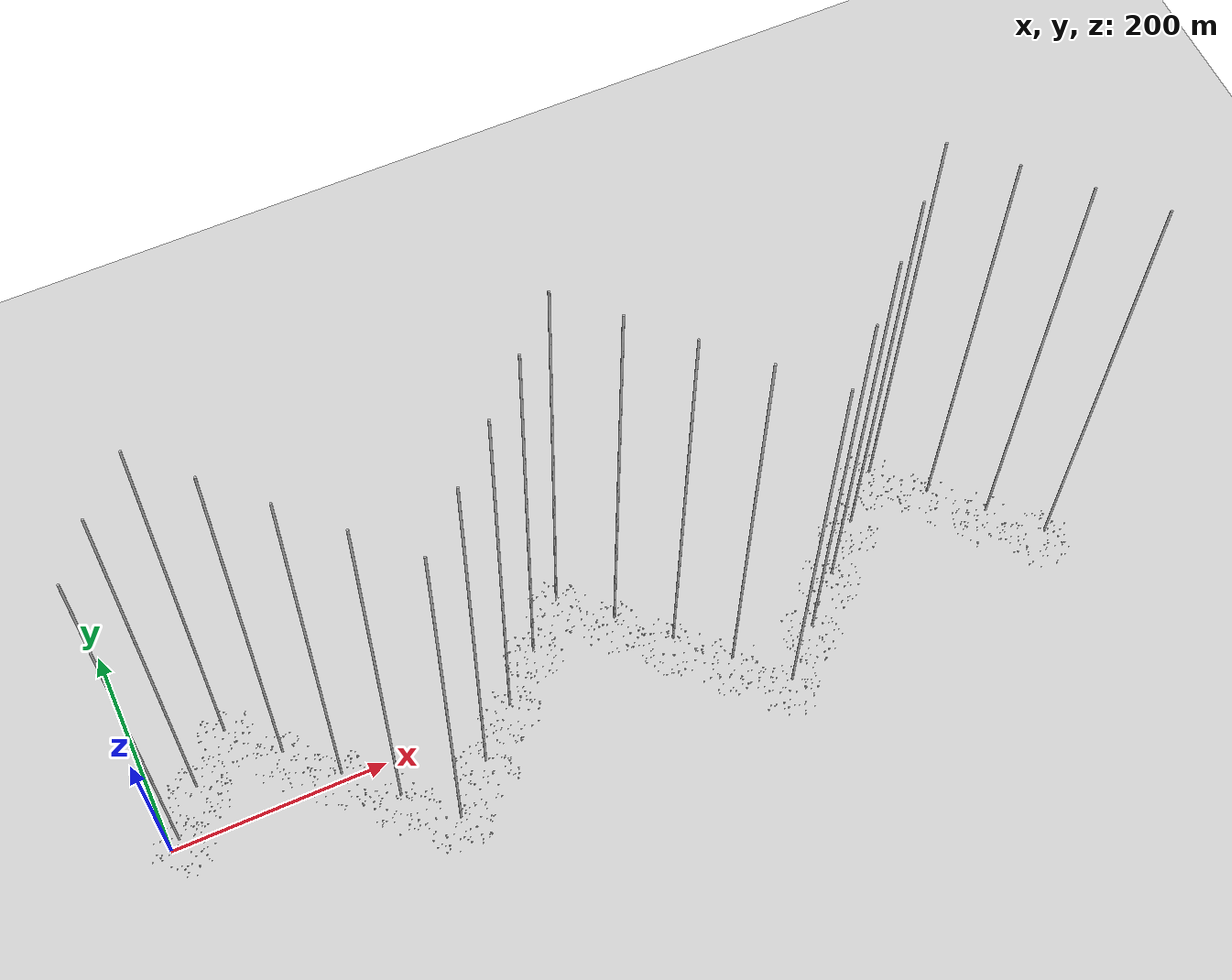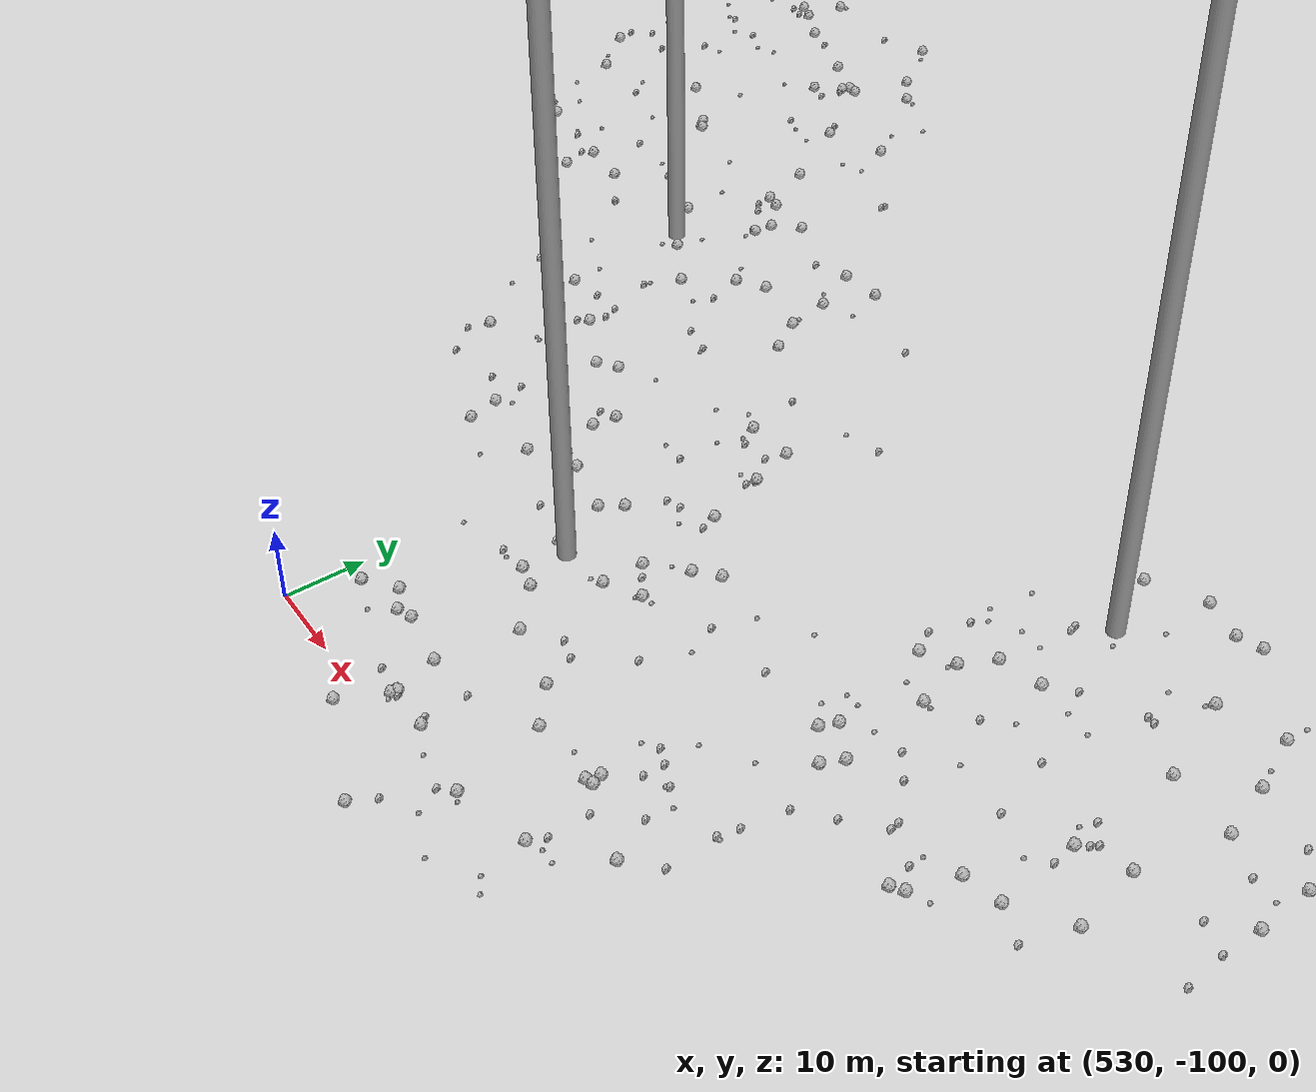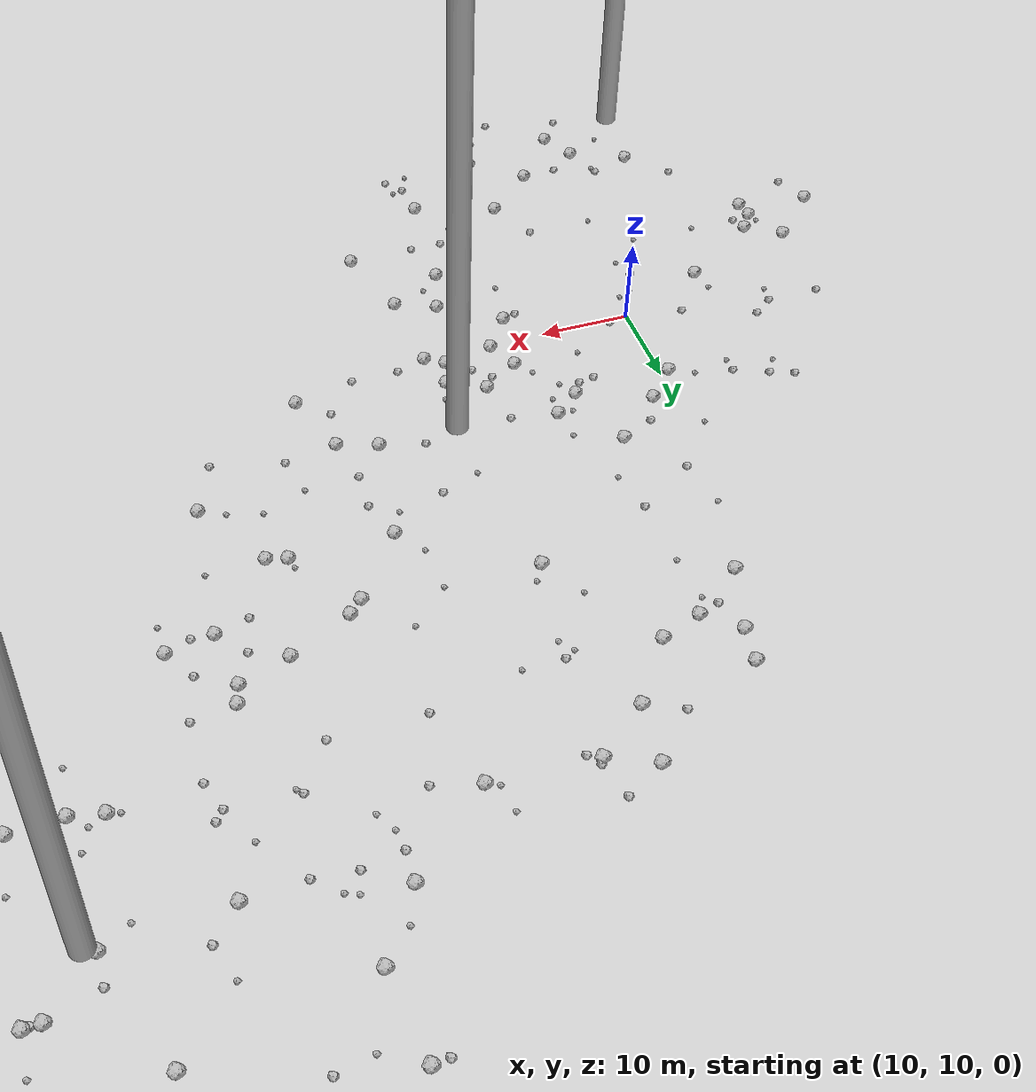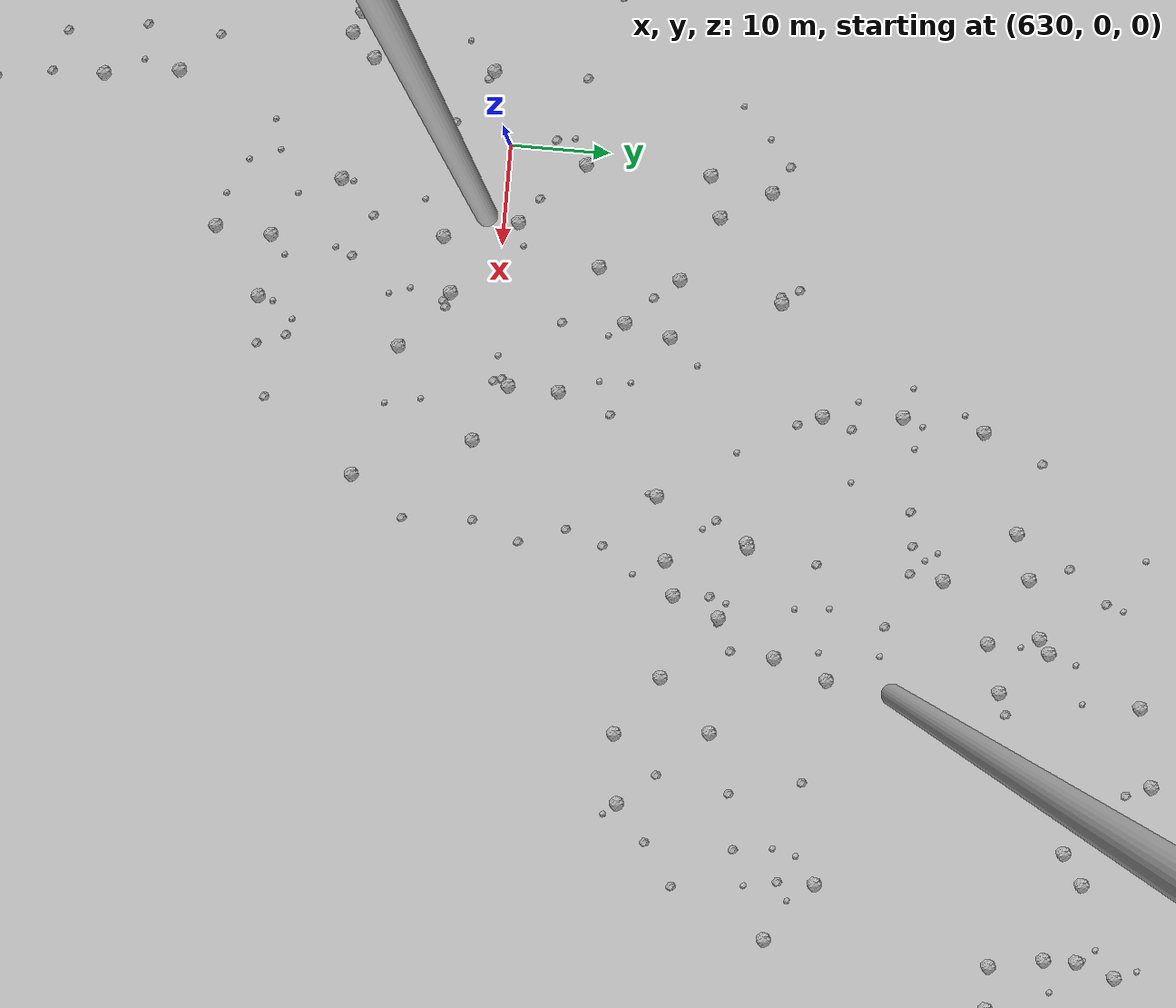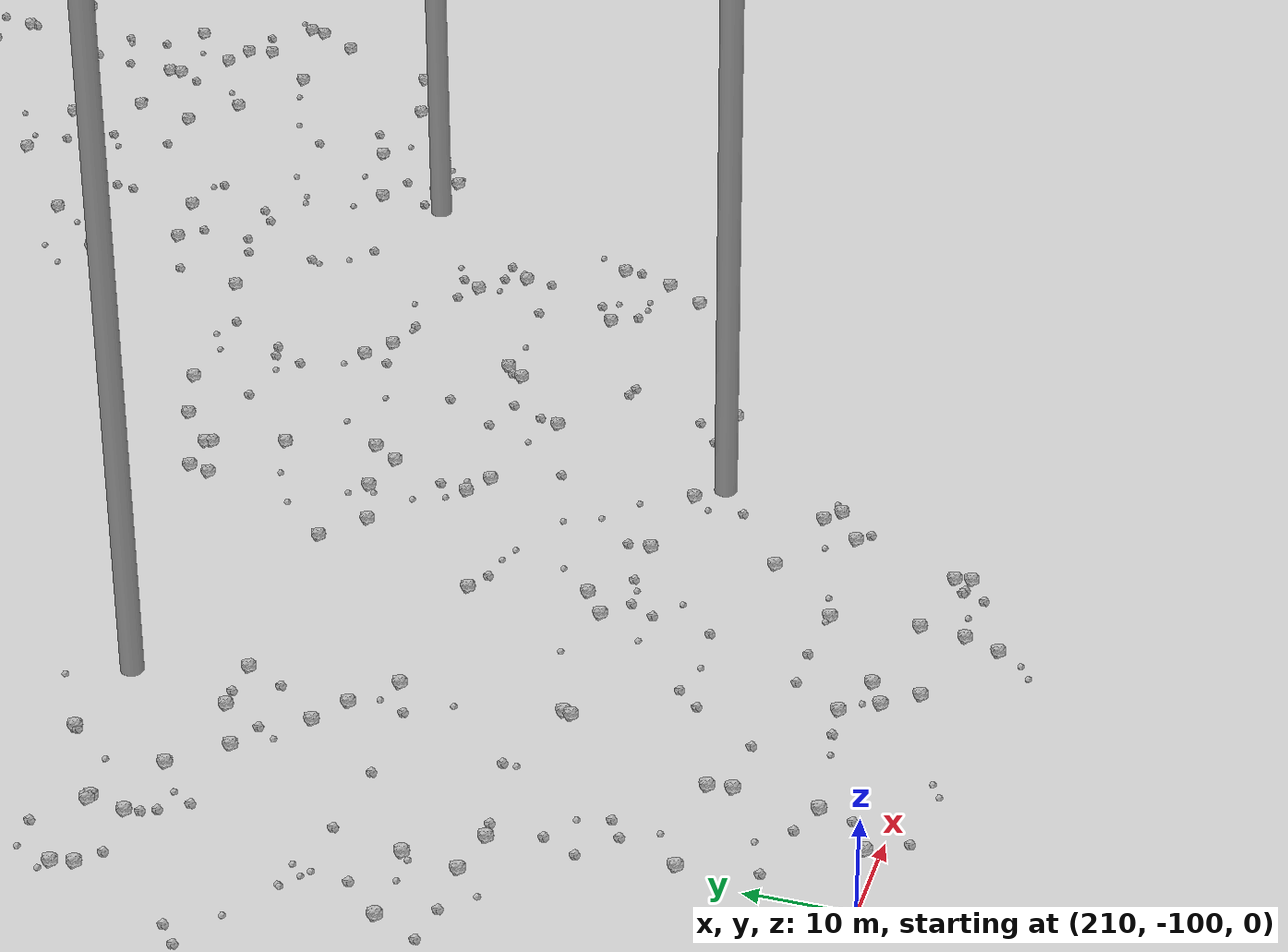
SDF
<sdf version="1.6">
 <world name="default">
  <include><uri>model://custom_ground</uri></include>
  <include><uri>model://sun</uri></include>
  <spherical_coordinates>
   <surface_model>EARTH_WGS84</surface_model>
   <latitude_deg>38.161479</latitude_deg>
   <longitude_deg>-122.454630</longitude_deg>
   <elevation>488.0</elevation>
   <heading_deg>90</heading_deg>
  </spherical_coordinates>
  <model name="rock1_0_0">
   <include><uri>model://rock1</uri><pose>23.96256814576043 -10.586147073642778 0.5 0 0 0</pose></include>
  </model>
  <model name="rock1_0_1">
   <include><uri>model://rock1</uri><pose>-0.1580409418926365 5.679114083501233 0.5 0 0 0</pose></include>
  </model>
  <model name="rock1_0_2">
   <include><uri>model://rock1</uri><pose>28.41739158182829 -3.074814084284803 0.5 0 0 0</pose></include>
  </model>
  <model name="rock1_0_3">
   <include><uri>model://rock1</uri><pose>17.941708850916385 -12.741150874366923 0.5 0 0 0</pose></include>
  </model>
  <model name="rock1_0_4">
   <include><uri>model://rock1</uri><pose>32.87942995188476 14.484928127473097 0.5 0 0 0</pose></include>
  </model>
  <model name="rock1_0_5">
   <include><uri>model://rock1</uri><pose>5.297471644125228 -20.443782554394325 0.5 0 0 0</pose></include>
  </model>
  <model name="rock1_0_6">
   <include><uri>model://rock1</uri><pose>33.98502137144183 10.156894638287625 0.5 0 0 0</pose></include>
  </model>
  <model name="rock1_0_7">
   <include><uri>model://rock1</uri><pose>-18.61232958123685 -3.422036454938084 0.5 0 0 0</pose></include>
  </model>
  <model name="rock1_0_8">
   <include><uri>model://rock1</uri><pose>-10.424005905759916 -4.464434464372967 0.5 0 0 0</pose></include>
  </model>
  <model name="rock1_0_9">
   <include><uri>model://rock1</uri><pose>18.0621693828733 -22.166217941436116 0.5 0 0 0</pose></include>
  </model>
  <model name="rock1_0_10">
   <include><uri>model://rock1</uri><pose>34.43435731147181 0.40605139688128133 0.5 0 0 0</pose></include>
  </model>
  <model name="rock1_0_11">
   <include><uri>model://rock1</uri><pose>-10.698162312541825 -2.3847659155270655 0.5 0 0 0</pose></include>
  </model>
  <model name="rock1_0_12">
   <include><uri>model://rock1</uri><pose>12.40423361291868 23.394985836606764 0.5 0 0 0</pose></include>
  </model>
  <model name="rock1_0_13">
   <include><uri>model://rock1</uri><pose>-13.059409607692023 2.1029047907385916 0.5 0 0 0</pose></include>
  </model>
  <model name="rock1_0_14">
   <include><uri>model://rock1</uri><pose>9.178014654658845 19.939708198522908 0.5 0 0 0</pose></include>
  </model>
  <model name="rock1_0_15">
   <include><uri>model://rock1</uri><pose>26.415786492979663 10.464565087323173 0.5 0 0 0</pose></include>
  </model>
  <model name="rock1_0_16">
   <include><uri>model://rock1</uri><pose>30.02413011107513 2.2766012231866384 0.5 0 0 0</pose></include>
  </model>
  <model name="rock1_0_17">
   <include><uri>model://rock1</uri><pose>37.08525120557077 -8.429192265944383 0.5 0 0 0</pose></include>
  </model>
  <model name="rock1_0_18">
   <include><uri>model://rock1</uri><pose>27.09199994535812 -15.657473308679657 0.5 0 0 0</pose></include>
  </model>
  <model name="rock1_0_19">
   <include><uri>model://rock1</uri><pose>-0.8922242826436957 -17.66719383208281 0.5 0 0 0</pose></include>
  </model>
  <model name="rock1_0_20">
   <include><uri>model://rock1</uri><pose>7.299470260438689 -24.273388104321164 0.5 0 0 0</pose></include>
  </model>
  <model name="rock1_0_21">
   <include><uri>model://rock1</uri><pose>22.945594447407736 22.639345842651814 0.5 0 0 0</pose></include>
  </model>
  <model name="rock1_0_22">
   <include><uri>model://rock1</uri><pose>31.944654300674436 11.467203417531962 0.5 0 0 0</pose></include>
  </model>
  <model name="rock1_0_23">
   <include><uri>model://rock1</uri><pose>12.36814415746121 -17.806907995512976 0.5 0 0 0</pose></include>
  </model>
  <model name="rock1_0_24">
   <include><uri>model://rock1</uri><pose>-9.18715183311863 -0.29991783965035523 0.5 0 0 0</pose></include>
  </model>
  <model name="rock1_0_25">
   <include><uri>model://rock1</uri><pose>23.529986395838343 6.515106325926851 0.5 0 0 0</pose></include>
  </model>
  <model name="rock1_0_26">
   <include><uri>model://rock1</uri><pose>24.815076601063687 13.910479630349023 0.5 0 0 0</pose></include>
  </model>
  <model name="rock2_0_0">
   <include><uri>model://rock2</uri><pose>3.578129130869094 -16.16692837668848 0.3 0 0 0</pose></include>
  </model>
  <model name="rock2_0_1">
   <include><uri>model://rock2</uri><pose>27.428267597585908 -19.759513121159923 0.3 0 0 0</pose></include>
  </model>
  <model name="rock2_0_2">
   <include><uri>model://rock2</uri><pose>29.48508474239822 13.352315158277285 0.3 0 0 0</pose></include>
  </model>
  <model name="rock2_0_3">
   <include><uri>model://rock2</uri><pose>-4.1746304810611505 14.165744127129244 0.3 0 0 0</pose></include>
  </model>
  <model name="rock2_0_4">
   <include><uri>model://rock2</uri><pose>17.295356006212558 18.435426283717 0.3 0 0 0</pose></include>
  </model>
  <model name="rock2_0_5">
   <include><uri>model://rock2</uri><pose>12.289626321882182 10.640985729403674 0.3 0 0 0</pose></include>
  </model>
  <model name="rock2_0_6">
   <include><uri>model://rock2</uri><pose>-1.2643293683313814 23.536320333111753 0.3 0 0 0</pose></include>
  </model>
  <model name="rock2_0_7">
   <include><uri>model://rock2</uri><pose>-5.078221449205184 -13.347228170310135 0.3 0 0 0</pose></include>
  </model>
  <model name="rock2_0_8">
   <include><uri>model://rock2</uri><pose>3.763340004281538 11.200142381877818 0.3 0 0 0</pose></include>
  </model>
  <model name="rock2_0_9">
   <include><uri>model://rock2</uri><pose>-8.593817911637815 -2.05421884149213 0.3 0 0 0</pose></include>
  </model>
  <model name="rock2_0_10">
   <include><uri>model://rock2</uri><pose>13.921627170675514 26.487560802090762 0.3 0 0 0</pose></include>
  </model>
  <model name="rock2_0_11">
   <include><uri>model://rock2</uri><pose>4.910181380320477 -27.513099349576567 0.3 0 0 0</pose></include>
  </model>
  <model name="rock2_0_12">
   <include><uri>model://rock2</uri><pose>-6.389204506813105 12.530137358847838 0.3 0 0 0</pose></include>
  </model>
  <model name="rock2_0_13">
   <include><uri>model://rock2</uri><pose>18.01014584404139 -23.428136131902576 0.3 0 0 0</pose></include>
  </model>
  <model name="rock2_0_14">
   <include><uri>model://rock2</uri><pose>13.415344528807758 -29.38692071259573 0.3 0 0 0</pose></include>
  </model>
  <model name="rock2_0_15">
   <include><uri>model://rock2</uri><pose>-17.083385159956002 -7.286180661696445 0.3 0 0 0</pose></include>
  </model>
  <model name="rock2_0_16">
   <include><uri>model://rock2</uri><pose>-3.8234732857485554 24.4843805416859 0.3 0 0 0</pose></include>
  </model>
  <model name="rock2_0_17">
   <include><uri>model://rock2</uri><pose>6.913424224778041 3.4733461319559353 0.3 0 0 0</pose></include>
  </model>
  <model name="rock2_0_18">
   <include><uri>model://rock2</uri><pose>15.320388897650517 -7.3203294347291035 0.3 0 0 0</pose></include>
  </model>
  <model name="rock2_0_19">
   <include><uri>model://rock2</uri><pose>8.322710209520412 -18.05026056274828 0.3 0 0 0</pose></include>
  </model>
  <model name="rock2_0_20">
   <include><uri>model://rock2</uri><pose>37.25245316368835 11.12103622756463 0.3 0 0 0</pose></include>
  </model>
  <model name="rock2_0_21">
   <include><uri>model://rock2</uri><pose>26.131500497765792 -8.496168912250937 0.3 0 0 0</pose></include>
  </model>
  <model name="rock2_0_22">
   <include><uri>model://rock2</uri><pose>29.711875925371494 -8.533448604929504 0.3 0 0 0</pose></include>
  </model>
  <model name="rock2_0_23">
   <include><uri>model://rock2</uri><pose>2.3940881802948297 22.00194077299433 0.3 0 0 0</pose></include>
  </model>
  <model name="rock2_0_24">
   <include><uri>model://rock2</uri><pose>28.993065558352363 -21.703560069414035 0.3 0 0 0</pose></include>
  </model>
  <model name="rock2_0_25">
   <include><uri>model://rock2</uri><pose>21.95720262483981 6.004307388810972 0.3 0 0 0</pose></include>
  </model>
  <model name="rock2_0_26">
   <include><uri>model://rock2</uri><pose>-12.316274381224401 12.570213672096536 0.3 0 0 0</pose></include>
  </model>
  <model name="rock3_0_0">
   <include><uri>model://rock3</uri><pose>2.3327825160831033 20.226452054251695 0.2 0 0 0</pose></include>
  </model>
  <model name="rock3_0_1">
   <include><uri>model://rock3</uri><pose>7.872306202601582 -7.392357705741624 0.2 0 0 0</pose></include>
  </model>
  <model name="rock3_0_2">
   <include><uri>model://rock3</uri><pose>26.331481828916978 -22.23897731761933 0.2 0 0 0</pose></include>
  </model>
  <model name="rock3_0_3">
   <include><uri>model://rock3</uri><pose>23.244884643001754 15.580587756518483 0.2 0 0 0</pose></include>
  </model>
  <model name="rock3_0_4">
   <include><uri>model://rock3</uri><pose>-6.797412899877411 10.527264413228892 0.2 0 0 0</pose></include>
  </model>
  <model name="rock3_0_5">
   <include><uri>model://rock3</uri><pose>16.266468183047003 -26.351691855839945 0.2 0 0 0</pose></include>
  </model>
  <model name="rock3_0_6">
   <include><uri>model://rock3</uri><pose>3.712939133427451 -17.0886505815148 0.2 0 0 0</pose></include>
  </model>
  <model name="rock3_0_7">
   <include><uri>model://rock3</uri><pose>28.585731086721168 -19.599166140235702 0.2 0 0 0</pose></include>
  </model>
  <model name="rock3_0_8">
   <include><uri>model://rock3</uri><pose>8.07194706538263 6.1094760336943 0.2 0 0 0</pose></include>
  </model>
  <model name="rock3_0_9">
   <include><uri>model://rock3</uri><pose>-3.361673642422417 -2.306266194044685 0.2 0 0 0</pose></include>
  </model>
  <model name="rock3_0_10">
   <include><uri>model://rock3</uri><pose>-2.559120370933176 21.65289137292794 0.2 0 0 0</pose></include>
  </model>
  <model name="rock3_0_11">
   <include><uri>model://rock3</uri><pose>-11.33041715676664 -1.3485207414880485 0.2 0 0 0</pose></include>
  </model>
  <model name="rock3_0_12">
   <include><uri>model://rock3</uri><pose>22.635574081701613 20.214125293516837 0.2 0 0 0</pose></include>
  </model>
  <model name="rock3_0_13">
   <include><uri>model://rock3</uri><pose>33.566455664385224 16.735595944420638 0.2 0 0 0</pose></include>
  </model>
  <model name="rock3_0_14">
   <include><uri>model://rock3</uri><pose>-0.8568134449308182 8.274250702899195 0.2 0 0 0</pose></include>
  </model>
  <model name="rock3_0_15">
   <include><uri>model://rock3</uri><pose>6.422583146140116 21.05812626651955 0.2 0 0 0</pose></include>
  </model>
  <model name="rock3_0_16">
   <include><uri>model://rock3</uri><pose>22.487081777209042 0.9821268591622072 0.2 0 0 0</pose></include>
  </model>
  <model name="rock3_0_17">
   <include><uri>model://rock3</uri><pose>28.887421052000704 6.3467495844029145 0.2 0 0 0</pose></include>
  </model>
  <model name="rock3_0_18">
   <include><uri>model://rock3</uri><pose>21.125516925820328 18.258045226764317 0.2 0 0 0</pose></include>
  </model>
  <model name="rock3_0_19">
   <include><uri>model://rock3</uri><pose>7.653665821736663 0.9775097024757784 0.2 0 0 0</pose></include>
  </model>
  <model name="rock3_0_20">
   <include><uri>model://rock3</uri><pose>23.694900181080214 6.0367299297127985 0.2 0 0 0</pose></include>
  </model>
  <model name="rock3_0_21">
   <include><uri>model://rock3</uri><pose>30.510559158756138 -1.0967281043121133 0.2 0 0 0</pose></include>
  </model>
  <model name="rock3_0_22">
   <include><uri>model://rock3</uri><pose>17.447179516312445 14.08155440685264 0.2 0 0 0</pose></include>
  </model>
  <model name="rock3_0_23">
   <include><uri>model://rock3</uri><pose>8.503003075485246 28.31605123348743 0.2 0 0 0</pose></include>
  </model>
  <model name="rock3_0_24">
   <include><uri>model://rock3</uri><pose>1.1335100298842562 -22.674485470653487 0.2 0 0 0</pose></include>
  </model>
  <model name="rock3_0_25">
   <include><uri>model://rock3</uri><pose>9.507224269118396 6.800504915795486 0.2 0 0 0</pose></include>
  </model>
  <model name="rock3_0_26">
   <include><uri>model://rock3</uri><pose>4.0917735216555045 -2.366810784168809 0.2 0 0 0</pose></include>
  </model>
  <model name="rock1_1_0">
   <include><uri>model://rock1</uri><pose>44.358617282315386 33.568084169738526 0.5 0 0 0</pose></include>
  </model>
  <model name="rock1_1_1">
   <include><uri>model://rock1</uri><pose>16.985082388952897 58.91268466001111 0.5 0 0 0</pose></include>
  </model>
  <model name="rock1_1_2">
   <include><uri>model://rock1</uri><pose>19.76732027281411 52.2889497395045 0.5 0 0 0</pose></include>
  </model>
  <model name="rock1_1_3">
   <include><uri>model://rock1</uri><pose>16.364777547711796 55.127794994163644 0.5 0 0 0</pose></include>
  </model>
  <model name="rock1_1_4">
   <include><uri>model://rock1</uri><pose>28.9554686649488 60.25739272768302 0.5 0 0 0</pose></include>
  </model>
  <model name="rock1_1_5">
   <include><uri>model://rock1</uri><pose>14.168167966809374 48.11432146158637 0.5 0 0 0</pose></include>
  </model>
  <model name="rock1_1_6">
   <include><uri>model://rock1</uri><pose>68.96861454392268 41.404340269110904 0.5 0 0 0</pose></include>
  </model>
  <model name="rock1_1_7">
   <include><uri>model://rock1</uri><pose>31.832239579376672 41.76980761291179 0.5 0 0 0</pose></include>
  </model>
  <model name="rock1_1_8">
   <include><uri>model://rock1</uri><pose>29.660222139078538 66.67021351953038 0.5 0 0 0</pose></include>
  </model>
  <model name="rock1_1_9">
   <include><uri>model://rock1</uri><pose>63.832559108926986 49.00277968514079 0.5 0 0 0</pose></include>
  </model>
  <model name="rock1_1_10">
   <include><uri>model://rock1</uri><pose>63.251250839039486 46.94782990470479 0.5 0 0 0</pose></include>
  </model>
  <model name="rock1_1_11">
   <include><uri>model://rock1</uri><pose>62.30629569568491 24.750814239290087 0.5 0 0 0</pose></include>
  </model>
  <model name="rock1_1_12">
   <include><uri>model://rock1</uri><pose>24.16050601248707 53.86204098265304 0.5 0 0 0</pose></include>
  </model>
  <model name="rock1_1_13">
   <include><uri>model://rock1</uri><pose>49.789984117372065 40.67559609898921 0.5 0 0 0</pose></include>
  </model>
  <model name="rock1_1_14">
   <include><uri>model://rock1</uri><pose>64.07033877265638 40.566836718099495 0.5 0 0 0</pose></include>
  </model>
  <model name="rock1_1_15">
   <include><uri>model://rock1</uri><pose>42.376171492720324 21.328317656729453 0.5 0 0 0</pose></include>
  </model>
  <model name="rock1_1_16">
   <include><uri>model://rock1</uri><pose>49.0897291049367 12.610446191994079 0.5 0 0 0</pose></include>
  </model>
  <model name="rock1_1_17">
   <include><uri>model://rock1</uri><pose>46.635168355039966 19.90701639915197 0.5 0 0 0</pose></include>
  </model>
  <model name="rock1_1_18">
   <include><uri>model://rock1</uri><pose>28.864800099237844 16.536783548079786 0.5 0 0 0</pose></include>
  </model>
  <model name="rock1_1_19">
   <include><uri>model://rock1</uri><pose>45.18876153632713 63.91117252701656 0.5 0 0 0</pose></include>
  </model>
  <model name="rock1_1_20">
   <include><uri>model://rock1</uri><pose>55.180879605897225 33.526660404045096 0.5 0 0 0</pose></include>
  </model>
  <model name="rock1_1_21">
   <include><uri>model://rock1</uri><pose>51.27699499300563 42.13059460256569 0.5 0 0 0</pose></include>
  </model>
  <model name="rock1_1_22">
   <include><uri>model://rock1</uri><pose>17.650177800391674 28.118629871668 0.5 0 0 0</pose></include>
  </model>
  <model name="rock1_1_23">
   <include><uri>model://rock1</uri><pose>57.923949002702116 45.22621709953069 0.5 0 0 0</pose></include>
  </model>
  <model name="rock1_1_24">
   <include><uri>model://rock1</uri><pose>57.30864632097217 32.95221528961086 0.5 0 0 0</pose></include>
  </model>
  <model name="rock1_1_25">
   <include><uri>model://rock1</uri><pose>34.413572151299064 64.55552018981317 0.5 0 0 0</pose></include>
  </model>
  <model name="rock1_1_26">
   <include><uri>model://rock1</uri><pose>20.118595802689455 20.30597803569852 0.5 0 0 0</pose></include>
  </model>
  <model name="rock2_1_0">
   <include><uri>model://rock2</uri><pose>47.52156118320252 55.262156637110216 0.3 0 0 0</pose></include>
  </model>
  <model name="rock2_1_1">
   <include><uri>model://rock2</uri><pose>57.16160732753067 55.20374106031268 0.3 0 0 0</pose></include>
  </model>
  <model name="rock2_1_2">
   <include><uri>model://rock2</uri><pose>42.437742408555536 11.098753743970457 0.3 0 0 0</pose></include>
  </model>
  <model name="rock2_1_3">
   <include><uri>model://rock2</uri><pose>45.76138446110459 29.2011062874625 0.3 0 0 0</pose></include>
  </model>
  <model name="rock2_1_4">
   <include><uri>model://rock2</uri><pose>60.49562517679202 39.571183250631705 0.3 0 0 0</pose></include>
  </model>
  <model name="rock2_1_5">
   <include><uri>model://rock2</uri><pose>33.601793404649165 53.25800144207743 0.3 0 0 0</pose></include>
  </model>
  <model name="rock2_1_6">
   <include><uri>model://rock2</uri><pose>33.699569767323126 68.92529067125747 0.3 0 0 0</pose></include>
  </model>
  <model name="rock2_1_7">
   <include><uri>model://rock2</uri><pose>68.33580467013078 49.627153730035495 0.3 0 0 0</pose></include>
  </model>
  <model name="rock2_1_8">
   <include><uri>model://rock2</uri><pose>25.165639810932557 61.982503459381306 0.3 0 0 0</pose></include>
  </model>
  <model name="rock2_1_9">
   <include><uri>model://rock2</uri><pose>35.672697714535396 63.835739519231176 0.3 0 0 0</pose></include>
  </model>
  <model name="rock2_1_10">
   <include><uri>model://rock2</uri><pose>66.94071864730489 44.7143662795248 0.3 0 0 0</pose></include>
  </model>
  <model name="rock2_1_11">
   <include><uri>model://rock2</uri><pose>37.59958077811906 22.49516556798128 0.3 0 0 0</pose></include>
  </model>
  <model name="rock2_1_12">
   <include><uri>model://rock2</uri><pose>38.011270803473394 29.71001567873413 0.3 0 0 0</pose></include>
  </model>
  <model name="rock2_1_13">
   <include><uri>model://rock2</uri><pose>59.84548278909793 18.9168543338774 0.3 0 0 0</pose></include>
  </model>
  <model name="rock2_1_14">
   <include><uri>model://rock2</uri><pose>34.7283226480267 65.12629619403006 0.3 0 0 0</pose></include>
  </model>
  <model name="rock2_1_15">
   <include><uri>model://rock2</uri><pose>12.993470660875058 33.89162275313008 0.3 0 0 0</pose></include>
  </model>
  <model name="rock2_1_16">
   <include><uri>model://rock2</uri><pose>61.55234315202633 43.531377568467896 0.3 0 0 0</pose></include>
  </model>
  <model name="rock2_1_17">
   <include><uri>model://rock2</uri><pose>27.911866059920985 21.672965086808155 0.3 0 0 0</pose></include>
  </model>
  <model name="rock2_1_18">
   <include><uri>model://rock2</uri><pose>49.86040597562355 62.60288288941609 0.3 0 0 0</pose></include>
  </model>
  <model name="rock2_1_19">
   <include><uri>model://rock2</uri><pose>66.33656863993171 40.3658248595268 0.3 0 0 0</pose></include>
  </model>
  <model name="rock2_1_20">
   <include><uri>model://rock2</uri><pose>45.55339270968324 24.973712878778905 0.3 0 0 0</pose></include>
  </model>
  <model name="rock2_1_21">
   <include><uri>model://rock2</uri><pose>19.261223224801867 37.763119376282816 0.3 0 0 0</pose></include>
  </model>
  <model name="rock2_1_22">
   <include><uri>model://rock2</uri><pose>17.386430073763506 51.481864177031305 0.3 0 0 0</pose></include>
  </model>
  <model name="rock2_1_23">
   <include><uri>model://rock2</uri><pose>45.9037757770967 15.277795870425003 0.3 0 0 0</pose></include>
  </model>
  <model name="rock2_1_24">
   <include><uri>model://rock2</uri><pose>19.05502049319245 18.73710260029013 0.3 0 0 0</pose></include>
  </model>
  <model name="rock2_1_25">
   <include><uri>model://rock2</uri><pose>52.26588189604832 20.76476497916269 0.3 0 0 0</pose></include>
  </model>
  <model name="rock2_1_26">
   <include><uri>model://rock2</uri><pose>27.74939640599921 15.047519367023138 0.3 0 0 0</pose></include>
  </model>
  <model name="rock3_1_0">
   <include><uri>model://rock3</uri><pose>45.74385162232449 45.23579375246949 0.2 0 0 0</pose></include>
  </model>
  <model name="rock3_1_1">
   <include><uri>model://rock3</uri><pose>68.992357553091 37.98076361271788 0.2 0 0 0</pose></include>
  </model>
  <model name="rock3_1_2">
   <include><uri>model://rock3</uri><pose>18.54514571096125 50.27801322361191 0.2 0 0 0</pose></include>
  </model>
  <model name="rock3_1_3">
   <include><uri>model://rock3</uri><pose>53.88390780288203 65.86074284608323 0.2 0 0 0</pose></include>
  </model>
  <model name="rock3_1_4">
   <include><uri>model://rock3</uri><pose>19.59859024488389 19.933905161592644 0.2 0 0 0</pose></include>
  </model>
  <model name="rock3_1_5">
   <include><uri>model://rock3</uri><pose>33.762262155408955 28.077419296715515 0.2 0 0 0</pose></include>
  </model>
  <model name="rock3_1_6">
   <include><uri>model://rock3</uri><pose>33.52708150410625 51.07292847116956 0.2 0 0 0</pose></include>
  </model>
  <model name="rock3_1_7">
   <include><uri>model://rock3</uri><pose>60.950677383587454 59.328127472336746 0.2 0 0 0</pose></include>
  </model>
  <model name="rock3_1_8">
   <include><uri>model://rock3</uri><pose>43.44516370304698 67.2885199644574 0.2 0 0 0</pose></include>
  </model>
  <model name="rock3_1_9">
   <include><uri>model://rock3</uri><pose>41.6909785883868 41.52139370677145 0.2 0 0 0</pose></include>
  </model>
  <model name="rock3_1_10">
   <include><uri>model://rock3</uri><pose>63.325505892982136 33.01744818817194 0.2 0 0 0</pose></include>
  </model>
  <model name="rock3_1_11">
   <include><uri>model://rock3</uri><pose>42.01386974748914 36.4579790142124 0.2 0 0 0</pose></include>
  </model>
  <model name="rock3_1_12">
   <include><uri>model://rock3</uri><pose>59.61467625267585 25.84734104054913 0.2 0 0 0</pose></include>
  </model>
  <model name="rock3_1_13">
   <include><uri>model://rock3</uri><pose>37.89426086542075 53.18001041502094 0.2 0 0 0</pose></include>
  </model>
  <model name="rock3_1_14">
   <include><uri>model://rock3</uri><pose>42.95513012796777 30.84366563544504 0.2 0 0 0</pose></include>
  </model>
  <model name="rock3_1_15">
   <include><uri>model://rock3</uri><pose>11.900029934887286 39.2356042252711 0.2 0 0 0</pose></include>
  </model>
  <model name="rock3_1_16">
   <include><uri>model://rock3</uri><pose>22.452962021154573 25.993104180115406 0.2 0 0 0</pose></include>
  </model>
  <model name="rock3_1_17">
   <include><uri>model://rock3</uri><pose>51.25773059519415 25.04197423095615 0.2 0 0 0</pose></include>
  </model>
  <model name="rock3_1_18">
   <include><uri>model://rock3</uri><pose>54.78511551577007 34.72430379164259 0.2 0 0 0</pose></include>
  </model>
  <model name="rock3_1_19">
   <include><uri>model://rock3</uri><pose>32.924965255521485 43.55393132986092 0.2 0 0 0</pose></include>
  </model>
  <model name="rock3_1_20">
   <include><uri>model://rock3</uri><pose>18.981473233450362 45.224962295245234 0.2 0 0 0</pose></include>
  </model>
  <model name="rock3_1_21">
   <include><uri>model://rock3</uri><pose>32.431544449620944 52.49162639780411 0.2 0 0 0</pose></include>
  </model>
  <model name="rock3_1_22">
   <include><uri>model://rock3</uri><pose>20.250429030098665 33.06831582618361 0.2 0 0 0</pose></include>
  </model>
  <model name="rock3_1_23">
   <include><uri>model://rock3</uri><pose>29.056646230638773 46.254053018518334 0.2 0 0 0</pose></include>
  </model>
  <model name="rock3_1_24">
   <include><uri>model://rock3</uri><pose>56.01135877390947 26.870497468483727 0.2 0 0 0</pose></include>
  </model>
  <model name="rock3_1_25">
   <include><uri>model://rock3</uri><pose>43.8690063982679 64.35857176713603 0.2 0 0 0</pose></include>
  </model>
  <model name="rock3_1_26">
   <include><uri>model://rock3</uri><pose>21.171326285071395 22.48869012394706 0.2 0 0 0</pose></include>
  </model>
  <model name="rock1_2_0">
   <include><uri>model://rock1</uri><pose>102.5379617277107 63.79347306534129 0.5 0 0 0</pose></include>
  </model>
  <model name="rock1_2_1">
   <include><uri>model://rock1</uri><pose>99.64152390039024 77.28485401975108 0.5 0 0 0</pose></include>
  </model>
  <model name="rock1_2_2">
   <include><uri>model://rock1</uri><pose>85.85733219400225 104.87434575573528 0.5 0 0 0</pose></include>
  </model>
  <model name="rock1_2_3">
   <include><uri>model://rock1</uri><pose>92.63971028758795 91.46928189722375 0.5 0 0 0</pose></include>
  </model>
  <model name="rock1_2_4">
   <include><uri>model://rock1</uri><pose>77.11276733856576 56.78282408420269 0.5 0 0 0</pose></include>
  </model>
  <model name="rock1_2_5">
   <include><uri>model://rock1</uri><pose>90.4455956615831 57.1782423904763 0.5 0 0 0</pose></include>
  </model>
  <model name="rock1_2_6">
   <include><uri>model://rock1</uri><pose>68.17771978505246 68.55000468702133 0.5 0 0 0</pose></include>
  </model>
  <model name="rock1_2_7">
   <include><uri>model://rock1</uri><pose>94.69608125318402 79.36897600588114 0.5 0 0 0</pose></include>
  </model>
  <model name="rock1_2_8">
   <include><uri>model://rock1</uri><pose>68.61117301745458 101.02831032660507 0.5 0 0 0</pose></include>
  </model>
  <model name="rock1_2_9">
   <include><uri>model://rock1</uri><pose>97.81637452834158 90.56254724666036 0.5 0 0 0</pose></include>
  </model>
  <model name="rock1_2_10">
   <include><uri>model://rock1</uri><pose>53.82392059468029 71.3301847202982 0.5 0 0 0</pose></include>
  </model>
  <model name="rock1_2_11">
   <include><uri>model://rock1</uri><pose>80.0935664059825 69.38685189901824 0.5 0 0 0</pose></include>
  </model>
  <model name="rock1_2_12">
   <include><uri>model://rock1</uri><pose>92.00027713850116 69.37094785804946 0.5 0 0 0</pose></include>
  </model>
  <model name="rock1_2_13">
   <include><uri>model://rock1</uri><pose>57.288043391389955 86.71762582917577 0.5 0 0 0</pose></include>
  </model>
  <model name="rock1_2_14">
   <include><uri>model://rock1</uri><pose>65.30461977642577 104.13484370505898 0.5 0 0 0</pose></include>
  </model>
  <model name="rock1_2_15">
   <include><uri>model://rock1</uri><pose>76.00552899553414 81.20848813248917 0.5 0 0 0</pose></include>
  </model>
  <model name="rock1_2_16">
   <include><uri>model://rock1</uri><pose>71.67702901849698 93.34570903527248 0.5 0 0 0</pose></include>
  </model>
  <model name="rock1_2_17">
   <include><uri>model://rock1</uri><pose>65.0634839778155 93.10596383302655 0.5 0 0 0</pose></include>
  </model>
  <model name="rock1_2_18">
   <include><uri>model://rock1</uri><pose>86.83391696096838 74.2000214321838 0.5 0 0 0</pose></include>
  </model>
  <model name="rock1_2_19">
   <include><uri>model://rock1</uri><pose>58.3555052470385 77.86227247330993 0.5 0 0 0</pose></include>
  </model>
  <model name="rock1_2_20">
   <include><uri>model://rock1</uri><pose>100.2364662140383 82.90740359583387 0.5 0 0 0</pose></include>
  </model>
  <model name="rock1_2_21">
   <include><uri>model://rock1</uri><pose>85.16712741638915 74.17065259780956 0.5 0 0 0</pose></include>
  </model>
  <model name="rock1_2_22">
   <include><uri>model://rock1</uri><pose>85.76306551832259 56.26438962802769 0.5 0 0 0</pose></include>
  </model>
  <model name="rock1_2_23">
   <include><uri>model://rock1</uri><pose>80.44238345650288 56.06511447248454 0.5 0 0 0</pose></include>
  </model>
  <model name="rock1_2_24">
   <include><uri>model://rock1</uri><pose>81.79720720554556 107.41495707626487 0.5 0 0 0</pose></include>
  </model>
  <model name="rock1_2_25">
   <include><uri>model://rock1</uri><pose>62.65110970605001 101.9371429279729 0.5 0 0 0</pose></include>
  </model>
  <model name="rock1_2_26">
   <include><uri>model://rock1</uri><pose>56.94171886300181 92.82658496530169 0.5 0 0 0</pose></include>
  </model>
  <model name="rock2_2_0">
   <include><uri>model://rock2</uri><pose>95.33212900192366 67.92328775430036 0.3 0 0 0</pose></include>
  </model>
  <model name="rock2_2_1">
   <include><uri>model://rock2</uri><pose>86.78550906416461 102.4991681557554 0.3 0 0 0</pose></include>
  </model>
  <model name="rock2_2_2">
   <include><uri>model://rock2</uri><pose>88.21873532200121 82.74995807080882 0.3 0 0 0</pose></include>
  </model>
  <model name="rock2_2_3">
   <include><uri>model://rock2</uri><pose>71.08833731979311 71.65402096553511 0.3 0 0 0</pose></include>
  </model>
  <model name="rock2_2_4">
   <include><uri>model://rock2</uri><pose>75.66778530465272 96.75098154638653 0.3 0 0 0</pose></include>
  </model>
  <model name="rock2_2_5">
   <include><uri>model://rock2</uri><pose>68.52355358520443 56.33138358135561 0.3 0 0 0</pose></include>
  </model>
  <model name="rock2_2_6">
   <include><uri>model://rock2</uri><pose>53.65973729422507 68.06628859936094 0.3 0 0 0</pose></include>
  </model>
  <model name="rock2_2_7">
   <include><uri>model://rock2</uri><pose>67.4708224241291 59.42981552005227 0.3 0 0 0</pose></include>
  </model>
  <model name="rock2_2_8">
   <include><uri>model://rock2</uri><pose>60.456172774992076 59.98277097391218 0.3 0 0 0</pose></include>
  </model>
  <model name="rock2_2_9">
   <include><uri>model://rock2</uri><pose>68.34321708229525 60.48364627285015 0.3 0 0 0</pose></include>
  </model>
  <model name="rock2_2_10">
   <include><uri>model://rock2</uri><pose>77.23047231568725 56.8782953981653 0.3 0 0 0</pose></include>
  </model>
  <model name="rock2_2_11">
   <include><uri>model://rock2</uri><pose>96.26613514309068 100.92583520844434 0.3 0 0 0</pose></include>
  </model>
  <model name="rock2_2_12">
   <include><uri>model://rock2</uri><pose>101.86040962333391 95.46053800356262 0.3 0 0 0</pose></include>
  </model>
  <model name="rock2_2_13">
   <include><uri>model://rock2</uri><pose>64.67474624410625 85.1876984025167 0.3 0 0 0</pose></include>
  </model>
  <model name="rock2_2_14">
   <include><uri>model://rock2</uri><pose>62.06208020275018 68.26921810235808 0.3 0 0 0</pose></include>
  </model>
  <model name="rock2_2_15">
   <include><uri>model://rock2</uri><pose>57.51351992188893 95.74365645007846 0.3 0 0 0</pose></include>
  </model>
  <model name="rock2_2_16">
   <include><uri>model://rock2</uri><pose>101.94950283706653 96.99193209818253 0.3 0 0 0</pose></include>
  </model>
  <model name="rock2_2_17">
   <include><uri>model://rock2</uri><pose>86.17935619269676 74.06391938571765 0.3 0 0 0</pose></include>
  </model>
  <model name="rock2_2_18">
   <include><uri>model://rock2</uri><pose>82.53842710726576 83.99669946562783 0.3 0 0 0</pose></include>
  </model>
  <model name="rock2_2_19">
   <include><uri>model://rock2</uri><pose>65.59760957090013 98.55182251659974 0.3 0 0 0</pose></include>
  </model>
  <model name="rock2_2_20">
   <include><uri>model://rock2</uri><pose>55.640857969801246 86.54879586605782 0.3 0 0 0</pose></include>
  </model>
  <model name="rock2_2_21">
   <include><uri>model://rock2</uri><pose>102.36707359603196 96.92515292019547 0.3 0 0 0</pose></include>
  </model>
  <model name="rock2_2_22">
   <include><uri>model://rock2</uri><pose>103.29268384812673 98.06083900061498 0.3 0 0 0</pose></include>
  </model>
  <model name="rock2_2_23">
   <include><uri>model://rock2</uri><pose>57.812689446464766 68.72253332160591 0.3 0 0 0</pose></include>
  </model>
  <model name="rock2_2_24">
   <include><uri>model://rock2</uri><pose>101.97600845200375 94.69896325397822 0.3 0 0 0</pose></include>
  </model>
  <model name="rock2_2_25">
   <include><uri>model://rock2</uri><pose>80.09437468788023 72.60546407938476 0.3 0 0 0</pose></include>
  </model>
  <model name="rock2_2_26">
   <include><uri>model://rock2</uri><pose>70.62895232446246 85.88808937297722 0.3 0 0 0</pose></include>
  </model>
  <model name="rock3_2_0">
   <include><uri>model://rock3</uri><pose>80.41383232777223 90.8869718972791 0.2 0 0 0</pose></include>
  </model>
  <model name="rock3_2_1">
   <include><uri>model://rock3</uri><pose>95.53261876255749 94.52890122376326 0.2 0 0 0</pose></include>
  </model>
  <model name="rock3_2_2">
   <include><uri>model://rock3</uri><pose>104.47182836318397 92.10853860421548 0.2 0 0 0</pose></include>
  </model>
  <model name="rock3_2_3">
   <include><uri>model://rock3</uri><pose>106.89514221289569 70.12654776017595 0.2 0 0 0</pose></include>
  </model>
  <model name="rock3_2_4">
   <include><uri>model://rock3</uri><pose>65.53443816526877 63.32044064756789 0.2 0 0 0</pose></include>
  </model>
  <model name="rock3_2_5">
   <include><uri>model://rock3</uri><pose>55.302901476436574 74.81864197822526 0.2 0 0 0</pose></include>
  </model>
  <model name="rock3_2_6">
   <include><uri>model://rock3</uri><pose>84.45475728413116 99.42046656849928 0.2 0 0 0</pose></include>
  </model>
  <model name="rock3_2_7">
   <include><uri>model://rock3</uri><pose>97.14199001802751 88.49109872032096 0.2 0 0 0</pose></include>
  </model>
  <model name="rock3_2_8">
   <include><uri>model://rock3</uri><pose>76.97140725984765 67.59785763687603 0.2 0 0 0</pose></include>
  </model>
  <model name="rock3_2_9">
   <include><uri>model://rock3</uri><pose>59.665553705076995 70.3354673784671 0.2 0 0 0</pose></include>
  </model>
  <model name="rock3_2_10">
   <include><uri>model://rock3</uri><pose>76.96980130723162 108.3223616580812 0.2 0 0 0</pose></include>
  </model>
  <model name="rock3_2_11">
   <include><uri>model://rock3</uri><pose>69.84692105866665 75.23177934531438 0.2 0 0 0</pose></include>
  </model>
  <model name="rock3_2_12">
   <include><uri>model://rock3</uri><pose>79.96261077169586 50.88584675695676 0.2 0 0 0</pose></include>
  </model>
  <model name="rock3_2_13">
   <include><uri>model://rock3</uri><pose>78.801723335391 57.537128740411994 0.2 0 0 0</pose></include>
  </model>
  <model name="rock3_2_14">
   <include><uri>model://rock3</uri><pose>75.88992005141748 56.97431539062844 0.2 0 0 0</pose></include>
  </model>
  <model name="rock3_2_15">
   <include><uri>model://rock3</uri><pose>60.973844321851615 84.44811546001651 0.2 0 0 0</pose></include>
  </model>
  <model name="rock3_2_16">
   <include><uri>model://rock3</uri><pose>88.525383761105 59.19997321655028 0.2 0 0 0</pose></include>
  </model>
  <model name="rock3_2_17">
   <include><uri>model://rock3</uri><pose>86.45204206030753 62.09058173203264 0.2 0 0 0</pose></include>
  </model>
  <model name="rock3_2_18">
   <include><uri>model://rock3</uri><pose>102.39152423103688 62.03061951854192 0.2 0 0 0</pose></include>
  </model>
  <model name="rock3_2_19">
   <include><uri>model://rock3</uri><pose>78.54595397241606 99.5455240283548 0.2 0 0 0</pose></include>
  </model>
  <model name="rock3_2_20">
   <include><uri>model://rock3</uri><pose>55.00428200985282 63.856973662680915 0.2 0 0 0</pose></include>
  </model>
  <model name="rock3_2_21">
   <include><uri>model://rock3</uri><pose>58.44476797029522 70.82881365330638 0.2 0 0 0</pose></include>
  </model>
  <model name="rock3_2_22">
   <include><uri>model://rock3</uri><pose>87.01515169546914 78.25594157943407 0.2 0 0 0</pose></include>
  </model>
  <model name="rock3_2_23">
   <include><uri>model://rock3</uri><pose>85.1633242569235 73.58929127919248 0.2 0 0 0</pose></include>
  </model>
  <model name="rock3_2_24">
   <include><uri>model://rock3</uri><pose>105.10396619654276 83.9610285626254 0.2 0 0 0</pose></include>
  </model>
  <model name="rock3_2_25">
   <include><uri>model://rock3</uri><pose>79.76878281013175 59.89421736039123 0.2 0 0 0</pose></include>
  </model>
  <model name="rock3_2_26">
   <include><uri>model://rock3</uri><pose>65.58462481328336 89.50914589177319 0.2 0 0 0</pose></include>
  </model>
  <model name="rock1_3_0">
   <include><uri>model://rock1</uri><pose>103.80544694655866 60.673117481293346 0.5 0 0 0</pose></include>
  </model>
  <model name="rock1_3_1">
   <include><uri>model://rock1</uri><pose>128.31507977644813 39.80466099811981 0.5 0 0 0</pose></include>
  </model>
  <model name="rock1_3_2">
   <include><uri>model://rock1</uri><pose>138.25978267567726 22.56037199793628 0.5 0 0 0</pose></include>
  </model>
  <model name="rock1_3_3">
   <include><uri>model://rock1</uri><pose>143.17137453636693 43.698724684117146 0.5 0 0 0</pose></include>
  </model>
  <model name="rock1_3_4">
   <include><uri>model://rock1</uri><pose>128.4033684228163 35.90998231137881 0.5 0 0 0</pose></include>
  </model>
  <model name="rock1_3_5">
   <include><uri>model://rock1</uri><pose>104.86234982940564 33.3108524134596 0.5 0 0 0</pose></include>
  </model>
  <model name="rock1_3_6">
   <include><uri>model://rock1</uri><pose>115.56968618155524 27.003399152649532 0.5 0 0 0</pose></include>
  </model>
  <model name="rock1_3_7">
   <include><uri>model://rock1</uri><pose>135.76367062855732 24.494706496864573 0.5 0 0 0</pose></include>
  </model>
  <model name="rock1_3_8">
   <include><uri>model://rock1</uri><pose>137.1144305628655 33.73690189862557 0.5 0 0 0</pose></include>
  </model>
  <model name="rock1_3_9">
   <include><uri>model://rock1</uri><pose>99.55312065521709 55.281349187716955 0.5 0 0 0</pose></include>
  </model>
  <model name="rock1_3_10">
   <include><uri>model://rock1</uri><pose>108.09714128838762 12.968813570560926 0.5 0 0 0</pose></include>
  </model>
  <model name="rock1_3_11">
   <include><uri>model://rock1</uri><pose>148.90601084430742 32.172285850503854 0.5 0 0 0</pose></include>
  </model>
  <model name="rock1_3_12">
   <include><uri>model://rock1</uri><pose>111.98662818565894 38.922439416876664 0.5 0 0 0</pose></include>
  </model>
  <model name="rock1_3_13">
   <include><uri>model://rock1</uri><pose>145.68059405376877 33.55134785729286 0.5 0 0 0</pose></include>
  </model>
  <model name="rock1_3_14">
   <include><uri>model://rock1</uri><pose>126.31146407268534 61.34892196092944 0.5 0 0 0</pose></include>
  </model>
  <model name="rock1_3_15">
   <include><uri>model://rock1</uri><pose>112.3226661905507 53.852451733146225 0.5 0 0 0</pose></include>
  </model>
  <model name="rock1_3_16">
   <include><uri>model://rock1</uri><pose>132.75770931511238 62.663799992820095 0.5 0 0 0</pose></include>
  </model>
  <model name="rock1_3_17">
   <include><uri>model://rock1</uri><pose>128.8573634389721 62.60133747252338 0.5 0 0 0</pose></include>
  </model>
  <model name="rock1_3_18">
   <include><uri>model://rock1</uri><pose>130.500083607457 21.924507889849444 0.5 0 0 0</pose></include>
  </model>
  <model name="rock1_3_19">
   <include><uri>model://rock1</uri><pose>130.9826648835209 50.74806708042283 0.5 0 0 0</pose></include>
  </model>
  <model name="rock1_3_20">
   <include><uri>model://rock1</uri><pose>148.58095446731417 32.75763230779801 0.5 0 0 0</pose></include>
  </model>
  <model name="rock1_3_21">
   <include><uri>model://rock1</uri><pose>116.84843652097518 22.174752445877996 0.5 0 0 0</pose></include>
  </model>
  <model name="rock1_3_22">
   <include><uri>model://rock1</uri><pose>113.91693559891476 56.4150086385516 0.5 0 0 0</pose></include>
  </model>
  <model name="rock1_3_23">
   <include><uri>model://rock1</uri><pose>136.70136242800854 21.509738462500408 0.5 0 0 0</pose></include>
  </model>
  <model name="rock1_3_24">
   <include><uri>model://rock1</uri><pose>132.5816364011663 51.2181701591616 0.5 0 0 0</pose></include>
  </model>
  <model name="rock1_3_25">
   <include><uri>model://rock1</uri><pose>124.87771996880873 37.37396251057365 0.5 0 0 0</pose></include>
  </model>
  <model name="rock1_3_26">
   <include><uri>model://rock1</uri><pose>114.85677018934817 49.79878104391176 0.5 0 0 0</pose></include>
  </model>
  <model name="rock2_3_0">
   <include><uri>model://rock2</uri><pose>127.85408691793887 31.281039007450392 0.3 0 0 0</pose></include>
  </model>
  <model name="rock2_3_1">
   <include><uri>model://rock2</uri><pose>116.06336309377473 17.748141355946114 0.3 0 0 0</pose></include>
  </model>
  <model name="rock2_3_2">
   <include><uri>model://rock2</uri><pose>116.52963562918663 16.553983099411848 0.3 0 0 0</pose></include>
  </model>
  <model name="rock2_3_3">
   <include><uri>model://rock2</uri><pose>135.14673976168865 16.93863513242293 0.3 0 0 0</pose></include>
  </model>
  <model name="rock2_3_4">
   <include><uri>model://rock2</uri><pose>91.56724071745958 37.37282358757331 0.3 0 0 0</pose></include>
  </model>
  <model name="rock2_3_5">
   <include><uri>model://rock2</uri><pose>105.20630922156562 63.05355351095224 0.3 0 0 0</pose></include>
  </model>
  <model name="rock2_3_6">
   <include><uri>model://rock2</uri><pose>104.30332447144575 29.774765854160737 0.3 0 0 0</pose></include>
  </model>
  <model name="rock2_3_7">
   <include><uri>model://rock2</uri><pose>100.19047619533121 60.62923166660401 0.3 0 0 0</pose></include>
  </model>
  <model name="rock2_3_8">
   <include><uri>model://rock2</uri><pose>144.01716934096717 29.94359953236192 0.3 0 0 0</pose></include>
  </model>
  <model name="rock2_3_9">
   <include><uri>model://rock2</uri><pose>125.16725743634464 11.858876079185325 0.3 0 0 0</pose></include>
  </model>
  <model name="rock2_3_10">
   <include><uri>model://rock2</uri><pose>132.46155276417383 40.29871427642122 0.3 0 0 0</pose></include>
  </model>
  <model name="rock2_3_11">
   <include><uri>model://rock2</uri><pose>115.41665163221833 31.925378251160495 0.3 0 0 0</pose></include>
  </model>
  <model name="rock2_3_12">
   <include><uri>model://rock2</uri><pose>137.72693310959997 53.52026609314854 0.3 0 0 0</pose></include>
  </model>
  <model name="rock2_3_13">
   <include><uri>model://rock2</uri><pose>124.0681029302356 61.291967243478645 0.3 0 0 0</pose></include>
  </model>
  <model name="rock2_3_14">
   <include><uri>model://rock2</uri><pose>118.84006161605193 26.95458592574322 0.3 0 0 0</pose></include>
  </model>
  <model name="rock2_3_15">
   <include><uri>model://rock2</uri><pose>121.97936806860756 53.488701239916054 0.3 0 0 0</pose></include>
  </model>
  <model name="rock2_3_16">
   <include><uri>model://rock2</uri><pose>136.31635788878881 19.781948350906987 0.3 0 0 0</pose></include>
  </model>
  <model name="rock2_3_17">
   <include><uri>model://rock2</uri><pose>136.18386631058792 52.3028409640812 0.3 0 0 0</pose></include>
  </model>
  <model name="rock2_3_18">
   <include><uri>model://rock2</uri><pose>94.80063076996979 27.699205414205462 0.3 0 0 0</pose></include>
  </model>
  <model name="rock2_3_19">
   <include><uri>model://rock2</uri><pose>131.1172617764317 49.39601877540363 0.3 0 0 0</pose></include>
  </model>
  <model name="rock2_3_20">
   <include><uri>model://rock2</uri><pose>110.51459754240032 35.10097627287648 0.3 0 0 0</pose></include>
  </model>
  <model name="rock2_3_21">
   <include><uri>model://rock2</uri><pose>112.41772934077531 67.24280094261294 0.3 0 0 0</pose></include>
  </model>
  <model name="rock2_3_22">
   <include><uri>model://rock2</uri><pose>96.48690179450841 56.64097059082535 0.3 0 0 0</pose></include>
  </model>
  <model name="rock2_3_23">
   <include><uri>model://rock2</uri><pose>137.7144221179004 57.0942589922075 0.3 0 0 0</pose></include>
  </model>
  <model name="rock2_3_24">
   <include><uri>model://rock2</uri><pose>119.07250377697677 64.36492966985719 0.3 0 0 0</pose></include>
  </model>
  <model name="rock2_3_25">
   <include><uri>model://rock2</uri><pose>113.24612807935549 56.386351691186576 0.3 0 0 0</pose></include>
  </model>
  <model name="rock2_3_26">
   <include><uri>model://rock2</uri><pose>107.01913506176953 57.55641183490097 0.3 0 0 0</pose></include>
  </model>
  <model name="rock3_3_0">
   <include><uri>model://rock3</uri><pose>115.15014354099762 41.81222786394907 0.2 0 0 0</pose></include>
  </model>
  <model name="rock3_3_1">
   <include><uri>model://rock3</uri><pose>124.18883891380756 24.56675827667408 0.2 0 0 0</pose></include>
  </model>
  <model name="rock3_3_2">
   <include><uri>model://rock3</uri><pose>127.361944304108 21.656384430480266 0.2 0 0 0</pose></include>
  </model>
  <model name="rock3_3_3">
   <include><uri>model://rock3</uri><pose>127.53128130063607 20.72149752919201 0.2 0 0 0</pose></include>
  </model>
  <model name="rock3_3_4">
   <include><uri>model://rock3</uri><pose>97.33271853878301 29.620059268436403 0.2 0 0 0</pose></include>
  </model>
  <model name="rock3_3_5">
   <include><uri>model://rock3</uri><pose>95.23822325337936 56.08060258851465 0.2 0 0 0</pose></include>
  </model>
  <model name="rock3_3_6">
   <include><uri>model://rock3</uri><pose>99.2648044197914 35.940890802540125 0.2 0 0 0</pose></include>
  </model>
  <model name="rock3_3_7">
   <include><uri>model://rock3</uri><pose>147.39839481843725 47.03115855342155 0.2 0 0 0</pose></include>
  </model>
  <model name="rock3_3_8">
   <include><uri>model://rock3</uri><pose>133.24391342151955 37.015650438907535 0.2 0 0 0</pose></include>
  </model>
  <model name="rock3_3_9">
   <include><uri>model://rock3</uri><pose>101.64378741780607 52.942708372320794 0.2 0 0 0</pose></include>
  </model>
  <model name="rock3_3_10">
   <include><uri>model://rock3</uri><pose>102.22635839347996 52.330006192023916 0.2 0 0 0</pose></include>
  </model>
  <model name="rock3_3_11">
   <include><uri>model://rock3</uri><pose>119.87798512614849 16.96375163346865 0.2 0 0 0</pose></include>
  </model>
  <model name="rock3_3_12">
   <include><uri>model://rock3</uri><pose>121.86825681238368 49.979143433347794 0.2 0 0 0</pose></include>
  </model>
  <model name="rock3_3_13">
   <include><uri>model://rock3</uri><pose>116.1877855819845 13.321089622204665 0.2 0 0 0</pose></include>
  </model>
  <model name="rock3_3_14">
   <include><uri>model://rock3</uri><pose>111.28280891623703 23.474609243452903 0.2 0 0 0</pose></include>
  </model>
  <model name="rock3_3_15">
   <include><uri>model://rock3</uri><pose>135.99849545358606 50.71310525742128 0.2 0 0 0</pose></include>
  </model>
  <model name="rock3_3_16">
   <include><uri>model://rock3</uri><pose>132.22782730641455 61.7897925535542 0.2 0 0 0</pose></include>
  </model>
  <model name="rock3_3_17">
   <include><uri>model://rock3</uri><pose>101.96404284455157 52.77735933736989 0.2 0 0 0</pose></include>
  </model>
  <model name="rock3_3_18">
   <include><uri>model://rock3</uri><pose>106.83633028540868 51.33682296296193 0.2 0 0 0</pose></include>
  </model>
  <model name="rock3_3_19">
   <include><uri>model://rock3</uri><pose>97.24856052537106 52.047988753280606 0.2 0 0 0</pose></include>
  </model>
  <model name="rock3_3_20">
   <include><uri>model://rock3</uri><pose>101.85338624535345 30.681461995505646 0.2 0 0 0</pose></include>
  </model>
  <model name="rock3_3_21">
   <include><uri>model://rock3</uri><pose>111.76719003668977 31.0368048693865 0.2 0 0 0</pose></include>
  </model>
  <model name="rock3_3_22">
   <include><uri>model://rock3</uri><pose>113.1326558003472 47.489355615540404 0.2 0 0 0</pose></include>
  </model>
  <model name="rock3_3_23">
   <include><uri>model://rock3</uri><pose>96.97616133068125 33.84559546918426 0.2 0 0 0</pose></include>
  </model>
  <model name="rock3_3_24">
   <include><uri>model://rock3</uri><pose>120.72033983757427 17.35153280687146 0.2 0 0 0</pose></include>
  </model>
  <model name="rock3_3_25">
   <include><uri>model://rock3</uri><pose>128.2376937921515 62.71407036024661 0.2 0 0 0</pose></include>
  </model>
  <model name="rock3_3_26">
   <include><uri>model://rock3</uri><pose>104.71010261073877 15.916321408163698 0.2 0 0 0</pose></include>
  </model>
  <model name="rock1_4_0">
   <include><uri>model://rock1</uri><pose>179.44666945510778 16.131055492062394 0.5 0 0 0</pose></include>
  </model>
  <model name="rock1_4_1">
   <include><uri>model://rock1</uri><pose>155.73292206588187 10.237285929275266 0.5 0 0 0</pose></include>
  </model>
  <model name="rock1_4_2">
   <include><uri>model://rock1</uri><pose>187.35631866739038 -6.3766005244026545 0.5 0 0 0</pose></include>
  </model>
  <model name="rock1_4_3">
   <include><uri>model://rock1</uri><pose>168.2221612100495 17.657505675833534 0.5 0 0 0</pose></include>
  </model>
  <model name="rock1_4_4">
   <include><uri>model://rock1</uri><pose>131.58623766678627 -3.0640250281099455 0.5 0 0 0</pose></include>
  </model>
  <model name="rock1_4_5">
   <include><uri>model://rock1</uri><pose>167.9272271151934 10.724224889639544 0.5 0 0 0</pose></include>
  </model>
  <model name="rock1_4_6">
   <include><uri>model://rock1</uri><pose>172.32844823036368 20.5206901730986 0.5 0 0 0</pose></include>
  </model>
  <model name="rock1_4_7">
   <include><uri>model://rock1</uri><pose>188.51455489151195 -2.5911737525294107 0.5 0 0 0</pose></include>
  </model>
  <model name="rock1_4_8">
   <include><uri>model://rock1</uri><pose>150.55955260838095 -20.24242706892819 0.5 0 0 0</pose></include>
  </model>
  <model name="rock1_4_9">
   <include><uri>model://rock1</uri><pose>153.82484170504756 -22.57824123486199 0.5 0 0 0</pose></include>
  </model>
  <model name="rock1_4_10">
   <include><uri>model://rock1</uri><pose>138.06900322541813 14.27057342611652 0.5 0 0 0</pose></include>
  </model>
  <model name="rock1_4_11">
   <include><uri>model://rock1</uri><pose>176.46317981364692 24.094528363370067 0.5 0 0 0</pose></include>
  </model>
  <model name="rock1_4_12">
   <include><uri>model://rock1</uri><pose>135.2781669398353 6.686537395559789 0.5 0 0 0</pose></include>
  </model>
  <model name="rock1_4_13">
   <include><uri>model://rock1</uri><pose>171.9589835809677 13.923654710124026 0.5 0 0 0</pose></include>
  </model>
  <model name="rock1_4_14">
   <include><uri>model://rock1</uri><pose>148.192143277121 27.350497072024645 0.5 0 0 0</pose></include>
  </model>
  <model name="rock1_4_15">
   <include><uri>model://rock1</uri><pose>173.62032464021945 17.134849017871318 0.5 0 0 0</pose></include>
  </model>
  <model name="rock1_4_16">
   <include><uri>model://rock1</uri><pose>179.6444526530014 17.644999586254855 0.5 0 0 0</pose></include>
  </model>
  <model name="rock1_4_17">
   <include><uri>model://rock1</uri><pose>167.74971769735856 -26.56895333591468 0.5 0 0 0</pose></include>
  </model>
  <model name="rock1_4_18">
   <include><uri>model://rock1</uri><pose>174.43379167500063 -15.017033914952139 0.5 0 0 0</pose></include>
  </model>
  <model name="rock1_4_19">
   <include><uri>model://rock1</uri><pose>138.0793946247639 -14.543058799552897 0.5 0 0 0</pose></include>
  </model>
  <model name="rock1_4_20">
   <include><uri>model://rock1</uri><pose>161.1686926468372 -10.623680553943409 0.5 0 0 0</pose></include>
  </model>
  <model name="rock1_4_21">
   <include><uri>model://rock1</uri><pose>149.9589642787624 9.910209409105299 0.5 0 0 0</pose></include>
  </model>
  <model name="rock1_4_22">
   <include><uri>model://rock1</uri><pose>169.91944164164022 -8.18457638488222 0.5 0 0 0</pose></include>
  </model>
  <model name="rock1_4_23">
   <include><uri>model://rock1</uri><pose>168.06101930738075 -28.200312932258804 0.5 0 0 0</pose></include>
  </model>
  <model name="rock1_4_24">
   <include><uri>model://rock1</uri><pose>156.58410547938396 12.694272128735193 0.5 0 0 0</pose></include>
  </model>
  <model name="rock1_4_25">
   <include><uri>model://rock1</uri><pose>178.5450911028683 7.933769174072033 0.5 0 0 0</pose></include>
  </model>
  <model name="rock1_4_26">
   <include><uri>model://rock1</uri><pose>184.3903891660424 -6.359730233125312 0.5 0 0 0</pose></include>
  </model>
  <model name="rock2_4_0">
   <include><uri>model://rock2</uri><pose>173.69821473644623 -18.20116931346748 0.3 0 0 0</pose></include>
  </model>
  <model name="rock2_4_1">
   <include><uri>model://rock2</uri><pose>131.41294749295594 -8.689664596597051 0.3 0 0 0</pose></include>
  </model>
  <model name="rock2_4_2">
   <include><uri>model://rock2</uri><pose>161.21709732359542 -16.466683810095674 0.3 0 0 0</pose></include>
  </model>
  <model name="rock2_4_3">
   <include><uri>model://rock2</uri><pose>151.63666048232653 -25.268914454230266 0.3 0 0 0</pose></include>
  </model>
  <model name="rock2_4_4">
   <include><uri>model://rock2</uri><pose>146.81049669262015 -14.02943046746123 0.3 0 0 0</pose></include>
  </model>
  <model name="rock2_4_5">
   <include><uri>model://rock2</uri><pose>176.2626851728792 -24.353126231103094 0.3 0 0 0</pose></include>
  </model>
  <model name="rock2_4_6">
   <include><uri>model://rock2</uri><pose>175.45767391661627 1.7183210238773263 0.3 0 0 0</pose></include>
  </model>
  <model name="rock2_4_7">
   <include><uri>model://rock2</uri><pose>179.56927377428008 21.71005418837585 0.3 0 0 0</pose></include>
  </model>
  <model name="rock2_4_8">
   <include><uri>model://rock2</uri><pose>154.82084109204015 27.821307731968254 0.3 0 0 0</pose></include>
  </model>
  <model name="rock2_4_9">
   <include><uri>model://rock2</uri><pose>134.404590616874 -2.8823174414311517 0.3 0 0 0</pose></include>
  </model>
  <model name="rock2_4_10">
   <include><uri>model://rock2</uri><pose>134.94194426879787 10.049729691712464 0.3 0 0 0</pose></include>
  </model>
  <model name="rock2_4_11">
   <include><uri>model://rock2</uri><pose>184.4515596443531 2.840205632909125 0.3 0 0 0</pose></include>
  </model>
  <model name="rock2_4_12">
   <include><uri>model://rock2</uri><pose>159.82766764222526 21.541905668651026 0.3 0 0 0</pose></include>
  </model>
  <model name="rock2_4_13">
   <include><uri>model://rock2</uri><pose>151.44218521440482 28.409163968653864 0.3 0 0 0</pose></include>
  </model>
  <model name="rock2_4_14">
   <include><uri>model://rock2</uri><pose>172.96691425267497 -19.722809603274907 0.3 0 0 0</pose></include>
  </model>
  <model name="rock2_4_15">
   <include><uri>model://rock2</uri><pose>181.5943454303966 4.493982726069163 0.3 0 0 0</pose></include>
  </model>
  <model name="rock2_4_16">
   <include><uri>model://rock2</uri><pose>172.3547639742448 8.048024639215178 0.3 0 0 0</pose></include>
  </model>
  <model name="rock2_4_17">
   <include><uri>model://rock2</uri><pose>181.10992582110254 16.566071967722223 0.3 0 0 0</pose></include>
  </model>
  <model name="rock2_4_18">
   <include><uri>model://rock2</uri><pose>141.49719533584698 -23.02960719202614 0.3 0 0 0</pose></include>
  </model>
  <model name="rock2_4_19">
   <include><uri>model://rock2</uri><pose>162.36100720332115 -2.8144081574447597 0.3 0 0 0</pose></include>
  </model>
  <model name="rock2_4_20">
   <include><uri>model://rock2</uri><pose>140.87023750140582 20.006768064464822 0.3 0 0 0</pose></include>
  </model>
  <model name="rock2_4_21">
   <include><uri>model://rock2</uri><pose>137.5345090498908 2.561998550657222 0.3 0 0 0</pose></include>
  </model>
  <model name="rock2_4_22">
   <include><uri>model://rock2</uri><pose>155.76312991488282 15.008108423533272 0.3 0 0 0</pose></include>
  </model>
  <model name="rock2_4_23">
   <include><uri>model://rock2</uri><pose>181.7487415753184 -20.052649758306536 0.3 0 0 0</pose></include>
  </model>
  <model name="rock2_4_24">
   <include><uri>model://rock2</uri><pose>165.73996549707863 -18.385169260208677 0.3 0 0 0</pose></include>
  </model>
  <model name="rock2_4_25">
   <include><uri>model://rock2</uri><pose>144.82633941352336 18.399517377116638 0.3 0 0 0</pose></include>
  </model>
  <model name="rock2_4_26">
   <include><uri>model://rock2</uri><pose>158.05566146401227 24.44635505737388 0.3 0 0 0</pose></include>
  </model>
  <model name="rock3_4_0">
   <include><uri>model://rock3</uri><pose>171.94933704564386 -20.759925336040663 0.2 0 0 0</pose></include>
  </model>
  <model name="rock3_4_1">
   <include><uri>model://rock3</uri><pose>169.35954875422303 6.797099226779707 0.2 0 0 0</pose></include>
  </model>
  <model name="rock3_4_2">
   <include><uri>model://rock3</uri><pose>150.968199184366 1.6934172441639603 0.2 0 0 0</pose></include>
  </model>
  <model name="rock3_4_3">
   <include><uri>model://rock3</uri><pose>145.85302114937355 -23.03507014257766 0.2 0 0 0</pose></include>
  </model>
  <model name="rock3_4_4">
   <include><uri>model://rock3</uri><pose>178.1085069199183 -12.903629951930245 0.2 0 0 0</pose></include>
  </model>
  <model name="rock3_4_5">
   <include><uri>model://rock3</uri><pose>135.35252343951305 -0.2791525870532361 0.2 0 0 0</pose></include>
  </model>
  <model name="rock3_4_6">
   <include><uri>model://rock3</uri><pose>140.14804508621242 -7.233323410663004 0.2 0 0 0</pose></include>
  </model>
  <model name="rock3_4_7">
   <include><uri>model://rock3</uri><pose>166.56483959521492 22.209454779023638 0.2 0 0 0</pose></include>
  </model>
  <model name="rock3_4_8">
   <include><uri>model://rock3</uri><pose>153.92663469627377 16.218166677995583 0.2 0 0 0</pose></include>
  </model>
  <model name="rock3_4_9">
   <include><uri>model://rock3</uri><pose>150.0105553628442 26.959830218299025 0.2 0 0 0</pose></include>
  </model>
  <model name="rock3_4_10">
   <include><uri>model://rock3</uri><pose>139.6100087315269 11.129292775441762 0.2 0 0 0</pose></include>
  </model>
  <model name="rock3_4_11">
   <include><uri>model://rock3</uri><pose>186.93237351217746 -6.982940763778942 0.2 0 0 0</pose></include>
  </model>
  <model name="rock3_4_12">
   <include><uri>model://rock3</uri><pose>155.23570707891105 15.172165992993115 0.2 0 0 0</pose></include>
  </model>
  <model name="rock3_4_13">
   <include><uri>model://rock3</uri><pose>170.5639282513005 -27.601280015861754 0.2 0 0 0</pose></include>
  </model>
  <model name="rock3_4_14">
   <include><uri>model://rock3</uri><pose>154.85963208291088 -1.3111187978452428 0.2 0 0 0</pose></include>
  </model>
  <model name="rock3_4_15">
   <include><uri>model://rock3</uri><pose>148.42468937134316 8.061324476037896 0.2 0 0 0</pose></include>
  </model>
  <model name="rock3_4_16">
   <include><uri>model://rock3</uri><pose>147.25646226715574 -7.314189164718517 0.2 0 0 0</pose></include>
  </model>
  <model name="rock3_4_17">
   <include><uri>model://rock3</uri><pose>174.622631004413 -22.509300727995218 0.2 0 0 0</pose></include>
  </model>
  <model name="rock3_4_18">
   <include><uri>model://rock3</uri><pose>170.33065647323986 -24.879201637604723 0.2 0 0 0</pose></include>
  </model>
  <model name="rock3_4_19">
   <include><uri>model://rock3</uri><pose>144.8918264045149 -18.525349605136405 0.2 0 0 0</pose></include>
  </model>
  <model name="rock3_4_20">
   <include><uri>model://rock3</uri><pose>153.49119418337585 -12.238035313510835 0.2 0 0 0</pose></include>
  </model>
  <model name="rock3_4_21">
   <include><uri>model://rock3</uri><pose>171.2061588779443 -19.2793390789139 0.2 0 0 0</pose></include>
  </model>
  <model name="rock3_4_22">
   <include><uri>model://rock3</uri><pose>150.73369553905508 -5.86460868781699 0.2 0 0 0</pose></include>
  </model>
  <model name="rock3_4_23">
   <include><uri>model://rock3</uri><pose>147.6648287084981 -18.71558828244979 0.2 0 0 0</pose></include>
  </model>
  <model name="rock3_4_24">
   <include><uri>model://rock3</uri><pose>166.85000195498856 -21.495085113816113 0.2 0 0 0</pose></include>
  </model>
  <model name="rock3_4_25">
   <include><uri>model://rock3</uri><pose>161.06688839626912 15.919880802452752 0.2 0 0 0</pose></include>
  </model>
  <model name="rock3_4_26">
   <include><uri>model://rock3</uri><pose>130.3145985214556 0.44795501067896026 0.2 0 0 0</pose></include>
  </model>
  <model name="rock1_5_0">
   <include><uri>model://rock1</uri><pose>217.06608056162037 -41.070564617029625 0.5 0 0 0</pose></include>
  </model>
  <model name="rock1_5_1">
   <include><uri>model://rock1</uri><pose>209.7974519716649 -14.711026056784 0.5 0 0 0</pose></include>
  </model>
  <model name="rock1_5_2">
   <include><uri>model://rock1</uri><pose>228.60658338767368 -38.42277388549197 0.5 0 0 0</pose></include>
  </model>
  <model name="rock1_5_3">
   <include><uri>model://rock1</uri><pose>175.35423270653487 -35.43056645100946 0.5 0 0 0</pose></include>
  </model>
  <model name="rock1_5_4">
   <include><uri>model://rock1</uri><pose>181.47947051345227 -32.911798600586486 0.5 0 0 0</pose></include>
  </model>
  <model name="rock1_5_5">
   <include><uri>model://rock1</uri><pose>226.05564486467398 -48.92650392940972 0.5 0 0 0</pose></include>
  </model>
  <model name="rock1_5_6">
   <include><uri>model://rock1</uri><pose>222.62135128208783 -46.68029942784949 0.5 0 0 0</pose></include>
  </model>
  <model name="rock1_5_7">
   <include><uri>model://rock1</uri><pose>210.9097221002133 -66.8931939180029 0.5 0 0 0</pose></include>
  </model>
  <model name="rock1_5_8">
   <include><uri>model://rock1</uri><pose>205.56750717799986 -35.65218574219594 0.5 0 0 0</pose></include>
  </model>
  <model name="rock1_5_9">
   <include><uri>model://rock1</uri><pose>190.78964153206158 -25.60119215111031 0.5 0 0 0</pose></include>
  </model>
  <model name="rock1_5_10">
   <include><uri>model://rock1</uri><pose>181.08331145776512 -50.403218971962275 0.5 0 0 0</pose></include>
  </model>
  <model name="rock1_5_11">
   <include><uri>model://rock1</uri><pose>185.05983976012547 -40.3484695974218 0.5 0 0 0</pose></include>
  </model>
  <model name="rock1_5_12">
   <include><uri>model://rock1</uri><pose>197.6219393058599 -34.30176565100675 0.5 0 0 0</pose></include>
  </model>
  <model name="rock1_5_13">
   <include><uri>model://rock1</uri><pose>177.71192391244094 -50.69652986415423 0.5 0 0 0</pose></include>
  </model>
  <model name="rock1_5_14">
   <include><uri>model://rock1</uri><pose>186.95917565984377 -66.67857465730819 0.5 0 0 0</pose></include>
  </model>
  <model name="rock1_5_15">
   <include><uri>model://rock1</uri><pose>206.01827158805474 -65.98000556993227 0.5 0 0 0</pose></include>
  </model>
  <model name="rock1_5_16">
   <include><uri>model://rock1</uri><pose>206.87960257001373 -60.64436558308781 0.5 0 0 0</pose></include>
  </model>
  <model name="rock1_5_17">
   <include><uri>model://rock1</uri><pose>177.4172549016832 -29.000257765429133 0.5 0 0 0</pose></include>
  </model>
  <model name="rock1_5_18">
   <include><uri>model://rock1</uri><pose>222.5914815563219 -38.519024942371416 0.5 0 0 0</pose></include>
  </model>
  <model name="rock1_5_19">
   <include><uri>model://rock1</uri><pose>197.1675266709171 -32.26598217968979 0.5 0 0 0</pose></include>
  </model>
  <model name="rock1_5_20">
   <include><uri>model://rock1</uri><pose>177.99205093727355 -48.44510295716411 0.5 0 0 0</pose></include>
  </model>
  <model name="rock1_5_21">
   <include><uri>model://rock1</uri><pose>215.7605613171471 -26.808336522409505 0.5 0 0 0</pose></include>
  </model>
  <model name="rock1_5_22">
   <include><uri>model://rock1</uri><pose>206.5811760083765 -32.09593142797902 0.5 0 0 0</pose></include>
  </model>
  <model name="rock1_5_23">
   <include><uri>model://rock1</uri><pose>198.16139423935132 -61.27290112919589 0.5 0 0 0</pose></include>
  </model>
  <model name="rock1_5_24">
   <include><uri>model://rock1</uri><pose>184.79236237557114 -28.80852372484162 0.5 0 0 0</pose></include>
  </model>
  <model name="rock1_5_25">
   <include><uri>model://rock1</uri><pose>206.20208641596827 -31.913673748928474 0.5 0 0 0</pose></include>
  </model>
  <model name="rock1_5_26">
   <include><uri>model://rock1</uri><pose>212.9854416621214 -36.490063481576186 0.5 0 0 0</pose></include>
  </model>
  <model name="rock2_5_0">
   <include><uri>model://rock2</uri><pose>224.64616462713593 -38.26852734566802 0.3 0 0 0</pose></include>
  </model>
  <model name="rock2_5_1">
   <include><uri>model://rock2</uri><pose>187.01110582125528 -49.30311634239257 0.3 0 0 0</pose></include>
  </model>
  <model name="rock2_5_2">
   <include><uri>model://rock2</uri><pose>183.22595242690113 -20.717995090780548 0.3 0 0 0</pose></include>
  </model>
  <model name="rock2_5_3">
   <include><uri>model://rock2</uri><pose>173.00671059895055 -47.39665937457972 0.3 0 0 0</pose></include>
  </model>
  <model name="rock2_5_4">
   <include><uri>model://rock2</uri><pose>220.22421007685222 -42.48707186062032 0.3 0 0 0</pose></include>
  </model>
  <model name="rock2_5_5">
   <include><uri>model://rock2</uri><pose>176.19293110788539 -51.68095575386578 0.3 0 0 0</pose></include>
  </model>
  <model name="rock2_5_6">
   <include><uri>model://rock2</uri><pose>201.68067441168614 -57.621272473209544 0.3 0 0 0</pose></include>
  </model>
  <model name="rock2_5_7">
   <include><uri>model://rock2</uri><pose>206.40123327676088 -38.34838675218033 0.3 0 0 0</pose></include>
  </model>
  <model name="rock2_5_8">
   <include><uri>model://rock2</uri><pose>189.71744885529057 -46.37838438293265 0.3 0 0 0</pose></include>
  </model>
  <model name="rock2_5_9">
   <include><uri>model://rock2</uri><pose>186.91996979567736 -53.57142469412399 0.3 0 0 0</pose></include>
  </model>
  <model name="rock2_5_10">
   <include><uri>model://rock2</uri><pose>216.72730174025097 -54.38552143856457 0.3 0 0 0</pose></include>
  </model>
  <model name="rock2_5_11">
   <include><uri>model://rock2</uri><pose>197.20075792839347 -19.47064269968461 0.3 0 0 0</pose></include>
  </model>
  <model name="rock2_5_12">
   <include><uri>model://rock2</uri><pose>206.01562674898673 -14.821136185481897 0.3 0 0 0</pose></include>
  </model>
  <model name="rock2_5_13">
   <include><uri>model://rock2</uri><pose>212.73949214561867 -66.62261331956762 0.3 0 0 0</pose></include>
  </model>
  <model name="rock2_5_14">
   <include><uri>model://rock2</uri><pose>201.92551673519392 -28.284670051423 0.3 0 0 0</pose></include>
  </model>
  <model name="rock2_5_15">
   <include><uri>model://rock2</uri><pose>196.01803877739184 -65.52755122387055 0.3 0 0 0</pose></include>
  </model>
  <model name="rock2_5_16">
   <include><uri>model://rock2</uri><pose>175.65990541993963 -53.873590573010475 0.3 0 0 0</pose></include>
  </model>
  <model name="rock2_5_17">
   <include><uri>model://rock2</uri><pose>215.41537581061803 -27.104574331175975 0.3 0 0 0</pose></include>
  </model>
  <model name="rock2_5_18">
   <include><uri>model://rock2</uri><pose>199.58588362478838 -36.0990821711533 0.3 0 0 0</pose></include>
  </model>
  <model name="rock2_5_19">
   <include><uri>model://rock2</uri><pose>200.29344344522104 -66.0871698148331 0.3 0 0 0</pose></include>
  </model>
  <model name="rock2_5_20">
   <include><uri>model://rock2</uri><pose>180.3204576395377 -35.481543774174845 0.3 0 0 0</pose></include>
  </model>
  <model name="rock2_5_21">
   <include><uri>model://rock2</uri><pose>183.29893758185605 -25.63694261898629 0.3 0 0 0</pose></include>
  </model>
  <model name="rock2_5_22">
   <include><uri>model://rock2</uri><pose>191.893295096055 -44.67764285882031 0.3 0 0 0</pose></include>
  </model>
  <model name="rock2_5_23">
   <include><uri>model://rock2</uri><pose>208.01666480853345 -40.79601013575636 0.3 0 0 0</pose></include>
  </model>
  <model name="rock2_5_24">
   <include><uri>model://rock2</uri><pose>226.64319737018636 -42.2238210291926 0.3 0 0 0</pose></include>
  </model>
  <model name="rock2_5_25">
   <include><uri>model://rock2</uri><pose>208.35972510917324 -53.8389863741326 0.3 0 0 0</pose></include>
  </model>
  <model name="rock2_5_26">
   <include><uri>model://rock2</uri><pose>205.81194939769384 -36.975440520414125 0.3 0 0 0</pose></include>
  </model>
  <model name="rock3_5_0">
   <include><uri>model://rock3</uri><pose>183.0009125865013 -30.464438589896766 0.2 0 0 0</pose></include>
  </model>
  <model name="rock3_5_1">
   <include><uri>model://rock3</uri><pose>212.06418706057735 -31.201856423462345 0.2 0 0 0</pose></include>
  </model>
  <model name="rock3_5_2">
   <include><uri>model://rock3</uri><pose>209.33390362674243 -38.791239388818035 0.2 0 0 0</pose></include>
  </model>
  <model name="rock3_5_3">
   <include><uri>model://rock3</uri><pose>189.27168449335326 -18.221284353887427 0.2 0 0 0</pose></include>
  </model>
  <model name="rock3_5_4">
   <include><uri>model://rock3</uri><pose>192.51107993833898 -17.884142216795432 0.2 0 0 0</pose></include>
  </model>
  <model name="rock3_5_5">
   <include><uri>model://rock3</uri><pose>203.08360820795238 -61.46022182330403 0.2 0 0 0</pose></include>
  </model>
  <model name="rock3_5_6">
   <include><uri>model://rock3</uri><pose>206.02072022319868 -61.47165683805754 0.2 0 0 0</pose></include>
  </model>
  <model name="rock3_5_7">
   <include><uri>model://rock3</uri><pose>189.69878923505362 -23.117011351455517 0.2 0 0 0</pose></include>
  </model>
  <model name="rock3_5_8">
   <include><uri>model://rock3</uri><pose>201.3780510194643 -53.4314868593399 0.2 0 0 0</pose></include>
  </model>
  <model name="rock3_5_9">
   <include><uri>model://rock3</uri><pose>199.78042194658914 -51.946861591489146 0.2 0 0 0</pose></include>
  </model>
  <model name="rock3_5_10">
   <include><uri>model://rock3</uri><pose>202.9782938430862 -68.7268130515654 0.2 0 0 0</pose></include>
  </model>
  <model name="rock3_5_11">
   <include><uri>model://rock3</uri><pose>173.4511281896342 -27.472785462911396 0.2 0 0 0</pose></include>
  </model>
  <model name="rock3_5_12">
   <include><uri>model://rock3</uri><pose>222.97658824772654 -22.791222011869756 0.2 0 0 0</pose></include>
  </model>
  <model name="rock3_5_13">
   <include><uri>model://rock3</uri><pose>219.03801069389598 -44.38594974093325 0.2 0 0 0</pose></include>
  </model>
  <model name="rock3_5_14">
   <include><uri>model://rock3</uri><pose>198.398685366463 -28.66145584663382 0.2 0 0 0</pose></include>
  </model>
  <model name="rock3_5_15">
   <include><uri>model://rock3</uri><pose>194.52874979046643 -48.972103462721215 0.2 0 0 0</pose></include>
  </model>
  <model name="rock3_5_16">
   <include><uri>model://rock3</uri><pose>202.7316814570133 -52.232508298123875 0.2 0 0 0</pose></include>
  </model>
  <model name="rock3_5_17">
   <include><uri>model://rock3</uri><pose>187.06256415298938 -26.526492675502638 0.2 0 0 0</pose></include>
  </model>
  <model name="rock3_5_18">
   <include><uri>model://rock3</uri><pose>227.27446997892667 -51.51908146281406 0.2 0 0 0</pose></include>
  </model>
  <model name="rock3_5_19">
   <include><uri>model://rock3</uri><pose>196.09956944584854 -31.545848209492725 0.2 0 0 0</pose></include>
  </model>
  <model name="rock3_5_20">
   <include><uri>model://rock3</uri><pose>185.3101088056857 -58.0845556703557 0.2 0 0 0</pose></include>
  </model>
  <model name="rock3_5_21">
   <include><uri>model://rock3</uri><pose>182.07622494225254 -56.0325271227962 0.2 0 0 0</pose></include>
  </model>
  <model name="rock3_5_22">
   <include><uri>model://rock3</uri><pose>199.5682056573178 -52.2073950378614 0.2 0 0 0</pose></include>
  </model>
  <model name="rock3_5_23">
   <include><uri>model://rock3</uri><pose>202.2183552215685 -54.068740889853466 0.2 0 0 0</pose></include>
  </model>
  <model name="rock3_5_24">
   <include><uri>model://rock3</uri><pose>185.01379301459377 -48.019382263502976 0.2 0 0 0</pose></include>
  </model>
  <model name="rock3_5_25">
   <include><uri>model://rock3</uri><pose>175.71281778695925 -22.449207801444814 0.2 0 0 0</pose></include>
  </model>
  <model name="rock3_5_26">
   <include><uri>model://rock3</uri><pose>196.8651769938062 -32.095189187711824 0.2 0 0 0</pose></include>
  </model>
  <model name="rock1_6_0">
   <include><uri>model://rock1</uri><pose>251.52797374480954 -99.78260751033228 0.5 0 0 0</pose></include>
  </model>
  <model name="rock1_6_1">
   <include><uri>model://rock1</uri><pose>230.1632548189585 -67.86567760433839 0.5 0 0 0</pose></include>
  </model>
  <model name="rock1_6_2">
   <include><uri>model://rock1</uri><pose>248.72873528051272 -64.4610302570994 0.5 0 0 0</pose></include>
  </model>
  <model name="rock1_6_3">
   <include><uri>model://rock1</uri><pose>251.27979797179268 -87.05413537959826 0.5 0 0 0</pose></include>
  </model>
  <model name="rock1_6_4">
   <include><uri>model://rock1</uri><pose>223.28756817318305 -83.15568526911494 0.5 0 0 0</pose></include>
  </model>
  <model name="rock1_6_5">
   <include><uri>model://rock1</uri><pose>250.15839113063842 -103.19752250994914 0.5 0 0 0</pose></include>
  </model>
  <model name="rock1_6_6">
   <include><uri>model://rock1</uri><pose>257.5563311890093 -67.9652948115172 0.5 0 0 0</pose></include>
  </model>
  <model name="rock1_6_7">
   <include><uri>model://rock1</uri><pose>241.63967386498578 -97.95069792126347 0.5 0 0 0</pose></include>
  </model>
  <model name="rock1_6_8">
   <include><uri>model://rock1</uri><pose>260.45236330073385 -96.7362077498126 0.5 0 0 0</pose></include>
  </model>
  <model name="rock1_6_9">
   <include><uri>model://rock1</uri><pose>230.1089751686779 -52.41514278542012 0.5 0 0 0</pose></include>
  </model>
  <model name="rock1_6_10">
   <include><uri>model://rock1</uri><pose>246.34846950621042 -53.486263303019264 0.5 0 0 0</pose></include>
  </model>
  <model name="rock1_6_11">
   <include><uri>model://rock1</uri><pose>218.33084320099067 -98.56722549856144 0.5 0 0 0</pose></include>
  </model>
  <model name="rock1_6_12">
   <include><uri>model://rock1</uri><pose>239.26711107036974 -94.79957018423669 0.5 0 0 0</pose></include>
  </model>
  <model name="rock1_6_13">
   <include><uri>model://rock1</uri><pose>245.67626157183216 -66.5773572730948 0.5 0 0 0</pose></include>
  </model>
  <model name="rock1_6_14">
   <include><uri>model://rock1</uri><pose>268.374731014431 -83.84513573395571 0.5 0 0 0</pose></include>
  </model>
  <model name="rock1_6_15">
   <include><uri>model://rock1</uri><pose>264.21554254244506 -86.29368138550625 0.5 0 0 0</pose></include>
  </model>
  <model name="rock1_6_16">
   <include><uri>model://rock1</uri><pose>266.7924579298925 -82.47280448140617 0.5 0 0 0</pose></include>
  </model>
  <model name="rock1_6_17">
   <include><uri>model://rock1</uri><pose>237.2846945610173 -91.41682428198322 0.5 0 0 0</pose></include>
  </model>
  <model name="rock1_6_18">
   <include><uri>model://rock1</uri><pose>222.83162581618012 -93.37815629570721 0.5 0 0 0</pose></include>
  </model>
  <model name="rock1_6_19">
   <include><uri>model://rock1</uri><pose>211.65216619710887 -83.64359476803182 0.5 0 0 0</pose></include>
  </model>
  <model name="rock1_6_20">
   <include><uri>model://rock1</uri><pose>223.54726061211502 -85.41313148501143 0.5 0 0 0</pose></include>
  </model>
  <model name="rock1_6_21">
   <include><uri>model://rock1</uri><pose>252.05231045920516 -95.4017596536493 0.5 0 0 0</pose></include>
  </model>
  <model name="rock1_6_22">
   <include><uri>model://rock1</uri><pose>229.86956680829962 -68.64636784103436 0.5 0 0 0</pose></include>
  </model>
  <model name="rock1_6_23">
   <include><uri>model://rock1</uri><pose>258.0183145988289 -79.99170277245075 0.5 0 0 0</pose></include>
  </model>
  <model name="rock1_6_24">
   <include><uri>model://rock1</uri><pose>242.24551010817095 -93.30393864215068 0.5 0 0 0</pose></include>
  </model>
  <model name="rock1_6_25">
   <include><uri>model://rock1</uri><pose>260.7376833396139 -98.30024435480732 0.5 0 0 0</pose></include>
  </model>
  <model name="rock1_6_26">
   <include><uri>model://rock1</uri><pose>267.0414699244782 -69.54761262868821 0.5 0 0 0</pose></include>
  </model>
  <model name="rock2_6_0">
   <include><uri>model://rock2</uri><pose>245.44806345882216 -77.16759402144339 0.3 0 0 0</pose></include>
  </model>
  <model name="rock2_6_1">
   <include><uri>model://rock2</uri><pose>251.8977957604085 -67.99586343811995 0.3 0 0 0</pose></include>
  </model>
  <model name="rock2_6_2">
   <include><uri>model://rock2</uri><pose>236.1887421938128 -76.92536691253838 0.3 0 0 0</pose></include>
  </model>
  <model name="rock2_6_3">
   <include><uri>model://rock2</uri><pose>258.920479159127 -98.08391760376423 0.3 0 0 0</pose></include>
  </model>
  <model name="rock2_6_4">
   <include><uri>model://rock2</uri><pose>221.25138566609013 -65.00843986821256 0.3 0 0 0</pose></include>
  </model>
  <model name="rock2_6_5">
   <include><uri>model://rock2</uri><pose>248.6238090471169 -54.695773493412176 0.3 0 0 0</pose></include>
  </model>
  <model name="rock2_6_6">
   <include><uri>model://rock2</uri><pose>257.6755818503741 -100.16205154695601 0.3 0 0 0</pose></include>
  </model>
  <model name="rock2_6_7">
   <include><uri>model://rock2</uri><pose>225.90795628869586 -54.136242965721124 0.3 0 0 0</pose></include>
  </model>
  <model name="rock2_6_8">
   <include><uri>model://rock2</uri><pose>265.472124975778 -74.8330192598525 0.3 0 0 0</pose></include>
  </model>
  <model name="rock2_6_9">
   <include><uri>model://rock2</uri><pose>210.63533262198015 -74.9491611525371 0.3 0 0 0</pose></include>
  </model>
  <model name="rock2_6_10">
   <include><uri>model://rock2</uri><pose>212.24264310915763 -71.64291018967305 0.3 0 0 0</pose></include>
  </model>
  <model name="rock2_6_11">
   <include><uri>model://rock2</uri><pose>216.2140230306507 -76.57997385450028 0.3 0 0 0</pose></include>
  </model>
  <model name="rock2_6_12">
   <include><uri>model://rock2</uri><pose>244.8932929599842 -86.59825155822766 0.3 0 0 0</pose></include>
  </model>
  <model name="rock2_6_13">
   <include><uri>model://rock2</uri><pose>229.88400442827944 -85.35756780185555 0.3 0 0 0</pose></include>
  </model>
  <model name="rock2_6_14">
   <include><uri>model://rock2</uri><pose>234.15491930631399 -79.11561760481779 0.3 0 0 0</pose></include>
  </model>
  <model name="rock2_6_15">
   <include><uri>model://rock2</uri><pose>220.13711359579113 -102.11570119746153 0.3 0 0 0</pose></include>
  </model>
  <model name="rock2_6_16">
   <include><uri>model://rock2</uri><pose>246.67664465952893 -71.30694415733655 0.3 0 0 0</pose></include>
  </model>
  <model name="rock2_6_17">
   <include><uri>model://rock2</uri><pose>213.9857044312511 -77.924459315342 0.3 0 0 0</pose></include>
  </model>
  <model name="rock2_6_18">
   <include><uri>model://rock2</uri><pose>233.61373404094672 -91.77188503570622 0.3 0 0 0</pose></include>
  </model>
  <model name="rock2_6_19">
   <include><uri>model://rock2</uri><pose>240.33252412959055 -86.72032974238117 0.3 0 0 0</pose></include>
  </model>
  <model name="rock2_6_20">
   <include><uri>model://rock2</uri><pose>265.34862517257966 -87.48834526717917 0.3 0 0 0</pose></include>
  </model>
  <model name="rock2_6_21">
   <include><uri>model://rock2</uri><pose>219.18270936091642 -92.05063320922099 0.3 0 0 0</pose></include>
  </model>
  <model name="rock2_6_22">
   <include><uri>model://rock2</uri><pose>212.57327519630556 -90.81969131273156 0.3 0 0 0</pose></include>
  </model>
  <model name="rock2_6_23">
   <include><uri>model://rock2</uri><pose>258.4397104367204 -97.93645139556446 0.3 0 0 0</pose></include>
  </model>
  <model name="rock2_6_24">
   <include><uri>model://rock2</uri><pose>221.86134688826317 -96.59950770646999 0.3 0 0 0</pose></include>
  </model>
  <model name="rock2_6_25">
   <include><uri>model://rock2</uri><pose>248.01005780240473 -68.88670431884687 0.3 0 0 0</pose></include>
  </model>
  <model name="rock2_6_26">
   <include><uri>model://rock2</uri><pose>257.47469790430665 -65.72566239604683 0.3 0 0 0</pose></include>
  </model>
  <model name="rock3_6_0">
   <include><uri>model://rock3</uri><pose>216.87386294787623 -89.22789639895231 0.2 0 0 0</pose></include>
  </model>
  <model name="rock3_6_1">
   <include><uri>model://rock3</uri><pose>251.96034929399391 -61.10134081696857 0.2 0 0 0</pose></include>
  </model>
  <model name="rock3_6_2">
   <include><uri>model://rock3</uri><pose>228.23141426321845 -58.17128543443458 0.2 0 0 0</pose></include>
  </model>
  <model name="rock3_6_3">
   <include><uri>model://rock3</uri><pose>239.07380373696338 -64.82633027189185 0.2 0 0 0</pose></include>
  </model>
  <model name="rock3_6_4">
   <include><uri>model://rock3</uri><pose>269.7453988373876 -83.1319404391603 0.2 0 0 0</pose></include>
  </model>
  <model name="rock3_6_5">
   <include><uri>model://rock3</uri><pose>238.9835301017299 -93.21985749045997 0.2 0 0 0</pose></include>
  </model>
  <model name="rock3_6_6">
   <include><uri>model://rock3</uri><pose>253.59716136978778 -55.83286268437713 0.2 0 0 0</pose></include>
  </model>
  <model name="rock3_6_7">
   <include><uri>model://rock3</uri><pose>230.7559580164426 -92.3904448835874 0.2 0 0 0</pose></include>
  </model>
  <model name="rock3_6_8">
   <include><uri>model://rock3</uri><pose>240.1880045140339 -77.80601362903053 0.2 0 0 0</pose></include>
  </model>
  <model name="rock3_6_9">
   <include><uri>model://rock3</uri><pose>249.40102027061613 -73.47680391526583 0.2 0 0 0</pose></include>
  </model>
  <model name="rock3_6_10">
   <include><uri>model://rock3</uri><pose>227.4255289634601 -103.02413492902454 0.2 0 0 0</pose></include>
  </model>
  <model name="rock3_6_11">
   <include><uri>model://rock3</uri><pose>229.1218023208616 -102.04923439956498 0.2 0 0 0</pose></include>
  </model>
  <model name="rock3_6_12">
   <include><uri>model://rock3</uri><pose>262.172042459143 -83.77891682653781 0.2 0 0 0</pose></include>
  </model>
  <model name="rock3_6_13">
   <include><uri>model://rock3</uri><pose>248.6441991567006 -105.64350787924477 0.2 0 0 0</pose></include>
  </model>
  <model name="rock3_6_14">
   <include><uri>model://rock3</uri><pose>254.2550396645043 -86.20933189959976 0.2 0 0 0</pose></include>
  </model>
  <model name="rock3_6_15">
   <include><uri>model://rock3</uri><pose>215.47982360211324 -73.66258783305685 0.2 0 0 0</pose></include>
  </model>
  <model name="rock3_6_16">
   <include><uri>model://rock3</uri><pose>261.06088113982275 -62.06270096176319 0.2 0 0 0</pose></include>
  </model>
  <model name="rock3_6_17">
   <include><uri>model://rock3</uri><pose>259.54565401308554 -58.684592014841265 0.2 0 0 0</pose></include>
  </model>
  <model name="rock3_6_18">
   <include><uri>model://rock3</uri><pose>250.33289557192927 -68.76563817932251 0.2 0 0 0</pose></include>
  </model>
  <model name="rock3_6_19">
   <include><uri>model://rock3</uri><pose>221.31837987828408 -66.31700700339763 0.2 0 0 0</pose></include>
  </model>
  <model name="rock3_6_20">
   <include><uri>model://rock3</uri><pose>251.67593251927696 -55.09399189840546 0.2 0 0 0</pose></include>
  </model>
  <model name="rock3_6_21">
   <include><uri>model://rock3</uri><pose>246.90336286940627 -106.7303662936409 0.2 0 0 0</pose></include>
  </model>
  <model name="rock3_6_22">
   <include><uri>model://rock3</uri><pose>215.64466198981435 -81.1449474827449 0.2 0 0 0</pose></include>
  </model>
  <model name="rock3_6_23">
   <include><uri>model://rock3</uri><pose>254.74848750234943 -99.36458192837378 0.2 0 0 0</pose></include>
  </model>
  <model name="rock3_6_24">
   <include><uri>model://rock3</uri><pose>265.2930229942542 -71.42631569945425 0.2 0 0 0</pose></include>
  </model>
  <model name="rock3_6_25">
   <include><uri>model://rock3</uri><pose>250.47124736842187 -86.8559733589438 0.2 0 0 0</pose></include>
  </model>
  <model name="rock3_6_26">
   <include><uri>model://rock3</uri><pose>242.6561734530239 -71.15132267170054 0.2 0 0 0</pose></include>
  </model>
  <model name="rock1_7_0">
   <include><uri>model://rock1</uri><pose>263.0976648890427 -21.438109759856154 0.5 0 0 0</pose></include>
  </model>
  <model name="rock1_7_1">
   <include><uri>model://rock1</uri><pose>265.0049831768208 -39.79248373297638 0.5 0 0 0</pose></include>
  </model>
  <model name="rock1_7_2">
   <include><uri>model://rock1</uri><pose>304.6289382717616 -56.23343036721284 0.5 0 0 0</pose></include>
  </model>
  <model name="rock1_7_3">
   <include><uri>model://rock1</uri><pose>285.54147008790426 -32.39001739054634 0.5 0 0 0</pose></include>
  </model>
  <model name="rock1_7_4">
   <include><uri>model://rock1</uri><pose>296.061327438109 -52.36944304297414 0.5 0 0 0</pose></include>
  </model>
  <model name="rock1_7_5">
   <include><uri>model://rock1</uri><pose>254.49332769843738 -40.64745160854816 0.5 0 0 0</pose></include>
  </model>
  <model name="rock1_7_6">
   <include><uri>model://rock1</uri><pose>301.9611310499856 -60.14658068492673 0.5 0 0 0</pose></include>
  </model>
  <model name="rock1_7_7">
   <include><uri>model://rock1</uri><pose>266.8813259268395 -37.176764033387535 0.5 0 0 0</pose></include>
  </model>
  <model name="rock1_7_8">
   <include><uri>model://rock1</uri><pose>250.55133660912756 -37.14341879311152 0.5 0 0 0</pose></include>
  </model>
  <model name="rock1_7_9">
   <include><uri>model://rock1</uri><pose>260.0857132472325 -38.81416369824029 0.5 0 0 0</pose></include>
  </model>
  <model name="rock1_7_10">
   <include><uri>model://rock1</uri><pose>282.0786325881877 -69.60280694941872 0.5 0 0 0</pose></include>
  </model>
  <model name="rock1_7_11">
   <include><uri>model://rock1</uri><pose>258.49803282110497 -20.926123575154186 0.5 0 0 0</pose></include>
  </model>
  <model name="rock1_7_12">
   <include><uri>model://rock1</uri><pose>283.104391089503 -46.94251290486216 0.5 0 0 0</pose></include>
  </model>
  <model name="rock1_7_13">
   <include><uri>model://rock1</uri><pose>264.4711377380015 -49.75039146886512 0.5 0 0 0</pose></include>
  </model>
  <model name="rock1_7_14">
   <include><uri>model://rock1</uri><pose>265.10190350735525 -28.39043413464036 0.5 0 0 0</pose></include>
  </model>
  <model name="rock1_7_15">
   <include><uri>model://rock1</uri><pose>301.5853252511097 -41.57520391315268 0.5 0 0 0</pose></include>
  </model>
  <model name="rock1_7_16">
   <include><uri>model://rock1</uri><pose>275.66294308281556 -53.08110695542625 0.5 0 0 0</pose></include>
  </model>
  <model name="rock1_7_17">
   <include><uri>model://rock1</uri><pose>267.35596926771666 -17.336032550753487 0.5 0 0 0</pose></include>
  </model>
  <model name="rock1_7_18">
   <include><uri>model://rock1</uri><pose>284.67545509173004 -45.07120929243 0.5 0 0 0</pose></include>
  </model>
  <model name="rock1_7_19">
   <include><uri>model://rock1</uri><pose>273.95283898050195 -15.28115110529572 0.5 0 0 0</pose></include>
  </model>
  <model name="rock1_7_20">
   <include><uri>model://rock1</uri><pose>292.03270264784294 -12.840419737563167 0.5 0 0 0</pose></include>
  </model>
  <model name="rock1_7_21">
   <include><uri>model://rock1</uri><pose>282.87080118289146 -30.315906642308136 0.5 0 0 0</pose></include>
  </model>
  <model name="rock1_7_22">
   <include><uri>model://rock1</uri><pose>298.46013090144993 -37.33255819920665 0.5 0 0 0</pose></include>
  </model>
  <model name="rock1_7_23">
   <include><uri>model://rock1</uri><pose>261.7956792028919 -48.17872624529142 0.5 0 0 0</pose></include>
  </model>
  <model name="rock1_7_24">
   <include><uri>model://rock1</uri><pose>257.8664413993611 -23.094303317427702 0.5 0 0 0</pose></include>
  </model>
  <model name="rock1_7_25">
   <include><uri>model://rock1</uri><pose>306.09552111058184 -50.96345445031794 0.5 0 0 0</pose></include>
  </model>
  <model name="rock1_7_26">
   <include><uri>model://rock1</uri><pose>262.8681209637076 -20.83126863222057 0.5 0 0 0</pose></include>
  </model>
  <model name="rock2_7_0">
   <include><uri>model://rock2</uri><pose>296.1899644806618 -35.74725831714866 0.3 0 0 0</pose></include>
  </model>
  <model name="rock2_7_1">
   <include><uri>model://rock2</uri><pose>273.7042763788995 -46.545879675777286 0.3 0 0 0</pose></include>
  </model>
  <model name="rock2_7_2">
   <include><uri>model://rock2</uri><pose>276.2797423980124 -51.071143324554264 0.3 0 0 0</pose></include>
  </model>
  <model name="rock2_7_3">
   <include><uri>model://rock2</uri><pose>280.0199040319645 -21.770426467835243 0.3 0 0 0</pose></include>
  </model>
  <model name="rock2_7_4">
   <include><uri>model://rock2</uri><pose>283.4682079208467 -45.848380666535036 0.3 0 0 0</pose></include>
  </model>
  <model name="rock2_7_5">
   <include><uri>model://rock2</uri><pose>301.00934205058354 -39.33071384434833 0.3 0 0 0</pose></include>
  </model>
  <model name="rock2_7_6">
   <include><uri>model://rock2</uri><pose>289.45555884201633 -33.47577112218764 0.3 0 0 0</pose></include>
  </model>
  <model name="rock2_7_7">
   <include><uri>model://rock2</uri><pose>285.08139379952166 -15.562427727819767 0.3 0 0 0</pose></include>
  </model>
  <model name="rock2_7_8">
   <include><uri>model://rock2</uri><pose>276.8953456826508 -68.79922365062492 0.3 0 0 0</pose></include>
  </model>
  <model name="rock2_7_9">
   <include><uri>model://rock2</uri><pose>306.1478072039507 -52.674655696250284 0.3 0 0 0</pose></include>
  </model>
  <model name="rock2_7_10">
   <include><uri>model://rock2</uri><pose>297.4545255841297 -54.88685229698743 0.3 0 0 0</pose></include>
  </model>
  <model name="rock2_7_11">
   <include><uri>model://rock2</uri><pose>299.7947322793852 -35.277545953348465 0.3 0 0 0</pose></include>
  </model>
  <model name="rock2_7_12">
   <include><uri>model://rock2</uri><pose>262.3963198577529 -45.34067678077493 0.3 0 0 0</pose></include>
  </model>
  <model name="rock2_7_13">
   <include><uri>model://rock2</uri><pose>281.6963489389048 -21.38640454209922 0.3 0 0 0</pose></include>
  </model>
  <model name="rock2_7_14">
   <include><uri>model://rock2</uri><pose>267.0243214768257 -56.14562065052682 0.3 0 0 0</pose></include>
  </model>
  <model name="rock2_7_15">
   <include><uri>model://rock2</uri><pose>284.23849603695305 -58.57131525275317 0.3 0 0 0</pose></include>
  </model>
  <model name="rock2_7_16">
   <include><uri>model://rock2</uri><pose>277.1109306524307 -41.37732570893954 0.3 0 0 0</pose></include>
  </model>
  <model name="rock2_7_17">
   <include><uri>model://rock2</uri><pose>301.2839236376932 -44.344735948391545 0.3 0 0 0</pose></include>
  </model>
  <model name="rock2_7_18">
   <include><uri>model://rock2</uri><pose>298.6231310115276 -50.65609693569199 0.3 0 0 0</pose></include>
  </model>
  <model name="rock2_7_19">
   <include><uri>model://rock2</uri><pose>295.54507173170094 -44.78337430217481 0.3 0 0 0</pose></include>
  </model>
  <model name="rock2_7_20">
   <include><uri>model://rock2</uri><pose>279.30191621261787 -24.6297071857217 0.3 0 0 0</pose></include>
  </model>
  <model name="rock2_7_21">
   <include><uri>model://rock2</uri><pose>281.77812410626564 -33.022474183775856 0.3 0 0 0</pose></include>
  </model>
  <model name="rock2_7_22">
   <include><uri>model://rock2</uri><pose>272.24978174511085 -21.823417236570087 0.3 0 0 0</pose></include>
  </model>
  <model name="rock2_7_23">
   <include><uri>model://rock2</uri><pose>282.9317972834949 -58.23166098259105 0.3 0 0 0</pose></include>
  </model>
  <model name="rock2_7_24">
   <include><uri>model://rock2</uri><pose>279.9265763882309 -66.5036452922228 0.3 0 0 0</pose></include>
  </model>
  <model name="rock2_7_25">
   <include><uri>model://rock2</uri><pose>277.8110866449425 -47.857512309970105 0.3 0 0 0</pose></include>
  </model>
  <model name="rock2_7_26">
   <include><uri>model://rock2</uri><pose>303.5857485905209 -39.316534309937076 0.3 0 0 0</pose></include>
  </model>
  <model name="rock3_7_0">
   <include><uri>model://rock3</uri><pose>299.70655078081404 -52.1760911867933 0.2 0 0 0</pose></include>
  </model>
  <model name="rock3_7_1">
   <include><uri>model://rock3</uri><pose>302.8820745992591 -40.94751746272719 0.2 0 0 0</pose></include>
  </model>
  <model name="rock3_7_2">
   <include><uri>model://rock3</uri><pose>259.90554116409953 -29.814511807364575 0.2 0 0 0</pose></include>
  </model>
  <model name="rock3_7_3">
   <include><uri>model://rock3</uri><pose>264.5200006752604 -64.84877239006786 0.2 0 0 0</pose></include>
  </model>
  <model name="rock3_7_4">
   <include><uri>model://rock3</uri><pose>299.36071183006084 -55.395224362699125 0.2 0 0 0</pose></include>
  </model>
  <model name="rock3_7_5">
   <include><uri>model://rock3</uri><pose>282.41175492386793 -14.447758276238709 0.2 0 0 0</pose></include>
  </model>
  <model name="rock3_7_6">
   <include><uri>model://rock3</uri><pose>308.2439520517403 -47.95245556262053 0.2 0 0 0</pose></include>
  </model>
  <model name="rock3_7_7">
   <include><uri>model://rock3</uri><pose>300.9163873178377 -55.168521337224014 0.2 0 0 0</pose></include>
  </model>
  <model name="rock3_7_8">
   <include><uri>model://rock3</uri><pose>259.1111754004264 -39.652215750341895 0.2 0 0 0</pose></include>
  </model>
  <model name="rock3_7_9">
   <include><uri>model://rock3</uri><pose>265.49593331337854 -39.43183179190464 0.2 0 0 0</pose></include>
  </model>
  <model name="rock3_7_10">
   <include><uri>model://rock3</uri><pose>288.72867693376645 -33.41424137329782 0.2 0 0 0</pose></include>
  </model>
  <model name="rock3_7_11">
   <include><uri>model://rock3</uri><pose>298.78700367533634 -39.51362928153531 0.2 0 0 0</pose></include>
  </model>
  <model name="rock3_7_12">
   <include><uri>model://rock3</uri><pose>302.18906601304656 -34.177997877394645 0.2 0 0 0</pose></include>
  </model>
  <model name="rock3_7_13">
   <include><uri>model://rock3</uri><pose>288.83894372621654 -45.51681516314268 0.2 0 0 0</pose></include>
  </model>
  <model name="rock3_7_14">
   <include><uri>model://rock3</uri><pose>271.94617275814386 -51.206447839775414 0.2 0 0 0</pose></include>
  </model>
  <model name="rock3_7_15">
   <include><uri>model://rock3</uri><pose>277.6074537429745 -22.70395776335215 0.2 0 0 0</pose></include>
  </model>
  <model name="rock3_7_16">
   <include><uri>model://rock3</uri><pose>263.56757203246315 -47.678938871356706 0.2 0 0 0</pose></include>
  </model>
  <model name="rock3_7_17">
   <include><uri>model://rock3</uri><pose>280.68020201152615 -28.864347538475783 0.2 0 0 0</pose></include>
  </model>
  <model name="rock3_7_18">
   <include><uri>model://rock3</uri><pose>255.263002384375 -32.23739268934204 0.2 0 0 0</pose></include>
  </model>
  <model name="rock3_7_19">
   <include><uri>model://rock3</uri><pose>293.7752552807393 -31.905988305950835 0.2 0 0 0</pose></include>
  </model>
  <model name="rock3_7_20">
   <include><uri>model://rock3</uri><pose>260.3001271034378 -46.54761828421606 0.2 0 0 0</pose></include>
  </model>
  <model name="rock3_7_21">
   <include><uri>model://rock3</uri><pose>258.4254901547898 -37.276605956338685 0.2 0 0 0</pose></include>
  </model>
  <model name="rock3_7_22">
   <include><uri>model://rock3</uri><pose>270.521035141405 -32.82208213815417 0.2 0 0 0</pose></include>
  </model>
  <model name="rock3_7_23">
   <include><uri>model://rock3</uri><pose>279.71848636469576 -15.875783297834282 0.2 0 0 0</pose></include>
  </model>
  <model name="rock3_7_24">
   <include><uri>model://rock3</uri><pose>259.0749206376776 -43.61638151562077 0.2 0 0 0</pose></include>
  </model>
  <model name="rock3_7_25">
   <include><uri>model://rock3</uri><pose>300.34705852224295 -22.384016867997957 0.2 0 0 0</pose></include>
  </model>
  <model name="rock3_7_26">
   <include><uri>model://rock3</uri><pose>275.6791961598235 -35.06954770722407 0.2 0 0 0</pose></include>
  </model>
  <model name="rock1_8_0">
   <include><uri>model://rock1</uri><pose>340.4191757900532 -17.09577753854557 0.5 0 0 0</pose></include>
  </model>
  <model name="rock1_8_1">
   <include><uri>model://rock1</uri><pose>341.3073991502492 4.374469186877015 0.5 0 0 0</pose></include>
  </model>
  <model name="rock1_8_2">
   <include><uri>model://rock1</uri><pose>322.82577499016566 -18.272403001907676 0.5 0 0 0</pose></include>
  </model>
  <model name="rock1_8_3">
   <include><uri>model://rock1</uri><pose>299.73644324609455 -3.37711587434746 0.5 0 0 0</pose></include>
  </model>
  <model name="rock1_8_4">
   <include><uri>model://rock1</uri><pose>348.2902724443364 -0.6956511889664476 0.5 0 0 0</pose></include>
  </model>
  <model name="rock1_8_5">
   <include><uri>model://rock1</uri><pose>333.1179912105985 -19.130814231495997 0.5 0 0 0</pose></include>
  </model>
  <model name="rock1_8_6">
   <include><uri>model://rock1</uri><pose>326.08296506470543 11.468518631860974 0.5 0 0 0</pose></include>
  </model>
  <model name="rock1_8_7">
   <include><uri>model://rock1</uri><pose>322.4200077698415 18.00799636415441 0.5 0 0 0</pose></include>
  </model>
  <model name="rock1_8_8">
   <include><uri>model://rock1</uri><pose>334.4148497245352 11.298558938576399 0.5 0 0 0</pose></include>
  </model>
  <model name="rock1_8_9">
   <include><uri>model://rock1</uri><pose>313.3836063417707 19.762565589305424 0.5 0 0 0</pose></include>
  </model>
  <model name="rock1_8_10">
   <include><uri>model://rock1</uri><pose>319.600718945315 -26.132349086029144 0.5 0 0 0</pose></include>
  </model>
  <model name="rock1_8_11">
   <include><uri>model://rock1</uri><pose>314.0593949809752 -21.311101396217254 0.5 0 0 0</pose></include>
  </model>
  <model name="rock1_8_12">
   <include><uri>model://rock1</uri><pose>338.4817397860909 5.817009728452419 0.5 0 0 0</pose></include>
  </model>
  <model name="rock1_8_13">
   <include><uri>model://rock1</uri><pose>301.98575868536227 11.299486271080056 0.5 0 0 0</pose></include>
  </model>
  <model name="rock1_8_14">
   <include><uri>model://rock1</uri><pose>343.9312239865497 10.890234394120434 0.5 0 0 0</pose></include>
  </model>
  <model name="rock1_8_15">
   <include><uri>model://rock1</uri><pose>341.834647228799 1.7716337100402875 0.5 0 0 0</pose></include>
  </model>
  <model name="rock1_8_16">
   <include><uri>model://rock1</uri><pose>318.80307058441247 -28.272424489267966 0.5 0 0 0</pose></include>
  </model>
  <model name="rock1_8_17">
   <include><uri>model://rock1</uri><pose>324.2564600570742 5.091484185125019 0.5 0 0 0</pose></include>
  </model>
  <model name="rock1_8_18">
   <include><uri>model://rock1</uri><pose>317.20570451148245 13.10780869411144 0.5 0 0 0</pose></include>
  </model>
  <model name="rock1_8_19">
   <include><uri>model://rock1</uri><pose>345.1875724397427 -6.490310522600417 0.5 0 0 0</pose></include>
  </model>
  <model name="rock1_8_20">
   <include><uri>model://rock1</uri><pose>306.5879082586722 -2.2903121550595955 0.5 0 0 0</pose></include>
  </model>
  <model name="rock1_8_21">
   <include><uri>model://rock1</uri><pose>334.4316988489584 9.964139224306884 0.5 0 0 0</pose></include>
  </model>
  <model name="rock1_8_22">
   <include><uri>model://rock1</uri><pose>295.1831527343549 4.618974935621395 0.5 0 0 0</pose></include>
  </model>
  <model name="rock1_8_23">
   <include><uri>model://rock1</uri><pose>336.5330178544685 -3.9252341077968147 0.5 0 0 0</pose></include>
  </model>
  <model name="rock1_8_24">
   <include><uri>model://rock1</uri><pose>313.886745852901 24.842771280558537 0.5 0 0 0</pose></include>
  </model>
  <model name="rock1_8_25">
   <include><uri>model://rock1</uri><pose>328.77259640686464 0.8747860544053374 0.5 0 0 0</pose></include>
  </model>
  <model name="rock1_8_26">
   <include><uri>model://rock1</uri><pose>347.84548612086786 -2.338425062121189 0.5 0 0 0</pose></include>
  </model>
  <model name="rock2_8_0">
   <include><uri>model://rock2</uri><pose>334.8620179757208 16.37155581580668 0.3 0 0 0</pose></include>
  </model>
  <model name="rock2_8_1">
   <include><uri>model://rock2</uri><pose>323.17747814377003 -10.69949030671409 0.3 0 0 0</pose></include>
  </model>
  <model name="rock2_8_2">
   <include><uri>model://rock2</uri><pose>322.7651276432127 -18.24570236416607 0.3 0 0 0</pose></include>
  </model>
  <model name="rock2_8_3">
   <include><uri>model://rock2</uri><pose>313.53219395427936 -26.19502463631787 0.3 0 0 0</pose></include>
  </model>
  <model name="rock2_8_4">
   <include><uri>model://rock2</uri><pose>331.5045760745737 20.54539640742769 0.3 0 0 0</pose></include>
  </model>
  <model name="rock2_8_5">
   <include><uri>model://rock2</uri><pose>318.3862619810814 5.283463344432526 0.3 0 0 0</pose></include>
  </model>
  <model name="rock2_8_6">
   <include><uri>model://rock2</uri><pose>326.94134335406113 -16.407478011754744 0.3 0 0 0</pose></include>
  </model>
  <model name="rock2_8_7">
   <include><uri>model://rock2</uri><pose>321.35962918967186 -25.90001108443122 0.3 0 0 0</pose></include>
  </model>
  <model name="rock2_8_8">
   <include><uri>model://rock2</uri><pose>345.1381952057414 3.0636831300533274 0.3 0 0 0</pose></include>
  </model>
  <model name="rock2_8_9">
   <include><uri>model://rock2</uri><pose>311.45538686574275 -4.054990659197081 0.3 0 0 0</pose></include>
  </model>
  <model name="rock2_8_10">
   <include><uri>model://rock2</uri><pose>340.3761465761177 14.115382542353565 0.3 0 0 0</pose></include>
  </model>
  <model name="rock2_8_11">
   <include><uri>model://rock2</uri><pose>332.94937250585133 7.609682272446996 0.3 0 0 0</pose></include>
  </model>
  <model name="rock2_8_12">
   <include><uri>model://rock2</uri><pose>301.32602064070755 -10.642156962253814 0.3 0 0 0</pose></include>
  </model>
  <model name="rock2_8_13">
   <include><uri>model://rock2</uri><pose>335.88727200614466 20.59152636476449 0.3 0 0 0</pose></include>
  </model>
  <model name="rock2_8_14">
   <include><uri>model://rock2</uri><pose>299.1451941487313 -18.623817974926308 0.3 0 0 0</pose></include>
  </model>
  <model name="rock2_8_15">
   <include><uri>model://rock2</uri><pose>301.7727048622389 -5.472685450484157 0.3 0 0 0</pose></include>
  </model>
  <model name="rock2_8_16">
   <include><uri>model://rock2</uri><pose>308.0235147360375 5.147713778214744 0.3 0 0 0</pose></include>
  </model>
  <model name="rock2_8_17">
   <include><uri>model://rock2</uri><pose>316.4082338572864 16.369316288786976 0.3 0 0 0</pose></include>
  </model>
  <model name="rock2_8_18">
   <include><uri>model://rock2</uri><pose>305.5524907707216 -11.58852514304131 0.3 0 0 0</pose></include>
  </model>
  <model name="rock2_8_19">
   <include><uri>model://rock2</uri><pose>317.61716770877473 -22.864344159786736 0.3 0 0 0</pose></include>
  </model>
  <model name="rock2_8_20">
   <include><uri>model://rock2</uri><pose>313.7292736087222 -28.638791737924826 0.3 0 0 0</pose></include>
  </model>
  <model name="rock2_8_21">
   <include><uri>model://rock2</uri><pose>318.69700528577516 11.768107544152215 0.3 0 0 0</pose></include>
  </model>
  <model name="rock2_8_22">
   <include><uri>model://rock2</uri><pose>293.63250496013507 -5.974747449715338 0.3 0 0 0</pose></include>
  </model>
  <model name="rock2_8_23">
   <include><uri>model://rock2</uri><pose>298.75543823269726 -11.695951501282103 0.3 0 0 0</pose></include>
  </model>
  <model name="rock2_8_24">
   <include><uri>model://rock2</uri><pose>307.45357135800276 -10.250231079700733 0.3 0 0 0</pose></include>
  </model>
  <model name="rock2_8_25">
   <include><uri>model://rock2</uri><pose>308.3123469207428 7.120252418670127 0.3 0 0 0</pose></include>
  </model>
  <model name="rock2_8_26">
   <include><uri>model://rock2</uri><pose>302.6929774949331 -24.314868102205487 0.3 0 0 0</pose></include>
  </model>
  <model name="rock3_8_0">
   <include><uri>model://rock3</uri><pose>320.65410327291124 23.14152705272317 0.2 0 0 0</pose></include>
  </model>
  <model name="rock3_8_1">
   <include><uri>model://rock3</uri><pose>291.36437028425365 6.900688764902824 0.2 0 0 0</pose></include>
  </model>
  <model name="rock3_8_2">
   <include><uri>model://rock3</uri><pose>327.26666613963545 11.506846699936126 0.2 0 0 0</pose></include>
  </model>
  <model name="rock3_8_3">
   <include><uri>model://rock3</uri><pose>317.7932569331022 -17.932221541222276 0.2 0 0 0</pose></include>
  </model>
  <model name="rock3_8_4">
   <include><uri>model://rock3</uri><pose>332.870762656804 -4.84099996822804 0.2 0 0 0</pose></include>
  </model>
  <model name="rock3_8_5">
   <include><uri>model://rock3</uri><pose>339.6844835367338 9.417929927908155 0.2 0 0 0</pose></include>
  </model>
  <model name="rock3_8_6">
   <include><uri>model://rock3</uri><pose>316.56397363059733 10.35722248656242 0.2 0 0 0</pose></include>
  </model>
  <model name="rock3_8_7">
   <include><uri>model://rock3</uri><pose>298.758189172166 -19.629728984214495 0.2 0 0 0</pose></include>
  </model>
  <model name="rock3_8_8">
   <include><uri>model://rock3</uri><pose>314.6735965874661 -28.172041175874092 0.2 0 0 0</pose></include>
  </model>
  <model name="rock3_8_9">
   <include><uri>model://rock3</uri><pose>307.3445839918388 23.480972648667205 0.2 0 0 0</pose></include>
  </model>
  <model name="rock3_8_10">
   <include><uri>model://rock3</uri><pose>319.988278173217 -28.408385909999986 0.2 0 0 0</pose></include>
  </model>
  <model name="rock3_8_11">
   <include><uri>model://rock3</uri><pose>311.80757646886883 -13.419965753921929 0.2 0 0 0</pose></include>
  </model>
  <model name="rock3_8_12">
   <include><uri>model://rock3</uri><pose>349.8610755842209 0.8177680998934242 0.2 0 0 0</pose></include>
  </model>
  <model name="rock3_8_13">
   <include><uri>model://rock3</uri><pose>294.2372696602021 9.52329034507109 0.2 0 0 0</pose></include>
  </model>
  <model name="rock3_8_14">
   <include><uri>model://rock3</uri><pose>317.4280931007286 -25.79035356625741 0.2 0 0 0</pose></include>
  </model>
  <model name="rock3_8_15">
   <include><uri>model://rock3</uri><pose>324.304379666276 -25.21046546437997 0.2 0 0 0</pose></include>
  </model>
  <model name="rock3_8_16">
   <include><uri>model://rock3</uri><pose>316.24130215538366 20.051930128824495 0.2 0 0 0</pose></include>
  </model>
  <model name="rock3_8_17">
   <include><uri>model://rock3</uri><pose>315.594013549907 -10.881807733910286 0.2 0 0 0</pose></include>
  </model>
  <model name="rock3_8_18">
   <include><uri>model://rock3</uri><pose>331.6613557461364 2.805263602253895 0.2 0 0 0</pose></include>
  </model>
  <model name="rock3_8_19">
   <include><uri>model://rock3</uri><pose>326.66965643344923 -7.08647305667639 0.2 0 0 0</pose></include>
  </model>
  <model name="rock3_8_20">
   <include><uri>model://rock3</uri><pose>310.94646361285413 -3.0741186247924155 0.2 0 0 0</pose></include>
  </model>
  <model name="rock3_8_21">
   <include><uri>model://rock3</uri><pose>334.64722734456484 20.983685863638904 0.2 0 0 0</pose></include>
  </model>
  <model name="rock3_8_22">
   <include><uri>model://rock3</uri><pose>310.46327268788923 -13.795292825105697 0.2 0 0 0</pose></include>
  </model>
  <model name="rock3_8_23">
   <include><uri>model://rock3</uri><pose>321.6974756839994 -26.641491604371886 0.2 0 0 0</pose></include>
  </model>
  <model name="rock3_8_24">
   <include><uri>model://rock3</uri><pose>299.70042413369407 8.160482356467753 0.2 0 0 0</pose></include>
  </model>
  <model name="rock3_8_25">
   <include><uri>model://rock3</uri><pose>311.29860208725955 -18.93875995391408 0.2 0 0 0</pose></include>
  </model>
  <model name="rock3_8_26">
   <include><uri>model://rock3</uri><pose>325.3997406048924 -20.580868521685417 0.2 0 0 0</pose></include>
  </model>
  <model name="rock1_9_0">
   <include><uri>model://rock1</uri><pose>366.0964054672163 65.73416604743309 0.5 0 0 0</pose></include>
  </model>
  <model name="rock1_9_1">
   <include><uri>model://rock1</uri><pose>336.1178985352877 33.432818440251566 0.5 0 0 0</pose></include>
  </model>
  <model name="rock1_9_2">
   <include><uri>model://rock1</uri><pose>353.0474719931841 56.94837718884049 0.5 0 0 0</pose></include>
  </model>
  <model name="rock1_9_3">
   <include><uri>model://rock1</uri><pose>360.08569419144266 62.26029213318389 0.5 0 0 0</pose></include>
  </model>
  <model name="rock1_9_4">
   <include><uri>model://rock1</uri><pose>387.13761497574336 38.10296303564975 0.5 0 0 0</pose></include>
  </model>
  <model name="rock1_9_5">
   <include><uri>model://rock1</uri><pose>373.70540424429595 29.16733651648106 0.5 0 0 0</pose></include>
  </model>
  <model name="rock1_9_6">
   <include><uri>model://rock1</uri><pose>378.91803593447435 46.561666991936725 0.5 0 0 0</pose></include>
  </model>
  <model name="rock1_9_7">
   <include><uri>model://rock1</uri><pose>350.67693822364777 23.69620579176975 0.5 0 0 0</pose></include>
  </model>
  <model name="rock1_9_8">
   <include><uri>model://rock1</uri><pose>378.13163499267046 41.58240115883785 0.5 0 0 0</pose></include>
  </model>
  <model name="rock1_9_9">
   <include><uri>model://rock1</uri><pose>340.5229238222967 30.919603101396152 0.5 0 0 0</pose></include>
  </model>
  <model name="rock1_9_10">
   <include><uri>model://rock1</uri><pose>335.9027394547373 39.77584484431904 0.5 0 0 0</pose></include>
  </model>
  <model name="rock1_9_11">
   <include><uri>model://rock1</uri><pose>368.75284317163766 23.6736092299416 0.5 0 0 0</pose></include>
  </model>
  <model name="rock1_9_12">
   <include><uri>model://rock1</uri><pose>354.24825763131093 17.276254482995835 0.5 0 0 0</pose></include>
  </model>
  <model name="rock1_9_13">
   <include><uri>model://rock1</uri><pose>382.69788102287396 43.95412280070358 0.5 0 0 0</pose></include>
  </model>
  <model name="rock1_9_14">
   <include><uri>model://rock1</uri><pose>352.38647604821983 58.163956064672014 0.5 0 0 0</pose></include>
  </model>
  <model name="rock1_9_15">
   <include><uri>model://rock1</uri><pose>371.0752086069791 48.06808718076123 0.5 0 0 0</pose></include>
  </model>
  <model name="rock1_9_16">
   <include><uri>model://rock1</uri><pose>350.052922817684 29.57309903098277 0.5 0 0 0</pose></include>
  </model>
  <model name="rock1_9_17">
   <include><uri>model://rock1</uri><pose>385.4841489081939 50.71270221377087 0.5 0 0 0</pose></include>
  </model>
  <model name="rock1_9_18">
   <include><uri>model://rock1</uri><pose>352.07508225817713 27.88109539857874 0.5 0 0 0</pose></include>
  </model>
  <model name="rock1_9_19">
   <include><uri>model://rock1</uri><pose>344.02465338817007 40.38572302680343 0.5 0 0 0</pose></include>
  </model>
  <model name="rock1_9_20">
   <include><uri>model://rock1</uri><pose>334.31815784940187 44.409370137345974 0.5 0 0 0</pose></include>
  </model>
  <model name="rock1_9_21">
   <include><uri>model://rock1</uri><pose>353.28868234793316 66.50222163926342 0.5 0 0 0</pose></include>
  </model>
  <model name="rock1_9_22">
   <include><uri>model://rock1</uri><pose>342.6366072439591 54.821276353446066 0.5 0 0 0</pose></include>
  </model>
  <model name="rock1_9_23">
   <include><uri>model://rock1</uri><pose>386.14724973716824 51.68915944542743 0.5 0 0 0</pose></include>
  </model>
  <model name="rock1_9_24">
   <include><uri>model://rock1</uri><pose>346.47713949052735 25.946649977904695 0.5 0 0 0</pose></include>
  </model>
  <model name="rock1_9_25">
   <include><uri>model://rock1</uri><pose>373.53538092662257 59.91916568521564 0.5 0 0 0</pose></include>
  </model>
  <model name="rock1_9_26">
   <include><uri>model://rock1</uri><pose>356.1412003712938 49.45873960926562 0.5 0 0 0</pose></include>
  </model>
  <model name="rock2_9_0">
   <include><uri>model://rock2</uri><pose>358.34515660468514 28.990528777464036 0.3 0 0 0</pose></include>
  </model>
  <model name="rock2_9_1">
   <include><uri>model://rock2</uri><pose>382.4357293438756 47.481549178369605 0.3 0 0 0</pose></include>
  </model>
  <model name="rock2_9_2">
   <include><uri>model://rock2</uri><pose>338.86171112665903 45.520485153016615 0.3 0 0 0</pose></include>
  </model>
  <model name="rock2_9_3">
   <include><uri>model://rock2</uri><pose>339.4820832525499 55.45376702488726 0.3 0 0 0</pose></include>
  </model>
  <model name="rock2_9_4">
   <include><uri>model://rock2</uri><pose>383.6963547132346 27.350200850243024 0.3 0 0 0</pose></include>
  </model>
  <model name="rock2_9_5">
   <include><uri>model://rock2</uri><pose>376.58431084093826 64.40485187229933 0.3 0 0 0</pose></include>
  </model>
  <model name="rock2_9_6">
   <include><uri>model://rock2</uri><pose>373.01664030992407 39.08156171966449 0.3 0 0 0</pose></include>
  </model>
  <model name="rock2_9_7">
   <include><uri>model://rock2</uri><pose>340.46429633098745 30.18025953014445 0.3 0 0 0</pose></include>
  </model>
  <model name="rock2_9_8">
   <include><uri>model://rock2</uri><pose>379.43655297425977 35.02742583513996 0.3 0 0 0</pose></include>
  </model>
  <model name="rock2_9_9">
   <include><uri>model://rock2</uri><pose>352.3567602841538 38.01962596711238 0.3 0 0 0</pose></include>
  </model>
  <model name="rock2_9_10">
   <include><uri>model://rock2</uri><pose>345.1350109208784 42.727992115047776 0.3 0 0 0</pose></include>
  </model>
  <model name="rock2_9_11">
   <include><uri>model://rock2</uri><pose>353.07362385223485 55.149979071334215 0.3 0 0 0</pose></include>
  </model>
  <model name="rock2_9_12">
   <include><uri>model://rock2</uri><pose>338.22195340689285 51.11813119014973 0.3 0 0 0</pose></include>
  </model>
  <model name="rock2_9_13">
   <include><uri>model://rock2</uri><pose>354.4272105640233 42.05263904465981 0.3 0 0 0</pose></include>
  </model>
  <model name="rock2_9_14">
   <include><uri>model://rock2</uri><pose>348.17461923882263 54.44312154529716 0.3 0 0 0</pose></include>
  </model>
  <model name="rock2_9_15">
   <include><uri>model://rock2</uri><pose>383.1551785286536 50.23518769783828 0.3 0 0 0</pose></include>
  </model>
  <model name="rock2_9_16">
   <include><uri>model://rock2</uri><pose>363.73523585738485 46.663788440974386 0.3 0 0 0</pose></include>
  </model>
  <model name="rock2_9_17">
   <include><uri>model://rock2</uri><pose>360.6788309414381 54.51172407613168 0.3 0 0 0</pose></include>
  </model>
  <model name="rock2_9_18">
   <include><uri>model://rock2</uri><pose>340.5936271293486 18.63160032150136 0.3 0 0 0</pose></include>
  </model>
  <model name="rock2_9_19">
   <include><uri>model://rock2</uri><pose>341.5398498479261 34.551777040249135 0.3 0 0 0</pose></include>
  </model>
  <model name="rock2_9_20">
   <include><uri>model://rock2</uri><pose>346.20151031081366 66.28381492632664 0.3 0 0 0</pose></include>
  </model>
  <model name="rock2_9_21">
   <include><uri>model://rock2</uri><pose>359.40506092275973 60.40736916522753 0.3 0 0 0</pose></include>
  </model>
  <model name="rock2_9_22">
   <include><uri>model://rock2</uri><pose>378.2561473137921 56.715234808502906 0.3 0 0 0</pose></include>
  </model>
  <model name="rock2_9_23">
   <include><uri>model://rock2</uri><pose>363.0876284923628 19.466957698511607 0.3 0 0 0</pose></include>
  </model>
  <model name="rock2_9_24">
   <include><uri>model://rock2</uri><pose>354.0332007732249 24.204719855927642 0.3 0 0 0</pose></include>
  </model>
  <model name="rock2_9_25">
   <include><uri>model://rock2</uri><pose>370.4728925856574 20.684812425205244 0.3 0 0 0</pose></include>
  </model>
  <model name="rock2_9_26">
   <include><uri>model://rock2</uri><pose>336.1744024594723 53.98013683415497 0.3 0 0 0</pose></include>
  </model>
  <model name="rock3_9_0">
   <include><uri>model://rock3</uri><pose>379.1508034532364 61.90761957115814 0.2 0 0 0</pose></include>
  </model>
  <model name="rock3_9_1">
   <include><uri>model://rock3</uri><pose>366.3581099227308 52.28259705467753 0.2 0 0 0</pose></include>
  </model>
  <model name="rock3_9_2">
   <include><uri>model://rock3</uri><pose>348.5479334863727 51.8715853343978 0.2 0 0 0</pose></include>
  </model>
  <model name="rock3_9_3">
   <include><uri>model://rock3</uri><pose>371.4857497518246 59.022053553116145 0.2 0 0 0</pose></include>
  </model>
  <model name="rock3_9_4">
   <include><uri>model://rock3</uri><pose>359.163048726014 36.24796431376626 0.2 0 0 0</pose></include>
  </model>
  <model name="rock3_9_5">
   <include><uri>model://rock3</uri><pose>339.66191317343544 18.06440520167103 0.2 0 0 0</pose></include>
  </model>
  <model name="rock3_9_6">
   <include><uri>model://rock3</uri><pose>368.49971284150894 31.471950133891145 0.2 0 0 0</pose></include>
  </model>
  <model name="rock3_9_7">
   <include><uri>model://rock3</uri><pose>353.2092692860054 44.82049446775057 0.2 0 0 0</pose></include>
  </model>
  <model name="rock3_9_8">
   <include><uri>model://rock3</uri><pose>361.5581680233112 59.107585924450746 0.2 0 0 0</pose></include>
  </model>
  <model name="rock3_9_9">
   <include><uri>model://rock3</uri><pose>357.1419291655036 27.21381601782866 0.2 0 0 0</pose></include>
  </model>
  <model name="rock3_9_10">
   <include><uri>model://rock3</uri><pose>383.8407903935675 30.465739009380535 0.2 0 0 0</pose></include>
  </model>
  <model name="rock3_9_11">
   <include><uri>model://rock3</uri><pose>371.3843385871461 18.86330945527093 0.2 0 0 0</pose></include>
  </model>
  <model name="rock3_9_12">
   <include><uri>model://rock3</uri><pose>348.18488878953207 54.162858996091934 0.2 0 0 0</pose></include>
  </model>
  <model name="rock3_9_13">
   <include><uri>model://rock3</uri><pose>344.8052325765804 52.06649642561112 0.2 0 0 0</pose></include>
  </model>
  <model name="rock3_9_14">
   <include><uri>model://rock3</uri><pose>364.7564361268231 29.61293619194357 0.2 0 0 0</pose></include>
  </model>
  <model name="rock3_9_15">
   <include><uri>model://rock3</uri><pose>336.04839485971445 36.71226597898795 0.2 0 0 0</pose></include>
  </model>
  <model name="rock3_9_16">
   <include><uri>model://rock3</uri><pose>377.4994227386331 33.868557218429494 0.2 0 0 0</pose></include>
  </model>
  <model name="rock3_9_17">
   <include><uri>model://rock3</uri><pose>343.6148064828404 48.92997064959468 0.2 0 0 0</pose></include>
  </model>
  <model name="rock3_9_18">
   <include><uri>model://rock3</uri><pose>336.6336343897455 55.56940037523434 0.2 0 0 0</pose></include>
  </model>
  <model name="rock3_9_19">
   <include><uri>model://rock3</uri><pose>350.4986968070504 29.483325978018236 0.2 0 0 0</pose></include>
  </model>
  <model name="rock3_9_20">
   <include><uri>model://rock3</uri><pose>365.17679602546235 49.008564198930536 0.2 0 0 0</pose></include>
  </model>
  <model name="rock3_9_21">
   <include><uri>model://rock3</uri><pose>356.8790897753333 37.89576848406365 0.2 0 0 0</pose></include>
  </model>
  <model name="rock3_9_22">
   <include><uri>model://rock3</uri><pose>352.15075544836856 53.31337486673471 0.2 0 0 0</pose></include>
  </model>
  <model name="rock3_9_23">
   <include><uri>model://rock3</uri><pose>359.1172520708857 63.29654652662165 0.2 0 0 0</pose></include>
  </model>
  <model name="rock3_9_24">
   <include><uri>model://rock3</uri><pose>370.12693253965637 27.990292550266624 0.2 0 0 0</pose></include>
  </model>
  <model name="rock3_9_25">
   <include><uri>model://rock3</uri><pose>365.5220331703927 60.13658336942125 0.2 0 0 0</pose></include>
  </model>
  <model name="rock3_9_26">
   <include><uri>model://rock3</uri><pose>374.64422925816484 21.279010169650377 0.2 0 0 0</pose></include>
  </model>
  <model name="rock1_10_0">
   <include><uri>model://rock1</uri><pose>399.25336728127536 53.69681392162432 0.5 0 0 0</pose></include>
  </model>
  <model name="rock1_10_1">
   <include><uri>model://rock1</uri><pose>402.1260235931133 85.77092805411444 0.5 0 0 0</pose></include>
  </model>
  <model name="rock1_10_2">
   <include><uri>model://rock1</uri><pose>401.42278294353616 101.49776305814802 0.5 0 0 0</pose></include>
  </model>
  <model name="rock1_10_3">
   <include><uri>model://rock1</uri><pose>397.95806888489744 84.07918233035531 0.5 0 0 0</pose></include>
  </model>
  <model name="rock1_10_4">
   <include><uri>model://rock1</uri><pose>376.1249460531979 65.97327330072359 0.5 0 0 0</pose></include>
  </model>
  <model name="rock1_10_5">
   <include><uri>model://rock1</uri><pose>397.8394397935875 70.97403468262713 0.5 0 0 0</pose></include>
  </model>
  <model name="rock1_10_6">
   <include><uri>model://rock1</uri><pose>384.60485331180263 75.69375666048555 0.5 0 0 0</pose></include>
  </model>
  <model name="rock1_10_7">
   <include><uri>model://rock1</uri><pose>383.15267077829265 93.88157232408048 0.5 0 0 0</pose></include>
  </model>
  <model name="rock1_10_8">
   <include><uri>model://rock1</uri><pose>415.6452820826313 91.52792781423997 0.5 0 0 0</pose></include>
  </model>
  <model name="rock1_10_9">
   <include><uri>model://rock1</uri><pose>401.6121575501313 50.16917429605724 0.5 0 0 0</pose></include>
  </model>
  <model name="rock1_10_10">
   <include><uri>model://rock1</uri><pose>420.5595034911344 94.57840998126008 0.5 0 0 0</pose></include>
  </model>
  <model name="rock1_10_11">
   <include><uri>model://rock1</uri><pose>383.6685113653186 99.00828846881011 0.5 0 0 0</pose></include>
  </model>
  <model name="rock1_10_12">
   <include><uri>model://rock1</uri><pose>406.2984330139082 99.94463391029484 0.5 0 0 0</pose></include>
  </model>
  <model name="rock1_10_13">
   <include><uri>model://rock1</uri><pose>379.6745056895173 97.48804422591562 0.5 0 0 0</pose></include>
  </model>
  <model name="rock1_10_14">
   <include><uri>model://rock1</uri><pose>387.5867911413706 95.66789388710026 0.5 0 0 0</pose></include>
  </model>
  <model name="rock1_10_15">
   <include><uri>model://rock1</uri><pose>412.7477153919745 73.13542079047645 0.5 0 0 0</pose></include>
  </model>
  <model name="rock1_10_16">
   <include><uri>model://rock1</uri><pose>386.20657672552807 75.89068783594396 0.5 0 0 0</pose></include>
  </model>
  <model name="rock1_10_17">
   <include><uri>model://rock1</uri><pose>415.58620124155806 58.25317687549758 0.5 0 0 0</pose></include>
  </model>
  <model name="rock1_10_18">
   <include><uri>model://rock1</uri><pose>416.8335620583241 90.9615587279165 0.5 0 0 0</pose></include>
  </model>
  <model name="rock1_10_19">
   <include><uri>model://rock1</uri><pose>384.35714499923154 57.547883221298186 0.5 0 0 0</pose></include>
  </model>
  <model name="rock1_10_20">
   <include><uri>model://rock1</uri><pose>418.62296209654386 69.15222449177276 0.5 0 0 0</pose></include>
  </model>
  <model name="rock1_10_21">
   <include><uri>model://rock1</uri><pose>395.17477849089727 93.49895785199527 0.5 0 0 0</pose></include>
  </model>
  <model name="rock1_10_22">
   <include><uri>model://rock1</uri><pose>382.85339862081463 96.77177229563881 0.5 0 0 0</pose></include>
  </model>
  <model name="rock1_10_23">
   <include><uri>model://rock1</uri><pose>420.3966879669889 93.11039696169513 0.5 0 0 0</pose></include>
  </model>
  <model name="rock1_10_24">
   <include><uri>model://rock1</uri><pose>402.7930927567612 51.71874649302533 0.5 0 0 0</pose></include>
  </model>
  <model name="rock1_10_25">
   <include><uri>model://rock1</uri><pose>378.09429747606583 64.30650644392513 0.5 0 0 0</pose></include>
  </model>
  <model name="rock1_10_26">
   <include><uri>model://rock1</uri><pose>404.12317998727923 62.70769952224059 0.5 0 0 0</pose></include>
  </model>
  <model name="rock2_10_0">
   <include><uri>model://rock2</uri><pose>418.3552202471784 66.66511880829967 0.3 0 0 0</pose></include>
  </model>
  <model name="rock2_10_1">
   <include><uri>model://rock2</uri><pose>394.1439028569845 99.18052038130968 0.3 0 0 0</pose></include>
  </model>
  <model name="rock2_10_2">
   <include><uri>model://rock2</uri><pose>385.6406520975097 82.3040198334724 0.3 0 0 0</pose></include>
  </model>
  <model name="rock2_10_3">
   <include><uri>model://rock2</uri><pose>385.2834807729004 84.09436301455126 0.3 0 0 0</pose></include>
  </model>
  <model name="rock2_10_4">
   <include><uri>model://rock2</uri><pose>394.33091669153157 71.61526031223136 0.3 0 0 0</pose></include>
  </model>
  <model name="rock2_10_5">
   <include><uri>model://rock2</uri><pose>399.33146095784474 107.19867908781131 0.3 0 0 0</pose></include>
  </model>
  <model name="rock2_10_6">
   <include><uri>model://rock2</uri><pose>405.2104592111777 86.87880736785888 0.3 0 0 0</pose></include>
  </model>
  <model name="rock2_10_7">
   <include><uri>model://rock2</uri><pose>413.0018896687649 86.7160216397958 0.3 0 0 0</pose></include>
  </model>
  <model name="rock2_10_8">
   <include><uri>model://rock2</uri><pose>381.4483114882322 93.34165035374087 0.3 0 0 0</pose></include>
  </model>
  <model name="rock2_10_9">
   <include><uri>model://rock2</uri><pose>417.1319926868472 72.79627344484598 0.3 0 0 0</pose></include>
  </model>
  <model name="rock2_10_10">
   <include><uri>model://rock2</uri><pose>414.9260372647413 82.42334641776775 0.3 0 0 0</pose></include>
  </model>
  <model name="rock2_10_11">
   <include><uri>model://rock2</uri><pose>422.8327901818728 65.60836791490122 0.3 0 0 0</pose></include>
  </model>
  <model name="rock2_10_12">
   <include><uri>model://rock2</uri><pose>412.38425191224326 74.95002368270636 0.3 0 0 0</pose></include>
  </model>
  <model name="rock2_10_13">
   <include><uri>model://rock2</uri><pose>370.76380173980255 81.31808314056802 0.3 0 0 0</pose></include>
  </model>
  <model name="rock2_10_14">
   <include><uri>model://rock2</uri><pose>374.55852209347654 73.88318524425193 0.3 0 0 0</pose></include>
  </model>
  <model name="rock2_10_15">
   <include><uri>model://rock2</uri><pose>403.7098574314651 89.72873814873024 0.3 0 0 0</pose></include>
  </model>
  <model name="rock2_10_16">
   <include><uri>model://rock2</uri><pose>402.4818049741218 72.97100256951006 0.3 0 0 0</pose></include>
  </model>
  <model name="rock2_10_17">
   <include><uri>model://rock2</uri><pose>402.839420910232 81.72596658430007 0.3 0 0 0</pose></include>
  </model>
  <model name="rock2_10_18">
   <include><uri>model://rock2</uri><pose>401.122945714591 51.50425272256897 0.3 0 0 0</pose></include>
  </model>
  <model name="rock2_10_19">
   <include><uri>model://rock2</uri><pose>387.88975080581514 78.05904875982256 0.3 0 0 0</pose></include>
  </model>
  <model name="rock2_10_20">
   <include><uri>model://rock2</uri><pose>380.0830940460612 77.92124573412866 0.3 0 0 0</pose></include>
  </model>
  <model name="rock2_10_21">
   <include><uri>model://rock2</uri><pose>407.90872288473304 67.38363999426522 0.3 0 0 0</pose></include>
  </model>
  <model name="rock2_10_22">
   <include><uri>model://rock2</uri><pose>412.6609733806349 65.1424269761016 0.3 0 0 0</pose></include>
  </model>
  <model name="rock2_10_23">
   <include><uri>model://rock2</uri><pose>421.1876854740151 86.13577315409822 0.3 0 0 0</pose></include>
  </model>
  <model name="rock2_10_24">
   <include><uri>model://rock2</uri><pose>401.9469508170189 80.45840311100329 0.3 0 0 0</pose></include>
  </model>
  <model name="rock2_10_25">
   <include><uri>model://rock2</uri><pose>406.62737231295 55.342805167110804 0.3 0 0 0</pose></include>
  </model>
  <model name="rock2_10_26">
   <include><uri>model://rock2</uri><pose>415.7682995015499 71.8249950087487 0.3 0 0 0</pose></include>
  </model>
  <model name="rock3_10_0">
   <include><uri>model://rock3</uri><pose>423.015938690981 79.71812246072284 0.2 0 0 0</pose></include>
  </model>
  <model name="rock3_10_1">
   <include><uri>model://rock3</uri><pose>385.4142728353157 71.24871490955326 0.2 0 0 0</pose></include>
  </model>
  <model name="rock3_10_2">
   <include><uri>model://rock3</uri><pose>384.8016475387432 99.36173673779132 0.2 0 0 0</pose></include>
  </model>
  <model name="rock3_10_3">
   <include><uri>model://rock3</uri><pose>421.19144008628376 86.6745419595147 0.2 0 0 0</pose></include>
  </model>
  <model name="rock3_10_4">
   <include><uri>model://rock3</uri><pose>410.85191796462533 89.76463348796426 0.2 0 0 0</pose></include>
  </model>
  <model name="rock3_10_5">
   <include><uri>model://rock3</uri><pose>420.747607849607 76.14174612047425 0.2 0 0 0</pose></include>
  </model>
  <model name="rock3_10_6">
   <include><uri>model://rock3</uri><pose>419.71046586727493 74.56545502430255 0.2 0 0 0</pose></include>
  </model>
  <model name="rock3_10_7">
   <include><uri>model://rock3</uri><pose>371.32251369928593 83.297257641653 0.2 0 0 0</pose></include>
  </model>
  <model name="rock3_10_8">
   <include><uri>model://rock3</uri><pose>419.0346462919713 78.69743683805405 0.2 0 0 0</pose></include>
  </model>
  <model name="rock3_10_9">
   <include><uri>model://rock3</uri><pose>392.26510958214595 68.88438644432675 0.2 0 0 0</pose></include>
  </model>
  <model name="rock3_10_10">
   <include><uri>model://rock3</uri><pose>416.0402859511669 93.65556967795023 0.2 0 0 0</pose></include>
  </model>
  <model name="rock3_10_11">
   <include><uri>model://rock3</uri><pose>383.136252013638 57.19686078736863 0.2 0 0 0</pose></include>
  </model>
  <model name="rock3_10_12">
   <include><uri>model://rock3</uri><pose>412.4322510206965 55.94079759953716 0.2 0 0 0</pose></include>
  </model>
  <model name="rock3_10_13">
   <include><uri>model://rock3</uri><pose>398.09814684913704 54.13252588512862 0.2 0 0 0</pose></include>
  </model>
  <model name="rock3_10_14">
   <include><uri>model://rock3</uri><pose>428.91259432019865 80.02804507635554 0.2 0 0 0</pose></include>
  </model>
  <model name="rock3_10_15">
   <include><uri>model://rock3</uri><pose>412.75046031066046 92.12936438815319 0.2 0 0 0</pose></include>
  </model>
  <model name="rock3_10_16">
   <include><uri>model://rock3</uri><pose>392.4885242420181 108.99117308048878 0.2 0 0 0</pose></include>
  </model>
  <model name="rock3_10_17">
   <include><uri>model://rock3</uri><pose>399.8985062951032 106.22646339143536 0.2 0 0 0</pose></include>
  </model>
  <model name="rock3_10_18">
   <include><uri>model://rock3</uri><pose>388.75837412537544 64.02282448841844 0.2 0 0 0</pose></include>
  </model>
  <model name="rock3_10_19">
   <include><uri>model://rock3</uri><pose>417.4255826195239 75.28553607347177 0.2 0 0 0</pose></include>
  </model>
  <model name="rock3_10_20">
   <include><uri>model://rock3</uri><pose>422.52730407749675 61.02547688114425 0.2 0 0 0</pose></include>
  </model>
  <model name="rock3_10_21">
   <include><uri>model://rock3</uri><pose>421.36466055186423 90.38567092198605 0.2 0 0 0</pose></include>
  </model>
  <model name="rock3_10_22">
   <include><uri>model://rock3</uri><pose>395.4509332702769 98.0781986721793 0.2 0 0 0</pose></include>
  </model>
  <model name="rock3_10_23">
   <include><uri>model://rock3</uri><pose>415.3626298440439 58.12948648684533 0.2 0 0 0</pose></include>
  </model>
  <model name="rock3_10_24">
   <include><uri>model://rock3</uri><pose>405.00989805587784 54.74211163104249 0.2 0 0 0</pose></include>
  </model>
  <model name="rock3_10_25">
   <include><uri>model://rock3</uri><pose>386.240729196159 90.27802442987335 0.2 0 0 0</pose></include>
  </model>
  <model name="rock3_10_26">
   <include><uri>model://rock3</uri><pose>394.52729158553393 105.92677755879905 0.2 0 0 0</pose></include>
  </model>
  <model name="rock1_11_0">
   <include><uri>model://rock1</uri><pose>450.9166030022834 27.58889472252012 0.5 0 0 0</pose></include>
  </model>
  <model name="rock1_11_1">
   <include><uri>model://rock1</uri><pose>448.66790431774797 48.638612512438996 0.5 0 0 0</pose></include>
  </model>
  <model name="rock1_11_2">
   <include><uri>model://rock1</uri><pose>430.9941720154506 35.46845463316368 0.5 0 0 0</pose></include>
  </model>
  <model name="rock1_11_3">
   <include><uri>model://rock1</uri><pose>421.83069096682624 33.883402846984644 0.5 0 0 0</pose></include>
  </model>
  <model name="rock1_11_4">
   <include><uri>model://rock1</uri><pose>458.7657854427938 53.78810181995108 0.5 0 0 0</pose></include>
  </model>
  <model name="rock1_11_5">
   <include><uri>model://rock1</uri><pose>455.42655608009875 21.24319039466895 0.5 0 0 0</pose></include>
  </model>
  <model name="rock1_11_6">
   <include><uri>model://rock1</uri><pose>434.81579469080015 43.758387198392754 0.5 0 0 0</pose></include>
  </model>
  <model name="rock1_11_7">
   <include><uri>model://rock1</uri><pose>461.245817021551 48.524879197470234 0.5 0 0 0</pose></include>
  </model>
  <model name="rock1_11_8">
   <include><uri>model://rock1</uri><pose>415.78702878734356 51.85753825434008 0.5 0 0 0</pose></include>
  </model>
  <model name="rock1_11_9">
   <include><uri>model://rock1</uri><pose>422.3294808717017 44.25843248142425 0.5 0 0 0</pose></include>
  </model>
  <model name="rock1_11_10">
   <include><uri>model://rock1</uri><pose>460.3486172948062 22.305100051619473 0.5 0 0 0</pose></include>
  </model>
  <model name="rock1_11_11">
   <include><uri>model://rock1</uri><pose>443.60913997821706 43.63965027728938 0.5 0 0 0</pose></include>
  </model>
  <model name="rock1_11_12">
   <include><uri>model://rock1</uri><pose>431.4699694586585 45.37974165106431 0.5 0 0 0</pose></include>
  </model>
  <model name="rock1_11_13">
   <include><uri>model://rock1</uri><pose>427.3474905495111 45.00836574037892 0.5 0 0 0</pose></include>
  </model>
  <model name="rock1_11_14">
   <include><uri>model://rock1</uri><pose>463.3544965648287 26.93924124232425 0.5 0 0 0</pose></include>
  </model>
  <model name="rock1_11_15">
   <include><uri>model://rock1</uri><pose>441.077512505347 60.89826791096834 0.5 0 0 0</pose></include>
  </model>
  <model name="rock1_11_16">
   <include><uri>model://rock1</uri><pose>443.5784134233943 16.941617065482752 0.5 0 0 0</pose></include>
  </model>
  <model name="rock1_11_17">
   <include><uri>model://rock1</uri><pose>428.13833429588 51.816957403142986 0.5 0 0 0</pose></include>
  </model>
  <model name="rock1_11_18">
   <include><uri>model://rock1</uri><pose>447.7227800917594 14.353056678927205 0.5 0 0 0</pose></include>
  </model>
  <model name="rock1_11_19">
   <include><uri>model://rock1</uri><pose>443.1263070548765 18.203466107750273 0.5 0 0 0</pose></include>
  </model>
  <model name="rock1_11_20">
   <include><uri>model://rock1</uri><pose>427.2107250337716 50.10916581318591 0.5 0 0 0</pose></include>
  </model>
  <model name="rock1_11_21">
   <include><uri>model://rock1</uri><pose>458.9408535045759 27.124339274628625 0.5 0 0 0</pose></include>
  </model>
  <model name="rock1_11_22">
   <include><uri>model://rock1</uri><pose>416.9692536408546 38.90577543489938 0.5 0 0 0</pose></include>
  </model>
  <model name="rock1_11_23">
   <include><uri>model://rock1</uri><pose>456.10804646815353 57.51004747774154 0.5 0 0 0</pose></include>
  </model>
  <model name="rock1_11_24">
   <include><uri>model://rock1</uri><pose>413.42154177705885 31.497905178547732 0.5 0 0 0</pose></include>
  </model>
  <model name="rock1_11_25">
   <include><uri>model://rock1</uri><pose>442.1170464323247 59.033090943422884 0.5 0 0 0</pose></include>
  </model>
  <model name="rock1_11_26">
   <include><uri>model://rock1</uri><pose>440.2368956820282 66.60739089962647 0.5 0 0 0</pose></include>
  </model>
  <model name="rock2_11_0">
   <include><uri>model://rock2</uri><pose>434.55786134467 22.06371155911222 0.3 0 0 0</pose></include>
  </model>
  <model name="rock2_11_1">
   <include><uri>model://rock2</uri><pose>423.35705613413097 63.4150955277503 0.3 0 0 0</pose></include>
  </model>
  <model name="rock2_11_2">
   <include><uri>model://rock2</uri><pose>451.15666092507945 34.1008196003816 0.3 0 0 0</pose></include>
  </model>
  <model name="rock2_11_3">
   <include><uri>model://rock2</uri><pose>450.5282788319415 22.978675956092708 0.3 0 0 0</pose></include>
  </model>
  <model name="rock2_11_4">
   <include><uri>model://rock2</uri><pose>436.9986349837529 60.38141697260395 0.3 0 0 0</pose></include>
  </model>
  <model name="rock2_11_5">
   <include><uri>model://rock2</uri><pose>428.1213397162795 17.795123380266592 0.3 0 0 0</pose></include>
  </model>
  <model name="rock2_11_6">
   <include><uri>model://rock2</uri><pose>443.7923220266982 27.537253056734706 0.3 0 0 0</pose></include>
  </model>
  <model name="rock2_11_7">
   <include><uri>model://rock2</uri><pose>451.16957518616516 48.920046542622956 0.3 0 0 0</pose></include>
  </model>
  <model name="rock2_11_8">
   <include><uri>model://rock2</uri><pose>445.3959183048599 59.80585042759441 0.3 0 0 0</pose></include>
  </model>
  <model name="rock2_11_9">
   <include><uri>model://rock2</uri><pose>431.8533600592119 27.017358236111328 0.3 0 0 0</pose></include>
  </model>
  <model name="rock2_11_10">
   <include><uri>model://rock2</uri><pose>455.36179901230776 56.47325690197427 0.3 0 0 0</pose></include>
  </model>
  <model name="rock2_11_11">
   <include><uri>model://rock2</uri><pose>433.4091368268309 18.822594225455155 0.3 0 0 0</pose></include>
  </model>
  <model name="rock2_11_12">
   <include><uri>model://rock2</uri><pose>434.7719439870548 52.61629368565272 0.3 0 0 0</pose></include>
  </model>
  <model name="rock2_11_13">
   <include><uri>model://rock2</uri><pose>441.1054760114939 13.542523614229944 0.3 0 0 0</pose></include>
  </model>
  <model name="rock2_11_14">
   <include><uri>model://rock2</uri><pose>445.8145459405245 14.404876308559345 0.3 0 0 0</pose></include>
  </model>
  <model name="rock2_11_15">
   <include><uri>model://rock2</uri><pose>433.66494719845883 15.410176443504078 0.3 0 0 0</pose></include>
  </model>
  <model name="rock2_11_16">
   <include><uri>model://rock2</uri><pose>451.26988184187985 55.328332018779086 0.3 0 0 0</pose></include>
  </model>
  <model name="rock2_11_17">
   <include><uri>model://rock2</uri><pose>443.2938589743444 21.117610540972436 0.3 0 0 0</pose></include>
  </model>
  <model name="rock2_11_18">
   <include><uri>model://rock2</uri><pose>450.3672576121964 42.057132005282966 0.3 0 0 0</pose></include>
  </model>
  <model name="rock2_11_19">
   <include><uri>model://rock2</uri><pose>444.1911208900556 40.62140484458532 0.3 0 0 0</pose></include>
  </model>
  <model name="rock2_11_20">
   <include><uri>model://rock2</uri><pose>459.6648986017828 20.932135701831786 0.3 0 0 0</pose></include>
  </model>
  <model name="rock2_11_21">
   <include><uri>model://rock2</uri><pose>424.80891672583914 17.335990000461994 0.3 0 0 0</pose></include>
  </model>
  <model name="rock2_11_22">
   <include><uri>model://rock2</uri><pose>436.27228320261673 61.0999020677782 0.3 0 0 0</pose></include>
  </model>
  <model name="rock2_11_23">
   <include><uri>model://rock2</uri><pose>417.67033233389697 45.938617014283174 0.3 0 0 0</pose></include>
  </model>
  <model name="rock2_11_24">
   <include><uri>model://rock2</uri><pose>421.1259967125988 48.780372817736634 0.3 0 0 0</pose></include>
  </model>
  <model name="rock2_11_25">
   <include><uri>model://rock2</uri><pose>455.3284645968441 20.11191296272296 0.3 0 0 0</pose></include>
  </model>
  <model name="rock2_11_26">
   <include><uri>model://rock2</uri><pose>461.710438577922 48.101634293107175 0.3 0 0 0</pose></include>
  </model>
  <model name="rock3_11_0">
   <include><uri>model://rock3</uri><pose>417.9603779695935 57.826642218071605 0.2 0 0 0</pose></include>
  </model>
  <model name="rock3_11_1">
   <include><uri>model://rock3</uri><pose>417.4033689615262 48.85994931371115 0.2 0 0 0</pose></include>
  </model>
  <model name="rock3_11_2">
   <include><uri>model://rock3</uri><pose>448.46343908836013 42.79708797853957 0.2 0 0 0</pose></include>
  </model>
  <model name="rock3_11_3">
   <include><uri>model://rock3</uri><pose>420.4038949928358 47.43900459274452 0.2 0 0 0</pose></include>
  </model>
  <model name="rock3_11_4">
   <include><uri>model://rock3</uri><pose>447.58411751534845 39.08937745197698 0.2 0 0 0</pose></include>
  </model>
  <model name="rock3_11_5">
   <include><uri>model://rock3</uri><pose>459.26389683313283 32.40297997970786 0.2 0 0 0</pose></include>
  </model>
  <model name="rock3_11_6">
   <include><uri>model://rock3</uri><pose>414.1132228893956 47.54820748763876 0.2 0 0 0</pose></include>
  </model>
  <model name="rock3_11_7">
   <include><uri>model://rock3</uri><pose>463.7851905595531 27.71438615767385 0.2 0 0 0</pose></include>
  </model>
  <model name="rock3_11_8">
   <include><uri>model://rock3</uri><pose>425.93635929090937 41.788393509134366 0.2 0 0 0</pose></include>
  </model>
  <model name="rock3_11_9">
   <include><uri>model://rock3</uri><pose>453.378415744833 65.61172232955974 0.2 0 0 0</pose></include>
  </model>
  <model name="rock3_11_10">
   <include><uri>model://rock3</uri><pose>436.84689614036284 35.776029156250615 0.2 0 0 0</pose></include>
  </model>
  <model name="rock3_11_11">
   <include><uri>model://rock3</uri><pose>430.92397726323696 42.398360620835554 0.2 0 0 0</pose></include>
  </model>
  <model name="rock3_11_12">
   <include><uri>model://rock3</uri><pose>459.19504706910516 41.82640380841536 0.2 0 0 0</pose></include>
  </model>
  <model name="rock3_11_13">
   <include><uri>model://rock3</uri><pose>428.00568146614734 58.65058604726362 0.2 0 0 0</pose></include>
  </model>
  <model name="rock3_11_14">
   <include><uri>model://rock3</uri><pose>414.4313350647676 45.08530455301905 0.2 0 0 0</pose></include>
  </model>
  <model name="rock3_11_15">
   <include><uri>model://rock3</uri><pose>426.55681040190245 18.884158430908233 0.2 0 0 0</pose></include>
  </model>
  <model name="rock3_11_16">
   <include><uri>model://rock3</uri><pose>448.8573305212939 13.141182552190351 0.2 0 0 0</pose></include>
  </model>
  <model name="rock3_11_17">
   <include><uri>model://rock3</uri><pose>426.7818078994552 51.05155431351803 0.2 0 0 0</pose></include>
  </model>
  <model name="rock3_11_18">
   <include><uri>model://rock3</uri><pose>442.55522684658376 65.96000166344993 0.2 0 0 0</pose></include>
  </model>
  <model name="rock3_11_19">
   <include><uri>model://rock3</uri><pose>461.72351080353474 29.774864597721624 0.2 0 0 0</pose></include>
  </model>
  <model name="rock3_11_20">
   <include><uri>model://rock3</uri><pose>445.2556414117002 44.72423242202816 0.2 0 0 0</pose></include>
  </model>
  <model name="rock3_11_21">
   <include><uri>model://rock3</uri><pose>456.44667796175753 60.466844128591774 0.2 0 0 0</pose></include>
  </model>
  <model name="rock3_11_22">
   <include><uri>model://rock3</uri><pose>450.56508607238084 17.38759849264277 0.2 0 0 0</pose></include>
  </model>
  <model name="rock3_11_23">
   <include><uri>model://rock3</uri><pose>410.86595220919736 41.23454754060594 0.2 0 0 0</pose></include>
  </model>
  <model name="rock3_11_24">
   <include><uri>model://rock3</uri><pose>452.9367080487731 13.430711410566099 0.2 0 0 0</pose></include>
  </model>
  <model name="rock3_11_25">
   <include><uri>model://rock3</uri><pose>462.6107210127146 40.40523322560096 0.2 0 0 0</pose></include>
  </model>
  <model name="rock3_11_26">
   <include><uri>model://rock3</uri><pose>433.2346674306937 60.87953517991739 0.2 0 0 0</pose></include>
  </model>
  <model name="rock1_12_0">
   <include><uri>model://rock1</uri><pose>480.1195133648392 29.713102547738693 0.5 0 0 0</pose></include>
  </model>
  <model name="rock1_12_1">
   <include><uri>model://rock1</uri><pose>489.7932441169709 5.712860155070189 0.5 0 0 0</pose></include>
  </model>
  <model name="rock1_12_2">
   <include><uri>model://rock1</uri><pose>493.71036617763923 -20.98951419018008 0.5 0 0 0</pose></include>
  </model>
  <model name="rock1_12_3">
   <include><uri>model://rock1</uri><pose>478.4675778299081 -8.41182954788691 0.5 0 0 0</pose></include>
  </model>
  <model name="rock1_12_4">
   <include><uri>model://rock1</uri><pose>503.249585355101 -13.832594096502941 0.5 0 0 0</pose></include>
  </model>
  <model name="rock1_12_5">
   <include><uri>model://rock1</uri><pose>475.28103238405333 -24.634674429421295 0.5 0 0 0</pose></include>
  </model>
  <model name="rock1_12_6">
   <include><uri>model://rock1</uri><pose>463.79789161563974 -23.624499072257656 0.5 0 0 0</pose></include>
  </model>
  <model name="rock1_12_7">
   <include><uri>model://rock1</uri><pose>481.3566338211119 -24.998391225796908 0.5 0 0 0</pose></include>
  </model>
  <model name="rock1_12_8">
   <include><uri>model://rock1</uri><pose>488.96686410115 20.02758414301632 0.5 0 0 0</pose></include>
  </model>
  <model name="rock1_12_9">
   <include><uri>model://rock1</uri><pose>485.4559568385829 22.706919088020896 0.5 0 0 0</pose></include>
  </model>
  <model name="rock1_12_10">
   <include><uri>model://rock1</uri><pose>505.9642279458599 -10.712436232650347 0.5 0 0 0</pose></include>
  </model>
  <model name="rock1_12_11">
   <include><uri>model://rock1</uri><pose>452.11333938442107 -5.532749724424594 0.5 0 0 0</pose></include>
  </model>
  <model name="rock1_12_12">
   <include><uri>model://rock1</uri><pose>467.2086931568928 19.384708147430203 0.5 0 0 0</pose></include>
  </model>
  <model name="rock1_12_13">
   <include><uri>model://rock1</uri><pose>469.61356009889937 -3.6032912678239484 0.5 0 0 0</pose></include>
  </model>
  <model name="rock1_12_14">
   <include><uri>model://rock1</uri><pose>476.68162524523495 16.754481489681247 0.5 0 0 0</pose></include>
  </model>
  <model name="rock1_12_15">
   <include><uri>model://rock1</uri><pose>482.0303808567345 14.942521714614301 0.5 0 0 0</pose></include>
  </model>
  <model name="rock1_12_16">
   <include><uri>model://rock1</uri><pose>481.6980658587063 13.861975122615775 0.5 0 0 0</pose></include>
  </model>
  <model name="rock1_12_17">
   <include><uri>model://rock1</uri><pose>497.4730052525495 8.979441101435299 0.5 0 0 0</pose></include>
  </model>
  <model name="rock1_12_18">
   <include><uri>model://rock1</uri><pose>499.8015108936437 -10.594500004399848 0.5 0 0 0</pose></include>
  </model>
  <model name="rock1_12_19">
   <include><uri>model://rock1</uri><pose>475.3651957257949 -29.0694879876257 0.5 0 0 0</pose></include>
  </model>
  <model name="rock1_12_20">
   <include><uri>model://rock1</uri><pose>497.8780373033901 -10.298335827099233 0.5 0 0 0</pose></include>
  </model>
  <model name="rock1_12_21">
   <include><uri>model://rock1</uri><pose>479.11722560455866 10.721933377592961 0.5 0 0 0</pose></include>
  </model>
  <model name="rock1_12_22">
   <include><uri>model://rock1</uri><pose>495.6700939489625 -3.677650370907717 0.5 0 0 0</pose></include>
  </model>
  <model name="rock1_12_23">
   <include><uri>model://rock1</uri><pose>483.28899031343065 14.942634433956925 0.5 0 0 0</pose></include>
  </model>
  <model name="rock1_12_24">
   <include><uri>model://rock1</uri><pose>457.1944423412037 -11.14756573718643 0.5 0 0 0</pose></include>
  </model>
  <model name="rock1_12_25">
   <include><uri>model://rock1</uri><pose>477.231798645814 -7.475717035211677 0.5 0 0 0</pose></include>
  </model>
  <model name="rock1_12_26">
   <include><uri>model://rock1</uri><pose>462.659879210007 21.52545999954247 0.5 0 0 0</pose></include>
  </model>
  <model name="rock2_12_0">
   <include><uri>model://rock2</uri><pose>486.3522900477537 -28.153143033991427 0.3 0 0 0</pose></include>
  </model>
  <model name="rock2_12_1">
   <include><uri>model://rock2</uri><pose>457.1334853225143 11.854210777622086 0.3 0 0 0</pose></include>
  </model>
  <model name="rock2_12_2">
   <include><uri>model://rock2</uri><pose>461.41785837974294 20.634302542050158 0.3 0 0 0</pose></include>
  </model>
  <model name="rock2_12_3">
   <include><uri>model://rock2</uri><pose>474.38831030156973 27.019639143287094 0.3 0 0 0</pose></include>
  </model>
  <model name="rock2_12_4">
   <include><uri>model://rock2</uri><pose>482.0523481777756 13.215724985245878 0.3 0 0 0</pose></include>
  </model>
  <model name="rock2_12_5">
   <include><uri>model://rock2</uri><pose>462.3589015971786 11.488262104106369 0.3 0 0 0</pose></include>
  </model>
  <model name="rock2_12_6">
   <include><uri>model://rock2</uri><pose>453.55955485020695 -0.7427358259262284 0.3 0 0 0</pose></include>
  </model>
  <model name="rock2_12_7">
   <include><uri>model://rock2</uri><pose>488.68126833295236 7.375406241937149 0.3 0 0 0</pose></include>
  </model>
  <model name="rock2_12_8">
   <include><uri>model://rock2</uri><pose>486.69497507404213 -28.16808738684568 0.3 0 0 0</pose></include>
  </model>
  <model name="rock2_12_9">
   <include><uri>model://rock2</uri><pose>481.3467915388722 10.39173560636825 0.3 0 0 0</pose></include>
  </model>
  <model name="rock2_12_10">
   <include><uri>model://rock2</uri><pose>465.62197318507054 -11.356216740011561 0.3 0 0 0</pose></include>
  </model>
  <model name="rock2_12_11">
   <include><uri>model://rock2</uri><pose>474.07185947005144 -25.838028040900074 0.3 0 0 0</pose></include>
  </model>
  <model name="rock2_12_12">
   <include><uri>model://rock2</uri><pose>470.1290327834219 -24.09205889723244 0.3 0 0 0</pose></include>
  </model>
  <model name="rock2_12_13">
   <include><uri>model://rock2</uri><pose>477.61644341001266 -8.402578583202963 0.3 0 0 0</pose></include>
  </model>
  <model name="rock2_12_14">
   <include><uri>model://rock2</uri><pose>470.5030354628229 18.82024557994918 0.3 0 0 0</pose></include>
  </model>
  <model name="rock2_12_15">
   <include><uri>model://rock2</uri><pose>461.32343304801157 -22.56871037237796 0.3 0 0 0</pose></include>
  </model>
  <model name="rock2_12_16">
   <include><uri>model://rock2</uri><pose>457.8962732096556 -1.8396537626691654 0.3 0 0 0</pose></include>
  </model>
  <model name="rock2_12_17">
   <include><uri>model://rock2</uri><pose>451.5875013781479 -3.2693349278814026 0.3 0 0 0</pose></include>
  </model>
  <model name="rock2_12_18">
   <include><uri>model://rock2</uri><pose>508.1320067593631 1.6429252657306783 0.3 0 0 0</pose></include>
  </model>
  <model name="rock2_12_19">
   <include><uri>model://rock2</uri><pose>499.3254405889354 -13.25972055967284 0.3 0 0 0</pose></include>
  </model>
  <model name="rock2_12_20">
   <include><uri>model://rock2</uri><pose>460.7677831749808 3.859736747858463 0.3 0 0 0</pose></include>
  </model>
  <model name="rock2_12_21">
   <include><uri>model://rock2</uri><pose>461.3628435076351 -0.9426371328585148 0.3 0 0 0</pose></include>
  </model>
  <model name="rock2_12_22">
   <include><uri>model://rock2</uri><pose>498.0492985341866 -12.249567172818761 0.3 0 0 0</pose></include>
  </model>
  <model name="rock2_12_23">
   <include><uri>model://rock2</uri><pose>485.64596579089016 -18.93534027532419 0.3 0 0 0</pose></include>
  </model>
  <model name="rock2_12_24">
   <include><uri>model://rock2</uri><pose>476.81992641617404 -17.94999025931267 0.3 0 0 0</pose></include>
  </model>
  <model name="rock2_12_25">
   <include><uri>model://rock2</uri><pose>508.075127348414 1.1581810218237045 0.3 0 0 0</pose></include>
  </model>
  <model name="rock2_12_26">
   <include><uri>model://rock2</uri><pose>483.93859864570453 3.158652236691914 0.3 0 0 0</pose></include>
  </model>
  <model name="rock3_12_0">
   <include><uri>model://rock3</uri><pose>499.4355505818305 4.095301924056734 0.2 0 0 0</pose></include>
  </model>
  <model name="rock3_12_1">
   <include><uri>model://rock3</uri><pose>463.6964169847107 -9.067904687255691 0.2 0 0 0</pose></include>
  </model>
  <model name="rock3_12_2">
   <include><uri>model://rock3</uri><pose>492.8599186576329 -14.833603630174556 0.2 0 0 0</pose></include>
  </model>
  <model name="rock3_12_3">
   <include><uri>model://rock3</uri><pose>459.80146714661754 9.902122166843327 0.2 0 0 0</pose></include>
  </model>
  <model name="rock3_12_4">
   <include><uri>model://rock3</uri><pose>469.1625369034482 -23.576742252874666 0.2 0 0 0</pose></include>
  </model>
  <model name="rock3_12_5">
   <include><uri>model://rock3</uri><pose>451.81659902314976 3.1636057415890093 0.2 0 0 0</pose></include>
  </model>
  <model name="rock3_12_6">
   <include><uri>model://rock3</uri><pose>482.54068791933616 -17.915188008965302 0.2 0 0 0</pose></include>
  </model>
  <model name="rock3_12_7">
   <include><uri>model://rock3</uri><pose>474.3596851495246 0.8941342465368933 0.2 0 0 0</pose></include>
  </model>
  <model name="rock3_12_8">
   <include><uri>model://rock3</uri><pose>462.836520528672 -19.319681592544015 0.2 0 0 0</pose></include>
  </model>
  <model name="rock3_12_9">
   <include><uri>model://rock3</uri><pose>481.4397127747407 28.351241298801284 0.2 0 0 0</pose></include>
  </model>
  <model name="rock3_12_10">
   <include><uri>model://rock3</uri><pose>494.97518345479887 12.705736164054748 0.2 0 0 0</pose></include>
  </model>
  <model name="rock3_12_11">
   <include><uri>model://rock3</uri><pose>494.7904732196092 -3.176151627720081 0.2 0 0 0</pose></include>
  </model>
  <model name="rock3_12_12">
   <include><uri>model://rock3</uri><pose>463.13755417046866 4.853281334773044 0.2 0 0 0</pose></include>
  </model>
  <model name="rock3_12_13">
   <include><uri>model://rock3</uri><pose>470.5301666561107 -20.33859980761728 0.2 0 0 0</pose></include>
  </model>
  <model name="rock3_12_14">
   <include><uri>model://rock3</uri><pose>454.8954217207924 -9.42707425133269 0.2 0 0 0</pose></include>
  </model>
  <model name="rock3_12_15">
   <include><uri>model://rock3</uri><pose>489.130769159602 2.0878943882192544 0.2 0 0 0</pose></include>
  </model>
  <model name="rock3_12_16">
   <include><uri>model://rock3</uri><pose>465.3800467647241 10.269821689970144 0.2 0 0 0</pose></include>
  </model>
  <model name="rock3_12_17">
   <include><uri>model://rock3</uri><pose>496.7112619507497 2.906631828877501 0.2 0 0 0</pose></include>
  </model>
  <model name="rock3_12_18">
   <include><uri>model://rock3</uri><pose>496.44862564950347 17.21170687062954 0.2 0 0 0</pose></include>
  </model>
  <model name="rock3_12_19">
   <include><uri>model://rock3</uri><pose>472.173720264814 -12.841671457639801 0.2 0 0 0</pose></include>
  </model>
  <model name="rock3_12_20">
   <include><uri>model://rock3</uri><pose>467.70522207523 11.532591625130465 0.2 0 0 0</pose></include>
  </model>
  <model name="rock3_12_21">
   <include><uri>model://rock3</uri><pose>455.9376850417894 11.629381522408579 0.2 0 0 0</pose></include>
  </model>
  <model name="rock3_12_22">
   <include><uri>model://rock3</uri><pose>487.47492493635866 -9.92098870459646 0.2 0 0 0</pose></include>
  </model>
  <model name="rock3_12_23">
   <include><uri>model://rock3</uri><pose>486.01213661069755 2.42923285603905 0.2 0 0 0</pose></include>
  </model>
  <model name="rock3_12_24">
   <include><uri>model://rock3</uri><pose>475.68478973648547 7.802587938927701 0.2 0 0 0</pose></include>
  </model>
  <model name="rock3_12_25">
   <include><uri>model://rock3</uri><pose>490.0909215837798 20.246961718255356 0.2 0 0 0</pose></include>
  </model>
  <model name="rock3_12_26">
   <include><uri>model://rock3</uri><pose>458.3937352744995 -16.981323224971838 0.2 0 0 0</pose></include>
  </model>
  <model name="rock1_13_0">
   <include><uri>model://rock1</uri><pose>507.04250593957386 -45.013183851588934 0.5 0 0 0</pose></include>
  </model>
  <model name="rock1_13_1">
   <include><uri>model://rock1</uri><pose>530.0405307645303 -61.14810562410288 0.5 0 0 0</pose></include>
  </model>
  <model name="rock1_13_2">
   <include><uri>model://rock1</uri><pose>524.8878889806268 -27.884365953122668 0.5 0 0 0</pose></include>
  </model>
  <model name="rock1_13_3">
   <include><uri>model://rock1</uri><pose>524.126830431275 -64.49295775657598 0.5 0 0 0</pose></include>
  </model>
  <model name="rock1_13_4">
   <include><uri>model://rock1</uri><pose>515.1282975609116 -67.19142421162846 0.5 0 0 0</pose></include>
  </model>
  <model name="rock1_13_5">
   <include><uri>model://rock1</uri><pose>544.0232721376988 -44.56337028618422 0.5 0 0 0</pose></include>
  </model>
  <model name="rock1_13_6">
   <include><uri>model://rock1</uri><pose>536.0517101303041 -39.49579202600246 0.5 0 0 0</pose></include>
  </model>
  <model name="rock1_13_7">
   <include><uri>model://rock1</uri><pose>525.0253474644803 -52.386800432709165 0.5 0 0 0</pose></include>
  </model>
  <model name="rock1_13_8">
   <include><uri>model://rock1</uri><pose>523.1907612402067 -11.290393286207113 0.5 0 0 0</pose></include>
  </model>
  <model name="rock1_13_9">
   <include><uri>model://rock1</uri><pose>517.8819210114566 -12.022574270317328 0.5 0 0 0</pose></include>
  </model>
  <model name="rock1_13_10">
   <include><uri>model://rock1</uri><pose>524.6447572714217 -55.48942500074804 0.5 0 0 0</pose></include>
  </model>
  <model name="rock1_13_11">
   <include><uri>model://rock1</uri><pose>503.0378909440797 -16.3059279022715 0.5 0 0 0</pose></include>
  </model>
  <model name="rock1_13_12">
   <include><uri>model://rock1</uri><pose>527.5199665989479 -61.011225142532915 0.5 0 0 0</pose></include>
  </model>
  <model name="rock1_13_13">
   <include><uri>model://rock1</uri><pose>546.5466495699616 -52.312140305747796 0.5 0 0 0</pose></include>
  </model>
  <model name="rock1_13_14">
   <include><uri>model://rock1</uri><pose>514.7129470959208 -48.77754160497398 0.5 0 0 0</pose></include>
  </model>
  <model name="rock1_13_15">
   <include><uri>model://rock1</uri><pose>522.1084782438539 -23.68627663355842 0.5 0 0 0</pose></include>
  </model>
  <model name="rock1_13_16">
   <include><uri>model://rock1</uri><pose>517.1010702355987 -46.993477673095654 0.5 0 0 0</pose></include>
  </model>
  <model name="rock1_13_17">
   <include><uri>model://rock1</uri><pose>539.1046975243427 -60.02087763325525 0.5 0 0 0</pose></include>
  </model>
  <model name="rock1_13_18">
   <include><uri>model://rock1</uri><pose>520.9622104634677 -18.04796254076635 0.5 0 0 0</pose></include>
  </model>
  <model name="rock1_13_19">
   <include><uri>model://rock1</uri><pose>499.82723396029166 -26.73854104665365 0.5 0 0 0</pose></include>
  </model>
  <model name="rock1_13_20">
   <include><uri>model://rock1</uri><pose>498.80285334377123 -42.19152265349854 0.5 0 0 0</pose></include>
  </model>
  <model name="rock1_13_21">
   <include><uri>model://rock1</uri><pose>542.1875052297553 -38.88018510279773 0.5 0 0 0</pose></include>
  </model>
  <model name="rock1_13_22">
   <include><uri>model://rock1</uri><pose>500.32882007403396 -55.900208583801074 0.5 0 0 0</pose></include>
  </model>
  <model name="rock1_13_23">
   <include><uri>model://rock1</uri><pose>510.5915867794304 -24.587556066655473 0.5 0 0 0</pose></include>
  </model>
  <model name="rock1_13_24">
   <include><uri>model://rock1</uri><pose>514.0068794203015 -22.204539892119193 0.5 0 0 0</pose></include>
  </model>
  <model name="rock1_13_25">
   <include><uri>model://rock1</uri><pose>514.1024801891958 -63.08963769971436 0.5 0 0 0</pose></include>
  </model>
  <model name="rock1_13_26">
   <include><uri>model://rock1</uri><pose>506.3974363548227 -30.45572620110363 0.5 0 0 0</pose></include>
  </model>
  <model name="rock2_13_0">
   <include><uri>model://rock2</uri><pose>540.9991655719286 -55.361958644486386 0.3 0 0 0</pose></include>
  </model>
  <model name="rock2_13_1">
   <include><uri>model://rock2</uri><pose>541.3980595287189 -41.47130275765744 0.3 0 0 0</pose></include>
  </model>
  <model name="rock2_13_2">
   <include><uri>model://rock2</uri><pose>505.9388906632321 -46.21732919587497 0.3 0 0 0</pose></include>
  </model>
  <model name="rock2_13_3">
   <include><uri>model://rock2</uri><pose>534.6961253248928 -15.080661470019585 0.3 0 0 0</pose></include>
  </model>
  <model name="rock2_13_4">
   <include><uri>model://rock2</uri><pose>544.1164495274807 -44.72066261985124 0.3 0 0 0</pose></include>
  </model>
  <model name="rock2_13_5">
   <include><uri>model://rock2</uri><pose>499.4654234275771 -58.66903184578678 0.3 0 0 0</pose></include>
  </model>
  <model name="rock2_13_6">
   <include><uri>model://rock2</uri><pose>522.9287235779939 -53.33586570459718 0.3 0 0 0</pose></include>
  </model>
  <model name="rock2_13_7">
   <include><uri>model://rock2</uri><pose>511.9140496585187 -29.05115506527809 0.3 0 0 0</pose></include>
  </model>
  <model name="rock2_13_8">
   <include><uri>model://rock2</uri><pose>502.4143735745232 -16.330193597534468 0.3 0 0 0</pose></include>
  </model>
  <model name="rock2_13_9">
   <include><uri>model://rock2</uri><pose>491.81277170044865 -43.33920459286492 0.3 0 0 0</pose></include>
  </model>
  <model name="rock2_13_10">
   <include><uri>model://rock2</uri><pose>491.59089678052896 -42.640588468893995 0.3 0 0 0</pose></include>
  </model>
  <model name="rock2_13_11">
   <include><uri>model://rock2</uri><pose>537.7970715106215 -41.926305294177105 0.3 0 0 0</pose></include>
  </model>
  <model name="rock2_13_12">
   <include><uri>model://rock2</uri><pose>542.8726609768589 -54.735668720725904 0.3 0 0 0</pose></include>
  </model>
  <model name="rock2_13_13">
   <include><uri>model://rock2</uri><pose>513.3670989518574 -59.00213934960918 0.3 0 0 0</pose></include>
  </model>
  <model name="rock2_13_14">
   <include><uri>model://rock2</uri><pose>513.5257485335483 -13.811843879567931 0.3 0 0 0</pose></include>
  </model>
  <model name="rock2_13_15">
   <include><uri>model://rock2</uri><pose>534.5130561102649 -32.515006450509446 0.3 0 0 0</pose></include>
  </model>
  <model name="rock2_13_16">
   <include><uri>model://rock2</uri><pose>515.9239191680819 -35.29142774303645 0.3 0 0 0</pose></include>
  </model>
  <model name="rock2_13_17">
   <include><uri>model://rock2</uri><pose>535.6837013438558 -50.005920847448216 0.3 0 0 0</pose></include>
  </model>
  <model name="rock2_13_18">
   <include><uri>model://rock2</uri><pose>519.7343992942587 -35.951105074430345 0.3 0 0 0</pose></include>
  </model>
  <model name="rock2_13_19">
   <include><uri>model://rock2</uri><pose>507.3872779003628 -42.763627732726974 0.3 0 0 0</pose></include>
  </model>
  <model name="rock2_13_20">
   <include><uri>model://rock2</uri><pose>506.66538952640326 -40.97746671016643 0.3 0 0 0</pose></include>
  </model>
  <model name="rock2_13_21">
   <include><uri>model://rock2</uri><pose>504.41498816961956 -34.99699167065737 0.3 0 0 0</pose></include>
  </model>
  <model name="rock2_13_22">
   <include><uri>model://rock2</uri><pose>502.5768222277639 -62.182015382001325 0.3 0 0 0</pose></include>
  </model>
  <model name="rock2_13_23">
   <include><uri>model://rock2</uri><pose>547.9512167795855 -29.271646924735037 0.3 0 0 0</pose></include>
  </model>
  <model name="rock2_13_24">
   <include><uri>model://rock2</uri><pose>509.67614676163106 -61.03634382154724 0.3 0 0 0</pose></include>
  </model>
  <model name="rock2_13_25">
   <include><uri>model://rock2</uri><pose>543.8636629857094 -45.9225061670378 0.3 0 0 0</pose></include>
  </model>
  <model name="rock2_13_26">
   <include><uri>model://rock2</uri><pose>502.9995817566307 -41.328460449055044 0.3 0 0 0</pose></include>
  </model>
  <model name="rock3_13_0">
   <include><uri>model://rock3</uri><pose>536.6559326275341 -41.48626209481061 0.2 0 0 0</pose></include>
  </model>
  <model name="rock3_13_1">
   <include><uri>model://rock3</uri><pose>543.1451742153448 -30.62961112604126 0.2 0 0 0</pose></include>
  </model>
  <model name="rock3_13_2">
   <include><uri>model://rock3</uri><pose>500.32264921437644 -23.122156130870692 0.2 0 0 0</pose></include>
  </model>
  <model name="rock3_13_3">
   <include><uri>model://rock3</uri><pose>519.0678446081768 -16.588899202004377 0.2 0 0 0</pose></include>
  </model>
  <model name="rock3_13_4">
   <include><uri>model://rock3</uri><pose>524.8144246819953 -16.121759889518103 0.2 0 0 0</pose></include>
  </model>
  <model name="rock3_13_5">
   <include><uri>model://rock3</uri><pose>510.7648863486017 -31.57870949249815 0.2 0 0 0</pose></include>
  </model>
  <model name="rock3_13_6">
   <include><uri>model://rock3</uri><pose>530.3716030224408 -41.19003692909702 0.2 0 0 0</pose></include>
  </model>
  <model name="rock3_13_7">
   <include><uri>model://rock3</uri><pose>535.611137406357 -44.596403387225216 0.2 0 0 0</pose></include>
  </model>
  <model name="rock3_13_8">
   <include><uri>model://rock3</uri><pose>505.8634306753311 -52.26152699717639 0.2 0 0 0</pose></include>
  </model>
  <model name="rock3_13_9">
   <include><uri>model://rock3</uri><pose>492.11385554855025 -35.46815860599318 0.2 0 0 0</pose></include>
  </model>
  <model name="rock3_13_10">
   <include><uri>model://rock3</uri><pose>515.2862469475865 -61.4373159140558 0.2 0 0 0</pose></include>
  </model>
  <model name="rock3_13_11">
   <include><uri>model://rock3</uri><pose>533.3774170012953 -38.379023448737414 0.2 0 0 0</pose></include>
  </model>
  <model name="rock3_13_12">
   <include><uri>model://rock3</uri><pose>498.1114664517006 -37.96363956221453 0.2 0 0 0</pose></include>
  </model>
  <model name="rock3_13_13">
   <include><uri>model://rock3</uri><pose>502.8945288722508 -17.771519478732444 0.2 0 0 0</pose></include>
  </model>
  <model name="rock3_13_14">
   <include><uri>model://rock3</uri><pose>504.46569867868726 -34.08123480280952 0.2 0 0 0</pose></include>
  </model>
  <model name="rock3_13_15">
   <include><uri>model://rock3</uri><pose>522.5483886937408 -59.12730047146629 0.2 0 0 0</pose></include>
  </model>
  <model name="rock3_13_16">
   <include><uri>model://rock3</uri><pose>544.9874564679582 -56.348023822785564 0.2 0 0 0</pose></include>
  </model>
  <model name="rock3_13_17">
   <include><uri>model://rock3</uri><pose>494.3784807787776 -49.16452882794458 0.2 0 0 0</pose></include>
  </model>
  <model name="rock3_13_18">
   <include><uri>model://rock3</uri><pose>532.4993281390487 -49.98776894744318 0.2 0 0 0</pose></include>
  </model>
  <model name="rock3_13_19">
   <include><uri>model://rock3</uri><pose>519.9732869987172 -36.57827577326887 0.2 0 0 0</pose></include>
  </model>
  <model name="rock3_13_20">
   <include><uri>model://rock3</uri><pose>521.3999178423702 -69.5643749199432 0.2 0 0 0</pose></include>
  </model>
  <model name="rock3_13_21">
   <include><uri>model://rock3</uri><pose>506.60490918225133 -52.32090866896347 0.2 0 0 0</pose></include>
  </model>
  <model name="rock3_13_22">
   <include><uri>model://rock3</uri><pose>541.9348331331273 -45.452293148770536 0.2 0 0 0</pose></include>
  </model>
  <model name="rock3_13_23">
   <include><uri>model://rock3</uri><pose>498.1362640611572 -28.073036097970224 0.2 0 0 0</pose></include>
  </model>
  <model name="rock3_13_24">
   <include><uri>model://rock3</uri><pose>521.5573057919011 -22.271767448632794 0.2 0 0 0</pose></include>
  </model>
  <model name="rock3_13_25">
   <include><uri>model://rock3</uri><pose>521.4954794986662 -44.30891265827242 0.2 0 0 0</pose></include>
  </model>
  <model name="rock3_13_26">
   <include><uri>model://rock3</uri><pose>508.4972355663998 -22.388480633293277 0.2 0 0 0</pose></include>
  </model>
  <model name="rock1_14_0">
   <include><uri>model://rock1</uri><pose>555.3522279173624 -57.19605515516273 0.5 0 0 0</pose></include>
  </model>
  <model name="rock1_14_1">
   <include><uri>model://rock1</uri><pose>537.4133481338959 -62.74079381272951 0.5 0 0 0</pose></include>
  </model>
  <model name="rock1_14_2">
   <include><uri>model://rock1</uri><pose>544.4259555451856 -76.18644442872012 0.5 0 0 0</pose></include>
  </model>
  <model name="rock1_14_3">
   <include><uri>model://rock1</uri><pose>576.0755268582511 -95.63751349747669 0.5 0 0 0</pose></include>
  </model>
  <model name="rock1_14_4">
   <include><uri>model://rock1</uri><pose>548.5567657899005 -69.02638085952668 0.5 0 0 0</pose></include>
  </model>
  <model name="rock1_14_5">
   <include><uri>model://rock1</uri><pose>550.1506107698893 -97.29336916357212 0.5 0 0 0</pose></include>
  </model>
  <model name="rock1_14_6">
   <include><uri>model://rock1</uri><pose>572.4383168416712 -86.16334145519522 0.5 0 0 0</pose></include>
  </model>
  <model name="rock1_14_7">
   <include><uri>model://rock1</uri><pose>532.8478448327359 -91.70777661250527 0.5 0 0 0</pose></include>
  </model>
  <model name="rock1_14_8">
   <include><uri>model://rock1</uri><pose>548.5254988071085 -90.98193485058582 0.5 0 0 0</pose></include>
  </model>
  <model name="rock1_14_9">
   <include><uri>model://rock1</uri><pose>561.1150779369032 -108.61584587491065 0.5 0 0 0</pose></include>
  </model>
  <model name="rock1_14_10">
   <include><uri>model://rock1</uri><pose>556.1425640569487 -96.84392516236424 0.5 0 0 0</pose></include>
  </model>
  <model name="rock1_14_11">
   <include><uri>model://rock1</uri><pose>563.3612669723638 -86.36316154929985 0.5 0 0 0</pose></include>
  </model>
  <model name="rock1_14_12">
   <include><uri>model://rock1</uri><pose>539.3465530783545 -90.59413126513947 0.5 0 0 0</pose></include>
  </model>
  <model name="rock1_14_13">
   <include><uri>model://rock1</uri><pose>548.5261703595095 -63.627732582097366 0.5 0 0 0</pose></include>
  </model>
  <model name="rock1_14_14">
   <include><uri>model://rock1</uri><pose>572.8679021011812 -84.50744340874535 0.5 0 0 0</pose></include>
  </model>
  <model name="rock1_14_15">
   <include><uri>model://rock1</uri><pose>552.6970339544029 -59.630165041609594 0.5 0 0 0</pose></include>
  </model>
  <model name="rock1_14_16">
   <include><uri>model://rock1</uri><pose>573.451044760645 -85.87439438532695 0.5 0 0 0</pose></include>
  </model>
  <model name="rock1_14_17">
   <include><uri>model://rock1</uri><pose>583.4361658463156 -89.21284167202137 0.5 0 0 0</pose></include>
  </model>
  <model name="rock1_14_18">
   <include><uri>model://rock1</uri><pose>566.4282225136675 -98.23555074588694 0.5 0 0 0</pose></include>
  </model>
  <model name="rock1_14_19">
   <include><uri>model://rock1</uri><pose>549.7854739472051 -80.72525093437514 0.5 0 0 0</pose></include>
  </model>
  <model name="rock1_14_20">
   <include><uri>model://rock1</uri><pose>541.2907425635977 -89.87353024190821 0.5 0 0 0</pose></include>
  </model>
  <model name="rock1_14_21">
   <include><uri>model://rock1</uri><pose>547.5322355284526 -102.96479963867853 0.5 0 0 0</pose></include>
  </model>
  <model name="rock1_14_22">
   <include><uri>model://rock1</uri><pose>541.3564998475953 -75.4098279814254 0.5 0 0 0</pose></include>
  </model>
  <model name="rock1_14_23">
   <include><uri>model://rock1</uri><pose>558.5503546424594 -82.5712150446298 0.5 0 0 0</pose></include>
  </model>
  <model name="rock1_14_24">
   <include><uri>model://rock1</uri><pose>552.909382598583 -66.49280650914497 0.5 0 0 0</pose></include>
  </model>
  <model name="rock1_14_25">
   <include><uri>model://rock1</uri><pose>550.2604971316266 -96.5220972470184 0.5 0 0 0</pose></include>
  </model>
  <model name="rock1_14_26">
   <include><uri>model://rock1</uri><pose>536.52458990327 -88.80946770111896 0.5 0 0 0</pose></include>
  </model>
  <model name="rock2_14_0">
   <include><uri>model://rock2</uri><pose>575.3302067776123 -80.79623751930947 0.3 0 0 0</pose></include>
  </model>
  <model name="rock2_14_1">
   <include><uri>model://rock2</uri><pose>539.5236536368081 -69.8167340306706 0.3 0 0 0</pose></include>
  </model>
  <model name="rock2_14_2">
   <include><uri>model://rock2</uri><pose>537.4849961430936 -75.69772771276912 0.3 0 0 0</pose></include>
  </model>
  <model name="rock2_14_3">
   <include><uri>model://rock2</uri><pose>570.2485944385667 -61.52257476772731 0.3 0 0 0</pose></include>
  </model>
  <model name="rock2_14_4">
   <include><uri>model://rock2</uri><pose>547.3355006158387 -54.41525822106195 0.3 0 0 0</pose></include>
  </model>
  <model name="rock2_14_5">
   <include><uri>model://rock2</uri><pose>561.0540839301295 -72.17570900955516 0.3 0 0 0</pose></include>
  </model>
  <model name="rock2_14_6">
   <include><uri>model://rock2</uri><pose>573.1113553238316 -77.20846890813445 0.3 0 0 0</pose></include>
  </model>
  <model name="rock2_14_7">
   <include><uri>model://rock2</uri><pose>575.2704075903715 -78.07239812656287 0.3 0 0 0</pose></include>
  </model>
  <model name="rock2_14_8">
   <include><uri>model://rock2</uri><pose>546.2569077920093 -96.30917823416785 0.3 0 0 0</pose></include>
  </model>
  <model name="rock2_14_9">
   <include><uri>model://rock2</uri><pose>550.2566425890642 -64.82724943473748 0.3 0 0 0</pose></include>
  </model>
  <model name="rock2_14_10">
   <include><uri>model://rock2</uri><pose>587.6987169893049 -70.61021153109417 0.3 0 0 0</pose></include>
  </model>
  <model name="rock2_14_11">
   <include><uri>model://rock2</uri><pose>562.5965080506046 -105.39416767826151 0.3 0 0 0</pose></include>
  </model>
  <model name="rock2_14_12">
   <include><uri>model://rock2</uri><pose>533.335607740501 -68.2268287912464 0.3 0 0 0</pose></include>
  </model>
  <model name="rock2_14_13">
   <include><uri>model://rock2</uri><pose>556.537220421527 -78.23337577936351 0.3 0 0 0</pose></include>
  </model>
  <model name="rock2_14_14">
   <include><uri>model://rock2</uri><pose>555.1028610626797 -90.53113550661575 0.3 0 0 0</pose></include>
  </model>
  <model name="rock2_14_15">
   <include><uri>model://rock2</uri><pose>586.3841545611144 -78.94408949804925 0.3 0 0 0</pose></include>
  </model>
  <model name="rock2_14_16">
   <include><uri>model://rock2</uri><pose>587.0217153847808 -85.55617636300973 0.3 0 0 0</pose></include>
  </model>
  <model name="rock2_14_17">
   <include><uri>model://rock2</uri><pose>586.8917686204007 -76.3089353170345 0.3 0 0 0</pose></include>
  </model>
  <model name="rock2_14_18">
   <include><uri>model://rock2</uri><pose>561.3807821317553 -62.72461451160293 0.3 0 0 0</pose></include>
  </model>
  <model name="rock2_14_19">
   <include><uri>model://rock2</uri><pose>553.8786553137813 -77.43922464404565 0.3 0 0 0</pose></include>
  </model>
  <model name="rock2_14_20">
   <include><uri>model://rock2</uri><pose>580.4563086590043 -83.83432557747577 0.3 0 0 0</pose></include>
  </model>
  <model name="rock2_14_21">
   <include><uri>model://rock2</uri><pose>578.1746251078581 -79.2693636527103 0.3 0 0 0</pose></include>
  </model>
  <model name="rock2_14_22">
   <include><uri>model://rock2</uri><pose>576.6589610712427 -88.2237666413055 0.3 0 0 0</pose></include>
  </model>
  <model name="rock2_14_23">
   <include><uri>model://rock2</uri><pose>564.7346234205769 -99.76868452922577 0.3 0 0 0</pose></include>
  </model>
  <model name="rock2_14_24">
   <include><uri>model://rock2</uri><pose>555.2544768696017 -95.92557719913732 0.3 0 0 0</pose></include>
  </model>
  <model name="rock2_14_25">
   <include><uri>model://rock2</uri><pose>576.8686248005932 -93.44245035362357 0.3 0 0 0</pose></include>
  </model>
  <model name="rock2_14_26">
   <include><uri>model://rock2</uri><pose>550.8690510437215 -96.83223950331123 0.3 0 0 0</pose></include>
  </model>
  <model name="rock3_14_0">
   <include><uri>model://rock3</uri><pose>577.8491708186262 -56.0971252050482 0.2 0 0 0</pose></include>
  </model>
  <model name="rock3_14_1">
   <include><uri>model://rock3</uri><pose>550.5393479283342 -60.97173473380645 0.2 0 0 0</pose></include>
  </model>
  <model name="rock3_14_2">
   <include><uri>model://rock3</uri><pose>547.0500370444676 -69.76024714780145 0.2 0 0 0</pose></include>
  </model>
  <model name="rock3_14_3">
   <include><uri>model://rock3</uri><pose>563.1103847698781 -66.5683493748504 0.2 0 0 0</pose></include>
  </model>
  <model name="rock3_14_4">
   <include><uri>model://rock3</uri><pose>566.5162280668046 -102.89295745494374 0.2 0 0 0</pose></include>
  </model>
  <model name="rock3_14_5">
   <include><uri>model://rock3</uri><pose>552.4192508853513 -67.12758633777776 0.2 0 0 0</pose></include>
  </model>
  <model name="rock3_14_6">
   <include><uri>model://rock3</uri><pose>562.7885265879174 -57.54017407091417 0.2 0 0 0</pose></include>
  </model>
  <model name="rock3_14_7">
   <include><uri>model://rock3</uri><pose>568.4776832806348 -53.67175318464927 0.2 0 0 0</pose></include>
  </model>
  <model name="rock3_14_8">
   <include><uri>model://rock3</uri><pose>580.2787139233701 -69.92081070450888 0.2 0 0 0</pose></include>
  </model>
  <model name="rock3_14_9">
   <include><uri>model://rock3</uri><pose>579.2405605671854 -102.88068692169684 0.2 0 0 0</pose></include>
  </model>
  <model name="rock3_14_10">
   <include><uri>model://rock3</uri><pose>579.8287651553468 -94.77716101160854 0.2 0 0 0</pose></include>
  </model>
  <model name="rock3_14_11">
   <include><uri>model://rock3</uri><pose>577.7306655414077 -79.64727047423052 0.2 0 0 0</pose></include>
  </model>
  <model name="rock3_14_12">
   <include><uri>model://rock3</uri><pose>577.8806094209161 -94.75141774725473 0.2 0 0 0</pose></include>
  </model>
  <model name="rock3_14_13">
   <include><uri>model://rock3</uri><pose>572.0885561196504 -105.24622629429233 0.2 0 0 0</pose></include>
  </model>
  <model name="rock3_14_14">
   <include><uri>model://rock3</uri><pose>550.6120138966321 -97.87778129762235 0.2 0 0 0</pose></include>
  </model>
  <model name="rock3_14_15">
   <include><uri>model://rock3</uri><pose>574.9166027373406 -73.52211587217414 0.2 0 0 0</pose></include>
  </model>
  <model name="rock3_14_16">
   <include><uri>model://rock3</uri><pose>537.1978830939204 -93.3009570338342 0.2 0 0 0</pose></include>
  </model>
  <model name="rock3_14_17">
   <include><uri>model://rock3</uri><pose>554.197917801714 -66.09642099133868 0.2 0 0 0</pose></include>
  </model>
  <model name="rock3_14_18">
   <include><uri>model://rock3</uri><pose>538.5710456093564 -75.96178121526428 0.2 0 0 0</pose></include>
  </model>
  <model name="rock3_14_19">
   <include><uri>model://rock3</uri><pose>567.452944478197 -98.82024857875078 0.2 0 0 0</pose></include>
  </model>
  <model name="rock3_14_20">
   <include><uri>model://rock3</uri><pose>559.7777492627386 -98.63595629088938 0.2 0 0 0</pose></include>
  </model>
  <model name="rock3_14_21">
   <include><uri>model://rock3</uri><pose>568.3660759178706 -85.06717368586624 0.2 0 0 0</pose></include>
  </model>
  <model name="rock3_14_22">
   <include><uri>model://rock3</uri><pose>580.6678071566548 -80.53598418435959 0.2 0 0 0</pose></include>
  </model>
  <model name="rock3_14_23">
   <include><uri>model://rock3</uri><pose>577.2443083409405 -101.63561402133979 0.2 0 0 0</pose></include>
  </model>
  <model name="rock3_14_24">
   <include><uri>model://rock3</uri><pose>586.8334626850759 -78.88833240743917 0.2 0 0 0</pose></include>
  </model>
  <model name="rock3_14_25">
   <include><uri>model://rock3</uri><pose>530.7333001886665 -77.13771640001598 0.2 0 0 0</pose></include>
  </model>
  <model name="rock3_14_26">
   <include><uri>model://rock3</uri><pose>571.2337037608845 -78.42706921035224 0.2 0 0 0</pose></include>
  </model>
  <model name="rock1_15_0">
   <include><uri>model://rock1</uri><pose>583.4850204430012 -49.864286685372754 0.5 0 0 0</pose></include>
  </model>
  <model name="rock1_15_1">
   <include><uri>model://rock1</uri><pose>602.8780107255567 -67.17061150063842 0.5 0 0 0</pose></include>
  </model>
  <model name="rock1_15_2">
   <include><uri>model://rock1</uri><pose>601.3547118186578 -23.79261296595726 0.5 0 0 0</pose></include>
  </model>
  <model name="rock1_15_3">
   <include><uri>model://rock1</uri><pose>577.1618921638503 -45.64462401885113 0.5 0 0 0</pose></include>
  </model>
  <model name="rock1_15_4">
   <include><uri>model://rock1</uri><pose>606.3554138121855 -34.38889590434284 0.5 0 0 0</pose></include>
  </model>
  <model name="rock1_15_5">
   <include><uri>model://rock1</uri><pose>607.7759338628443 -49.2018623654517 0.5 0 0 0</pose></include>
  </model>
  <model name="rock1_15_6">
   <include><uri>model://rock1</uri><pose>612.84641289549 -27.804451129261473 0.5 0 0 0</pose></include>
  </model>
  <model name="rock1_15_7">
   <include><uri>model://rock1</uri><pose>582.5562388830145 -17.4608080611456 0.5 0 0 0</pose></include>
  </model>
  <model name="rock1_15_8">
   <include><uri>model://rock1</uri><pose>609.4139842584522 -21.005276217675743 0.5 0 0 0</pose></include>
  </model>
  <model name="rock1_15_9">
   <include><uri>model://rock1</uri><pose>626.2975135318296 -40.73680341093221 0.5 0 0 0</pose></include>
  </model>
  <model name="rock1_15_10">
   <include><uri>model://rock1</uri><pose>585.4630461821869 -61.76339873256882 0.5 0 0 0</pose></include>
  </model>
  <model name="rock1_15_11">
   <include><uri>model://rock1</uri><pose>616.0970930620724 -55.36777197212196 0.5 0 0 0</pose></include>
  </model>
  <model name="rock1_15_12">
   <include><uri>model://rock1</uri><pose>594.9814740342002 -14.857178910264494 0.5 0 0 0</pose></include>
  </model>
  <model name="rock1_15_13">
   <include><uri>model://rock1</uri><pose>609.4102445242725 -60.05536965881933 0.5 0 0 0</pose></include>
  </model>
  <model name="rock1_15_14">
   <include><uri>model://rock1</uri><pose>625.3958810221336 -33.318176853783946 0.5 0 0 0</pose></include>
  </model>
  <model name="rock1_15_15">
   <include><uri>model://rock1</uri><pose>584.3404227744628 -64.4883006627454 0.5 0 0 0</pose></include>
  </model>
  <model name="rock1_15_16">
   <include><uri>model://rock1</uri><pose>613.7014776637288 -46.39903557742476 0.5 0 0 0</pose></include>
  </model>
  <model name="rock1_15_17">
   <include><uri>model://rock1</uri><pose>615.6148413281006 -34.81518855879573 0.5 0 0 0</pose></include>
  </model>
  <model name="rock1_15_18">
   <include><uri>model://rock1</uri><pose>604.461407881415 -61.12550169868269 0.5 0 0 0</pose></include>
  </model>
  <model name="rock1_15_19">
   <include><uri>model://rock1</uri><pose>583.1041995748061 -39.06252769398306 0.5 0 0 0</pose></include>
  </model>
  <model name="rock1_15_20">
   <include><uri>model://rock1</uri><pose>581.0888348798899 -43.38118106579644 0.5 0 0 0</pose></include>
  </model>
  <model name="rock1_15_21">
   <include><uri>model://rock1</uri><pose>588.6537243152732 -37.62214951070068 0.5 0 0 0</pose></include>
  </model>
  <model name="rock1_15_22">
   <include><uri>model://rock1</uri><pose>598.138651062909 -13.684749822632313 0.5 0 0 0</pose></include>
  </model>
  <model name="rock1_15_23">
   <include><uri>model://rock1</uri><pose>589.4958441337727 -13.743681852014525 0.5 0 0 0</pose></include>
  </model>
  <model name="rock1_15_24">
   <include><uri>model://rock1</uri><pose>579.9965169073803 -61.45239494595687 0.5 0 0 0</pose></include>
  </model>
  <model name="rock1_15_25">
   <include><uri>model://rock1</uri><pose>580.8279183437068 -59.25816976436132 0.5 0 0 0</pose></include>
  </model>
  <model name="rock1_15_26">
   <include><uri>model://rock1</uri><pose>601.4343370341479 -68.1549872825041 0.5 0 0 0</pose></include>
  </model>
  <model name="rock2_15_0">
   <include><uri>model://rock2</uri><pose>599.6581672500714 -31.04826803991007 0.3 0 0 0</pose></include>
  </model>
  <model name="rock2_15_1">
   <include><uri>model://rock2</uri><pose>608.6755432429428 -47.803746149777716 0.3 0 0 0</pose></include>
  </model>
  <model name="rock2_15_2">
   <include><uri>model://rock2</uri><pose>575.355261392116 -42.88287776326234 0.3 0 0 0</pose></include>
  </model>
  <model name="rock2_15_3">
   <include><uri>model://rock2</uri><pose>606.7161613239308 -45.11160702538377 0.3 0 0 0</pose></include>
  </model>
  <model name="rock2_15_4">
   <include><uri>model://rock2</uri><pose>613.4650528252336 -46.54152030218104 0.3 0 0 0</pose></include>
  </model>
  <model name="rock2_15_5">
   <include><uri>model://rock2</uri><pose>600.4633627046 -64.81297168263868 0.3 0 0 0</pose></include>
  </model>
  <model name="rock2_15_6">
   <include><uri>model://rock2</uri><pose>591.6210922279341 -34.780190185553465 0.3 0 0 0</pose></include>
  </model>
  <model name="rock2_15_7">
   <include><uri>model://rock2</uri><pose>626.3979240168948 -45.91287368263184 0.3 0 0 0</pose></include>
  </model>
  <model name="rock2_15_8">
   <include><uri>model://rock2</uri><pose>597.2630102083942 -44.712629923357255 0.3 0 0 0</pose></include>
  </model>
  <model name="rock2_15_9">
   <include><uri>model://rock2</uri><pose>587.8209695499032 -56.09336791479937 0.3 0 0 0</pose></include>
  </model>
  <model name="rock2_15_10">
   <include><uri>model://rock2</uri><pose>621.431169144872 -29.5456846377363 0.3 0 0 0</pose></include>
  </model>
  <model name="rock2_15_11">
   <include><uri>model://rock2</uri><pose>614.2577649544148 -61.8406732614029 0.3 0 0 0</pose></include>
  </model>
  <model name="rock2_15_12">
   <include><uri>model://rock2</uri><pose>595.3405398638289 -62.27152534783951 0.3 0 0 0</pose></include>
  </model>
  <model name="rock2_15_13">
   <include><uri>model://rock2</uri><pose>600.2456314016953 -52.66815517629841 0.3 0 0 0</pose></include>
  </model>
  <model name="rock2_15_14">
   <include><uri>model://rock2</uri><pose>608.3493830477958 -52.2804112525428 0.3 0 0 0</pose></include>
  </model>
  <model name="rock2_15_15">
   <include><uri>model://rock2</uri><pose>591.4904693109265 -67.24714982524688 0.3 0 0 0</pose></include>
  </model>
  <model name="rock2_15_16">
   <include><uri>model://rock2</uri><pose>621.0072889110232 -36.81710486149321 0.3 0 0 0</pose></include>
  </model>
  <model name="rock2_15_17">
   <include><uri>model://rock2</uri><pose>583.6810102868657 -28.619663582229066 0.3 0 0 0</pose></include>
  </model>
  <model name="rock2_15_18">
   <include><uri>model://rock2</uri><pose>627.3998559446892 -51.35922785033889 0.3 0 0 0</pose></include>
  </model>
  <model name="rock2_15_19">
   <include><uri>model://rock2</uri><pose>609.1873165614102 -46.973730514519005 0.3 0 0 0</pose></include>
  </model>
  <model name="rock2_15_20">
   <include><uri>model://rock2</uri><pose>583.9735219896628 -29.42175383226506 0.3 0 0 0</pose></include>
  </model>
  <model name="rock2_15_21">
   <include><uri>model://rock2</uri><pose>576.7868756481689 -38.02548777201979 0.3 0 0 0</pose></include>
  </model>
  <model name="rock2_15_22">
   <include><uri>model://rock2</uri><pose>595.5802028696997 -63.452876543109916 0.3 0 0 0</pose></include>
  </model>
  <model name="rock2_15_23">
   <include><uri>model://rock2</uri><pose>598.5984821106757 -30.976214973886883 0.3 0 0 0</pose></include>
  </model>
  <model name="rock2_15_24">
   <include><uri>model://rock2</uri><pose>591.1033712725575 -58.346749359339015 0.3 0 0 0</pose></include>
  </model>
  <model name="rock2_15_25">
   <include><uri>model://rock2</uri><pose>588.8314242273383 -46.33589049758002 0.3 0 0 0</pose></include>
  </model>
  <model name="rock2_15_26">
   <include><uri>model://rock2</uri><pose>622.2782683642199 -44.66002225936978 0.3 0 0 0</pose></include>
  </model>
  <model name="rock3_15_0">
   <include><uri>model://rock3</uri><pose>593.3039934758276 -37.789805604665 0.2 0 0 0</pose></include>
  </model>
  <model name="rock3_15_1">
   <include><uri>model://rock3</uri><pose>577.3026396070702 -59.11475478142806 0.2 0 0 0</pose></include>
  </model>
  <model name="rock3_15_2">
   <include><uri>model://rock3</uri><pose>592.6134989738657 -52.04528363098035 0.2 0 0 0</pose></include>
  </model>
  <model name="rock3_15_3">
   <include><uri>model://rock3</uri><pose>624.5144726790232 -36.970551527347055 0.2 0 0 0</pose></include>
  </model>
  <model name="rock3_15_4">
   <include><uri>model://rock3</uri><pose>611.4821676023648 -25.285329948861673 0.2 0 0 0</pose></include>
  </model>
  <model name="rock3_15_5">
   <include><uri>model://rock3</uri><pose>605.2717983982395 -65.92971270983641 0.2 0 0 0</pose></include>
  </model>
  <model name="rock3_15_6">
   <include><uri>model://rock3</uri><pose>580.6661047624148 -44.345823614768264 0.2 0 0 0</pose></include>
  </model>
  <model name="rock3_15_7">
   <include><uri>model://rock3</uri><pose>606.014682232887 -47.041061555730266 0.2 0 0 0</pose></include>
  </model>
  <model name="rock3_15_8">
   <include><uri>model://rock3</uri><pose>576.8597422867653 -29.259959936934628 0.2 0 0 0</pose></include>
  </model>
  <model name="rock3_15_9">
   <include><uri>model://rock3</uri><pose>577.5989463157856 -36.18030101807327 0.2 0 0 0</pose></include>
  </model>
  <model name="rock3_15_10">
   <include><uri>model://rock3</uri><pose>584.1217793627712 -64.67384785425266 0.2 0 0 0</pose></include>
  </model>
  <model name="rock3_15_11">
   <include><uri>model://rock3</uri><pose>600.1933623671482 -62.90483956071965 0.2 0 0 0</pose></include>
  </model>
  <model name="rock3_15_12">
   <include><uri>model://rock3</uri><pose>596.8249599911459 -38.050517105760974 0.2 0 0 0</pose></include>
  </model>
  <model name="rock3_15_13">
   <include><uri>model://rock3</uri><pose>583.7814221746805 -56.78965730303884 0.2 0 0 0</pose></include>
  </model>
  <model name="rock3_15_14">
   <include><uri>model://rock3</uri><pose>579.7076409846863 -55.99200805464979 0.2 0 0 0</pose></include>
  </model>
  <model name="rock3_15_15">
   <include><uri>model://rock3</uri><pose>584.4428507311503 -49.69864392410991 0.2 0 0 0</pose></include>
  </model>
  <model name="rock3_15_16">
   <include><uri>model://rock3</uri><pose>591.3458035121978 -43.410062432046026 0.2 0 0 0</pose></include>
  </model>
  <model name="rock3_15_17">
   <include><uri>model://rock3</uri><pose>580.9436468104484 -34.089007069999724 0.2 0 0 0</pose></include>
  </model>
  <model name="rock3_15_18">
   <include><uri>model://rock3</uri><pose>597.002486105678 -26.700784594213395 0.2 0 0 0</pose></include>
  </model>
  <model name="rock3_15_19">
   <include><uri>model://rock3</uri><pose>600.7387065639855 -24.710147488310866 0.2 0 0 0</pose></include>
  </model>
  <model name="rock3_15_20">
   <include><uri>model://rock3</uri><pose>588.2800496813982 -27.11021640218999 0.2 0 0 0</pose></include>
  </model>
  <model name="rock3_15_21">
   <include><uri>model://rock3</uri><pose>583.9973205223848 -34.005777440792585 0.2 0 0 0</pose></include>
  </model>
  <model name="rock3_15_22">
   <include><uri>model://rock3</uri><pose>590.1830074395872 -20.94229707294356 0.2 0 0 0</pose></include>
  </model>
  <model name="rock3_15_23">
   <include><uri>model://rock3</uri><pose>579.9389693803244 -49.52353618568098 0.2 0 0 0</pose></include>
  </model>
  <model name="rock3_15_24">
   <include><uri>model://rock3</uri><pose>609.3536025606212 -17.9429024654047 0.2 0 0 0</pose></include>
  </model>
  <model name="rock3_15_25">
   <include><uri>model://rock3</uri><pose>576.1475980262433 -34.807675468893535 0.2 0 0 0</pose></include>
  </model>
  <model name="rock3_15_26">
   <include><uri>model://rock3</uri><pose>606.0396595354844 -54.441510100318446 0.2 0 0 0</pose></include>
  </model>
  <model name="rock1_16_0">
   <include><uri>model://rock1</uri><pose>620.2130965328247 -16.508531780710474 0.5 0 0 0</pose></include>
  </model>
  <model name="rock1_16_1">
   <include><uri>model://rock1</uri><pose>647.8344230757058 17.389880177191614 0.5 0 0 0</pose></include>
  </model>
  <model name="rock1_16_2">
   <include><uri>model://rock1</uri><pose>646.7813167515759 12.809358668000968 0.5 0 0 0</pose></include>
  </model>
  <model name="rock1_16_3">
   <include><uri>model://rock1</uri><pose>640.9179180316601 -22.855088018107523 0.5 0 0 0</pose></include>
  </model>
  <model name="rock1_16_4">
   <include><uri>model://rock1</uri><pose>653.9480879040835 1.8075277114036012 0.5 0 0 0</pose></include>
  </model>
  <model name="rock1_16_5">
   <include><uri>model://rock1</uri><pose>632.7248423310896 26.277384002841124 0.5 0 0 0</pose></include>
  </model>
  <model name="rock1_16_6">
   <include><uri>model://rock1</uri><pose>622.9202731600282 -2.163931713184539 0.5 0 0 0</pose></include>
  </model>
  <model name="rock1_16_7">
   <include><uri>model://rock1</uri><pose>622.5680611370533 -14.15012628049375 0.5 0 0 0</pose></include>
  </model>
  <model name="rock1_16_8">
   <include><uri>model://rock1</uri><pose>642.0836166489119 17.878089277357375 0.5 0 0 0</pose></include>
  </model>
  <model name="rock1_16_9">
   <include><uri>model://rock1</uri><pose>659.5736893577033 -1.2685945232825233 0.5 0 0 0</pose></include>
  </model>
  <model name="rock1_16_10">
   <include><uri>model://rock1</uri><pose>645.186707852381 -4.6671735750320344 0.5 0 0 0</pose></include>
  </model>
  <model name="rock1_16_11">
   <include><uri>model://rock1</uri><pose>639.6820947432288 -5.804105982791128 0.5 0 0 0</pose></include>
  </model>
  <model name="rock1_16_12">
   <include><uri>model://rock1</uri><pose>637.7042509927877 1.475646485162848 0.5 0 0 0</pose></include>
  </model>
  <model name="rock1_16_13">
   <include><uri>model://rock1</uri><pose>647.0925384567656 -23.587359685212647 0.5 0 0 0</pose></include>
  </model>
  <model name="rock1_16_14">
   <include><uri>model://rock1</uri><pose>640.4988118630145 -28.376408514939428 0.5 0 0 0</pose></include>
  </model>
  <model name="rock1_16_15">
   <include><uri>model://rock1</uri><pose>635.57899173564 21.3490631444864 0.5 0 0 0</pose></include>
  </model>
  <model name="rock1_16_16">
   <include><uri>model://rock1</uri><pose>643.573001994227 28.13265029655267 0.5 0 0 0</pose></include>
  </model>
  <model name="rock1_16_17">
   <include><uri>model://rock1</uri><pose>650.8835311110566 -9.344466584088522 0.5 0 0 0</pose></include>
  </model>
  <model name="rock1_16_18">
   <include><uri>model://rock1</uri><pose>614.1997275676592 10.013396057061072 0.5 0 0 0</pose></include>
  </model>
  <model name="rock1_16_19">
   <include><uri>model://rock1</uri><pose>631.4366944448577 7.678793747855735 0.5 0 0 0</pose></include>
  </model>
  <model name="rock1_16_20">
   <include><uri>model://rock1</uri><pose>654.131569358159 6.814421573072124 0.5 0 0 0</pose></include>
  </model>
  <model name="rock1_16_21">
   <include><uri>model://rock1</uri><pose>631.511693178842 20.086923645662957 0.5 0 0 0</pose></include>
  </model>
  <model name="rock1_16_22">
   <include><uri>model://rock1</uri><pose>618.065940295445 -15.721225943919407 0.5 0 0 0</pose></include>
  </model>
  <model name="rock1_16_23">
   <include><uri>model://rock1</uri><pose>634.8043790478741 -16.345927035335777 0.5 0 0 0</pose></include>
  </model>
  <model name="rock1_16_24">
   <include><uri>model://rock1</uri><pose>641.4848924237888 9.791355692980169 0.5 0 0 0</pose></include>
  </model>
  <model name="rock1_16_25">
   <include><uri>model://rock1</uri><pose>618.0470991616141 -13.847681899091342 0.5 0 0 0</pose></include>
  </model>
  <model name="rock1_16_26">
   <include><uri>model://rock1</uri><pose>663.9148012494474 -12.872118261599496 0.5 0 0 0</pose></include>
  </model>
  <model name="rock2_16_0">
   <include><uri>model://rock2</uri><pose>642.1082437067645 29.81400294700594 0.3 0 0 0</pose></include>
  </model>
  <model name="rock2_16_1">
   <include><uri>model://rock2</uri><pose>614.7533294294866 -4.3054035076457495 0.3 0 0 0</pose></include>
  </model>
  <model name="rock2_16_2">
   <include><uri>model://rock2</uri><pose>612.9407203092202 -0.07301878084572522 0.3 0 0 0</pose></include>
  </model>
  <model name="rock2_16_3">
   <include><uri>model://rock2</uri><pose>667.553667751038 8.70631345683259 0.3 0 0 0</pose></include>
  </model>
  <model name="rock2_16_4">
   <include><uri>model://rock2</uri><pose>646.5993997507842 -5.031475569613608 0.3 0 0 0</pose></include>
  </model>
  <model name="rock2_16_5">
   <include><uri>model://rock2</uri><pose>622.8136799817127 7.1716176290915215 0.3 0 0 0</pose></include>
  </model>
  <model name="rock2_16_6">
   <include><uri>model://rock2</uri><pose>644.0275949571756 15.468883761676764 0.3 0 0 0</pose></include>
  </model>
  <model name="rock2_16_7">
   <include><uri>model://rock2</uri><pose>628.2308769147672 -5.547629679953467 0.3 0 0 0</pose></include>
  </model>
  <model name="rock2_16_8">
   <include><uri>model://rock2</uri><pose>642.289963310001 -14.70535727899642 0.3 0 0 0</pose></include>
  </model>
  <model name="rock2_16_9">
   <include><uri>model://rock2</uri><pose>650.6767396131852 -20.539124903275187 0.3 0 0 0</pose></include>
  </model>
  <model name="rock2_16_10">
   <include><uri>model://rock2</uri><pose>651.7265859293437 -23.351217238092474 0.3 0 0 0</pose></include>
  </model>
  <model name="rock2_16_11">
   <include><uri>model://rock2</uri><pose>638.1434506982948 -12.885781202402121 0.3 0 0 0</pose></include>
  </model>
  <model name="rock2_16_12">
   <include><uri>model://rock2</uri><pose>629.1875891984783 4.5868156188745814 0.3 0 0 0</pose></include>
  </model>
  <model name="rock2_16_13">
   <include><uri>model://rock2</uri><pose>667.7499430691137 -7.544906236121459 0.3 0 0 0</pose></include>
  </model>
  <model name="rock2_16_14">
   <include><uri>model://rock2</uri><pose>653.514669370754 0.3456932470189855 0.3 0 0 0</pose></include>
  </model>
  <model name="rock2_16_15">
   <include><uri>model://rock2</uri><pose>642.8459366769213 28.01834190085711 0.3 0 0 0</pose></include>
  </model>
  <model name="rock2_16_16">
   <include><uri>model://rock2</uri><pose>611.2679026005153 3.949009786492944 0.3 0 0 0</pose></include>
  </model>
  <model name="rock2_16_17">
   <include><uri>model://rock2</uri><pose>653.269331146208 1.1363049475878952 0.3 0 0 0</pose></include>
  </model>
  <model name="rock2_16_18">
   <include><uri>model://rock2</uri><pose>623.6357577073286 -2.617553980122981 0.3 0 0 0</pose></include>
  </model>
  <model name="rock2_16_19">
   <include><uri>model://rock2</uri><pose>647.1938670664364 6.600795968666404 0.3 0 0 0</pose></include>
  </model>
  <model name="rock2_16_20">
   <include><uri>model://rock2</uri><pose>667.401003113514 -0.5937091087789028 0.3 0 0 0</pose></include>
  </model>
  <model name="rock2_16_21">
   <include><uri>model://rock2</uri><pose>635.1407983188851 3.4038661459687063 0.3 0 0 0</pose></include>
  </model>
  <model name="rock2_16_22">
   <include><uri>model://rock2</uri><pose>655.9195868319827 12.110695632852817 0.3 0 0 0</pose></include>
  </model>
  <model name="rock2_16_23">
   <include><uri>model://rock2</uri><pose>629.9540334236419 27.92093058494973 0.3 0 0 0</pose></include>
  </model>
  <model name="rock2_16_24">
   <include><uri>model://rock2</uri><pose>669.180924973619 4.110149341012615 0.3 0 0 0</pose></include>
  </model>
  <model name="rock2_16_25">
   <include><uri>model://rock2</uri><pose>645.993308365669 -5.298305989830588 0.3 0 0 0</pose></include>
  </model>
  <model name="rock2_16_26">
   <include><uri>model://rock2</uri><pose>656.9480847449522 -22.1408611751369 0.3 0 0 0</pose></include>
  </model>
  <model name="rock3_16_0">
   <include><uri>model://rock3</uri><pose>642.7396413856328 -21.42592427078179 0.2 0 0 0</pose></include>
  </model>
  <model name="rock3_16_1">
   <include><uri>model://rock3</uri><pose>636.0766640989277 -7.958277050917324 0.2 0 0 0</pose></include>
  </model>
  <model name="rock3_16_2">
   <include><uri>model://rock3</uri><pose>628.8653184130192 6.348906313732783 0.2 0 0 0</pose></include>
  </model>
  <model name="rock3_16_3">
   <include><uri>model://rock3</uri><pose>655.8365174702146 -6.742122849035855 0.2 0 0 0</pose></include>
  </model>
  <model name="rock3_16_4">
   <include><uri>model://rock3</uri><pose>647.3941475182387 -22.1874219527362 0.2 0 0 0</pose></include>
  </model>
  <model name="rock3_16_5">
   <include><uri>model://rock3</uri><pose>633.5627423847699 -25.720508462836946 0.2 0 0 0</pose></include>
  </model>
  <model name="rock3_16_6">
   <include><uri>model://rock3</uri><pose>645.7003929885285 -10.788501380232816 0.2 0 0 0</pose></include>
  </model>
  <model name="rock3_16_7">
   <include><uri>model://rock3</uri><pose>652.6999698260893 10.752417563655378 0.2 0 0 0</pose></include>
  </model>
  <model name="rock3_16_8">
   <include><uri>model://rock3</uri><pose>634.8757811999029 -15.21426778385151 0.2 0 0 0</pose></include>
  </model>
  <model name="rock3_16_9">
   <include><uri>model://rock3</uri><pose>639.9462045689874 2.126024801936289 0.2 0 0 0</pose></include>
  </model>
  <model name="rock3_16_10">
   <include><uri>model://rock3</uri><pose>636.5291108920384 -20.580027531892846 0.2 0 0 0</pose></include>
  </model>
  <model name="rock3_16_11">
   <include><uri>model://rock3</uri><pose>611.4037326290344 3.3979015494256686 0.2 0 0 0</pose></include>
  </model>
  <model name="rock3_16_12">
   <include><uri>model://rock3</uri><pose>650.9838658239637 0.537597186787302 0.2 0 0 0</pose></include>
  </model>
  <model name="rock3_16_13">
   <include><uri>model://rock3</uri><pose>637.0887773603736 -27.67842949971812 0.2 0 0 0</pose></include>
  </model>
  <model name="rock3_16_14">
   <include><uri>model://rock3</uri><pose>650.35628410526 20.307041561880297 0.2 0 0 0</pose></include>
  </model>
  <model name="rock3_16_15">
   <include><uri>model://rock3</uri><pose>632.359834223486 -22.6903467151933 0.2 0 0 0</pose></include>
  </model>
  <model name="rock3_16_16">
   <include><uri>model://rock3</uri><pose>652.5686829406318 13.885780641859228 0.2 0 0 0</pose></include>
  </model>
  <model name="rock3_16_17">
   <include><uri>model://rock3</uri><pose>644.9977935945337 -8.707497127506773 0.2 0 0 0</pose></include>
  </model>
  <model name="rock3_16_18">
   <include><uri>model://rock3</uri><pose>636.116423684994 -2.2295525751815326 0.2 0 0 0</pose></include>
  </model>
  <model name="rock3_16_19">
   <include><uri>model://rock3</uri><pose>656.570936070972 -10.293288804244952 0.2 0 0 0</pose></include>
  </model>
  <model name="rock3_16_20">
   <include><uri>model://rock3</uri><pose>619.9784671846066 -4.796487348727865 0.2 0 0 0</pose></include>
  </model>
  <model name="rock3_16_21">
   <include><uri>model://rock3</uri><pose>624.2553028046543 22.819030853044524 0.2 0 0 0</pose></include>
  </model>
  <model name="rock3_16_22">
   <include><uri>model://rock3</uri><pose>627.321435817279 25.739517699679894 0.2 0 0 0</pose></include>
  </model>
  <model name="rock3_16_23">
   <include><uri>model://rock3</uri><pose>629.3367398889358 -23.427969286715037 0.2 0 0 0</pose></include>
  </model>
  <model name="rock3_16_24">
   <include><uri>model://rock3</uri><pose>641.5476564028545 -16.41969886681439 0.2 0 0 0</pose></include>
  </model>
  <model name="rock3_16_25">
   <include><uri>model://rock3</uri><pose>648.1043077153961 11.278024848836615 0.2 0 0 0</pose></include>
  </model>
  <model name="rock3_16_26">
   <include><uri>model://rock3</uri><pose>649.0665880188968 -20.106979804500853 0.2 0 0 0</pose></include>
  </model>
  <model name="rock1_17_0">
   <include><uri>model://rock1</uri><pose>700.3330872184943 36.007943200464794 0.5 0 0 0</pose></include>
  </model>
  <model name="rock1_17_1">
   <include><uri>model://rock1</uri><pose>669.5860545275366 46.21670332672022 0.5 0 0 0</pose></include>
  </model>
  <model name="rock1_17_2">
   <include><uri>model://rock1</uri><pose>673.214447863801 19.79307895607596 0.5 0 0 0</pose></include>
  </model>
  <model name="rock1_17_3">
   <include><uri>model://rock1</uri><pose>681.3562889112276 19.20287642935054 0.5 0 0 0</pose></include>
  </model>
  <model name="rock1_17_4">
   <include><uri>model://rock1</uri><pose>675.8702943555066 57.188086308453286 0.5 0 0 0</pose></include>
  </model>
  <model name="rock1_17_5">
   <include><uri>model://rock1</uri><pose>686.3966692556621 24.466599260533748 0.5 0 0 0</pose></include>
  </model>
  <model name="rock1_17_6">
   <include><uri>model://rock1</uri><pose>687.2411559395779 15.106459457614804 0.5 0 0 0</pose></include>
  </model>
  <model name="rock1_17_7">
   <include><uri>model://rock1</uri><pose>695.2965553574269 60.19324055570224 0.5 0 0 0</pose></include>
  </model>
  <model name="rock1_17_8">
   <include><uri>model://rock1</uri><pose>680.3166151371391 35.549103194236864 0.5 0 0 0</pose></include>
  </model>
  <model name="rock1_17_9">
   <include><uri>model://rock1</uri><pose>675.0486196125703 24.40997507324386 0.5 0 0 0</pose></include>
  </model>
  <model name="rock1_17_10">
   <include><uri>model://rock1</uri><pose>675.3933063617278 51.09686736908181 0.5 0 0 0</pose></include>
  </model>
  <model name="rock1_17_11">
   <include><uri>model://rock1</uri><pose>667.9231546769498 26.731164982024218 0.5 0 0 0</pose></include>
  </model>
  <model name="rock1_17_12">
   <include><uri>model://rock1</uri><pose>678.5164342271878 30.214891708605347 0.5 0 0 0</pose></include>
  </model>
  <model name="rock1_17_13">
   <include><uri>model://rock1</uri><pose>664.3707894799286 53.13078535951062 0.5 0 0 0</pose></include>
  </model>
  <model name="rock1_17_14">
   <include><uri>model://rock1</uri><pose>706.1303573247685 31.464726615070195 0.5 0 0 0</pose></include>
  </model>
  <model name="rock1_17_15">
   <include><uri>model://rock1</uri><pose>668.768057294495 54.67406273236573 0.5 0 0 0</pose></include>
  </model>
  <model name="rock1_17_16">
   <include><uri>model://rock1</uri><pose>663.5963248768057 17.379216490901683 0.5 0 0 0</pose></include>
  </model>
  <model name="rock1_17_17">
   <include><uri>model://rock1</uri><pose>654.6483257913995 49.08459986380663 0.5 0 0 0</pose></include>
  </model>
  <model name="rock1_17_18">
   <include><uri>model://rock1</uri><pose>694.0441180379307 15.967345188544517 0.5 0 0 0</pose></include>
  </model>
  <model name="rock1_17_19">
   <include><uri>model://rock1</uri><pose>653.8272220449385 40.990998295157645 0.5 0 0 0</pose></include>
  </model>
  <model name="rock1_17_20">
   <include><uri>model://rock1</uri><pose>669.8659921165086 18.734162093766646 0.5 0 0 0</pose></include>
  </model>
  <model name="rock1_17_21">
   <include><uri>model://rock1</uri><pose>667.4988280198515 26.595179992655712 0.5 0 0 0</pose></include>
  </model>
  <model name="rock1_17_22">
   <include><uri>model://rock1</uri><pose>688.111690020614 68.26869239929059 0.5 0 0 0</pose></include>
  </model>
  <model name="rock1_17_23">
   <include><uri>model://rock1</uri><pose>674.4766167923635 56.160901580856 0.5 0 0 0</pose></include>
  </model>
  <model name="rock1_17_24">
   <include><uri>model://rock1</uri><pose>680.0988932025842 52.60997080933217 0.5 0 0 0</pose></include>
  </model>
  <model name="rock1_17_25">
   <include><uri>model://rock1</uri><pose>654.4020261093133 33.06611443069082 0.5 0 0 0</pose></include>
  </model>
  <model name="rock1_17_26">
   <include><uri>model://rock1</uri><pose>680.4607679475158 66.57949963625279 0.5 0 0 0</pose></include>
  </model>
  <model name="rock2_17_0">
   <include><uri>model://rock2</uri><pose>690.9398784847197 19.618643551285317 0.3 0 0 0</pose></include>
  </model>
  <model name="rock2_17_1">
   <include><uri>model://rock2</uri><pose>690.5049254909688 33.97887695480489 0.3 0 0 0</pose></include>
  </model>
  <model name="rock2_17_2">
   <include><uri>model://rock2</uri><pose>663.026743732104 42.542996380688166 0.3 0 0 0</pose></include>
  </model>
  <model name="rock2_17_3">
   <include><uri>model://rock2</uri><pose>655.3731577768963 30.68060262259625 0.3 0 0 0</pose></include>
  </model>
  <model name="rock2_17_4">
   <include><uri>model://rock2</uri><pose>657.2541449931214 55.151722988747316 0.3 0 0 0</pose></include>
  </model>
  <model name="rock2_17_5">
   <include><uri>model://rock2</uri><pose>682.1806414561045 53.47591536269963 0.3 0 0 0</pose></include>
  </model>
  <model name="rock2_17_6">
   <include><uri>model://rock2</uri><pose>674.5355533446883 40.899382477512574 0.3 0 0 0</pose></include>
  </model>
  <model name="rock2_17_7">
   <include><uri>model://rock2</uri><pose>655.3857313298886 36.067228582720766 0.3 0 0 0</pose></include>
  </model>
  <model name="rock2_17_8">
   <include><uri>model://rock2</uri><pose>670.5345163401952 62.528197560001885 0.3 0 0 0</pose></include>
  </model>
  <model name="rock2_17_9">
   <include><uri>model://rock2</uri><pose>678.2163036677991 25.89049722281142 0.3 0 0 0</pose></include>
  </model>
  <model name="rock2_17_10">
   <include><uri>model://rock2</uri><pose>686.212773431219 51.793350891625195 0.3 0 0 0</pose></include>
  </model>
  <model name="rock2_17_11">
   <include><uri>model://rock2</uri><pose>692.1783996654489 26.877729080643185 0.3 0 0 0</pose></include>
  </model>
  <model name="rock2_17_12">
   <include><uri>model://rock2</uri><pose>673.0158486740786 23.420117834769947 0.3 0 0 0</pose></include>
  </model>
  <model name="rock2_17_13">
   <include><uri>model://rock2</uri><pose>701.7031426688557 21.960290800060726 0.3 0 0 0</pose></include>
  </model>
  <model name="rock2_17_14">
   <include><uri>model://rock2</uri><pose>697.6170492774719 27.743231029542315 0.3 0 0 0</pose></include>
  </model>
  <model name="rock2_17_15">
   <include><uri>model://rock2</uri><pose>697.6097731985236 19.0060316734975 0.3 0 0 0</pose></include>
  </model>
  <model name="rock2_17_16">
   <include><uri>model://rock2</uri><pose>669.1212920918349 42.953438351019045 0.3 0 0 0</pose></include>
  </model>
  <model name="rock2_17_17">
   <include><uri>model://rock2</uri><pose>675.5028790133088 24.464252185749448 0.3 0 0 0</pose></include>
  </model>
  <model name="rock2_17_18">
   <include><uri>model://rock2</uri><pose>668.8734520146756 12.448751984367046 0.3 0 0 0</pose></include>
  </model>
  <model name="rock2_17_19">
   <include><uri>model://rock2</uri><pose>688.7192845876797 55.6877267128902 0.3 0 0 0</pose></include>
  </model>
  <model name="rock2_17_20">
   <include><uri>model://rock2</uri><pose>692.7332556103288 62.74674407681725 0.3 0 0 0</pose></include>
  </model>
  <model name="rock2_17_21">
   <include><uri>model://rock2</uri><pose>700.398876889019 32.35525620438236 0.3 0 0 0</pose></include>
  </model>
  <model name="rock2_17_22">
   <include><uri>model://rock2</uri><pose>689.1467743101576 65.8921961548956 0.3 0 0 0</pose></include>
  </model>
  <model name="rock2_17_23">
   <include><uri>model://rock2</uri><pose>665.4832613772317 23.44795380846012 0.3 0 0 0</pose></include>
  </model>
  <model name="rock2_17_24">
   <include><uri>model://rock2</uri><pose>666.3966553094156 43.00129139066129 0.3 0 0 0</pose></include>
  </model>
  <model name="rock2_17_25">
   <include><uri>model://rock2</uri><pose>668.9720937044325 33.704774187347844 0.3 0 0 0</pose></include>
  </model>
  <model name="rock2_17_26">
   <include><uri>model://rock2</uri><pose>667.3888165477506 58.657250341586966 0.3 0 0 0</pose></include>
  </model>
  <model name="rock3_17_0">
   <include><uri>model://rock3</uri><pose>697.745733924437 33.9412663045176 0.2 0 0 0</pose></include>
  </model>
  <model name="rock3_17_1">
   <include><uri>model://rock3</uri><pose>673.5353527933047 25.065549615537808 0.2 0 0 0</pose></include>
  </model>
  <model name="rock3_17_2">
   <include><uri>model://rock3</uri><pose>680.5344313386653 60.92223263634635 0.2 0 0 0</pose></include>
  </model>
  <model name="rock3_17_3">
   <include><uri>model://rock3</uri><pose>677.4816460573703 40.615589491194484 0.2 0 0 0</pose></include>
  </model>
  <model name="rock3_17_4">
   <include><uri>model://rock3</uri><pose>654.5481754988775 43.03219132272808 0.2 0 0 0</pose></include>
  </model>
  <model name="rock3_17_5">
   <include><uri>model://rock3</uri><pose>653.0666106659053 47.124558752988726 0.2 0 0 0</pose></include>
  </model>
  <model name="rock3_17_6">
   <include><uri>model://rock3</uri><pose>666.4008800802497 22.16379293358223 0.2 0 0 0</pose></include>
  </model>
  <model name="rock3_17_7">
   <include><uri>model://rock3</uri><pose>663.3620551027624 16.492985998919483 0.2 0 0 0</pose></include>
  </model>
  <model name="rock3_17_8">
   <include><uri>model://rock3</uri><pose>671.4268227473501 15.612078005924975 0.2 0 0 0</pose></include>
  </model>
  <model name="rock3_17_9">
   <include><uri>model://rock3</uri><pose>652.5767904673813 36.51284294978404 0.2 0 0 0</pose></include>
  </model>
  <model name="rock3_17_10">
   <include><uri>model://rock3</uri><pose>677.6229617030002 34.56957246723495 0.2 0 0 0</pose></include>
  </model>
  <model name="rock3_17_11">
   <include><uri>model://rock3</uri><pose>675.4319890659509 54.44058017382673 0.2 0 0 0</pose></include>
  </model>
  <model name="rock3_17_12">
   <include><uri>model://rock3</uri><pose>697.2057396437161 31.604773592314526 0.2 0 0 0</pose></include>
  </model>
  <model name="rock3_17_13">
   <include><uri>model://rock3</uri><pose>695.1817628892229 14.669868162562052 0.2 0 0 0</pose></include>
  </model>
  <model name="rock3_17_14">
   <include><uri>model://rock3</uri><pose>660.6164905255765 36.386605812119825 0.2 0 0 0</pose></include>
  </model>
  <model name="rock3_17_15">
   <include><uri>model://rock3</uri><pose>666.8749620794417 45.52707873566291 0.2 0 0 0</pose></include>
  </model>
  <model name="rock3_17_16">
   <include><uri>model://rock3</uri><pose>673.5208182701775 31.85621440072129 0.2 0 0 0</pose></include>
  </model>
  <model name="rock3_17_17">
   <include><uri>model://rock3</uri><pose>667.6979302013114 44.31618810150484 0.2 0 0 0</pose></include>
  </model>
  <model name="rock3_17_18">
   <include><uri>model://rock3</uri><pose>665.9537994974494 66.11414591673824 0.2 0 0 0</pose></include>
  </model>
  <model name="rock3_17_19">
   <include><uri>model://rock3</uri><pose>658.6101573532604 24.88681036136627 0.2 0 0 0</pose></include>
  </model>
  <model name="rock3_17_20">
   <include><uri>model://rock3</uri><pose>701.0406690102391 29.058163568571707 0.2 0 0 0</pose></include>
  </model>
  <model name="rock3_17_21">
   <include><uri>model://rock3</uri><pose>702.1745012761525 33.42686189078098 0.2 0 0 0</pose></include>
  </model>
  <model name="rock3_17_22">
   <include><uri>model://rock3</uri><pose>656.7793812311398 42.40720662838791 0.2 0 0 0</pose></include>
  </model>
  <model name="rock3_17_23">
   <include><uri>model://rock3</uri><pose>671.0910547994475 64.2580966489453 0.2 0 0 0</pose></include>
  </model>
  <model name="rock3_17_24">
   <include><uri>model://rock3</uri><pose>650.8191212553012 41.83143935467507 0.2 0 0 0</pose></include>
  </model>
  <model name="rock3_17_25">
   <include><uri>model://rock3</uri><pose>673.2102359272127 35.29632208645254 0.2 0 0 0</pose></include>
  </model>
  <model name="rock3_17_26">
   <include><uri>model://rock3</uri><pose>676.7560086424438 59.99271614799152 0.2 0 0 0</pose></include>
  </model>
  <model name="rock1_18_0">
   <include><uri>model://rock1</uri><pose>737.6540291679676 63.43193504293042 0.5 0 0 0</pose></include>
  </model>
  <model name="rock1_18_1">
   <include><uri>model://rock1</uri><pose>707.0287220318776 66.08095196830908 0.5 0 0 0</pose></include>
  </model>
  <model name="rock1_18_2">
   <include><uri>model://rock1</uri><pose>735.2828100073827 104.21681362916374 0.5 0 0 0</pose></include>
  </model>
  <model name="rock1_18_3">
   <include><uri>model://rock1</uri><pose>722.1018869340254 74.63635841919412 0.5 0 0 0</pose></include>
  </model>
  <model name="rock1_18_4">
   <include><uri>model://rock1</uri><pose>741.6758136598667 73.94398911216871 0.5 0 0 0</pose></include>
  </model>
  <model name="rock1_18_5">
   <include><uri>model://rock1</uri><pose>694.653353311935 82.07623997313225 0.5 0 0 0</pose></include>
  </model>
  <model name="rock1_18_6">
   <include><uri>model://rock1</uri><pose>728.229780108488 84.32180571659586 0.5 0 0 0</pose></include>
  </model>
  <model name="rock1_18_7">
   <include><uri>model://rock1</uri><pose>710.5210540947218 88.94628900055955 0.5 0 0 0</pose></include>
  </model>
  <model name="rock1_18_8">
   <include><uri>model://rock1</uri><pose>745.8622144589667 92.82274153622038 0.5 0 0 0</pose></include>
  </model>
  <model name="rock1_18_9">
   <include><uri>model://rock1</uri><pose>732.4662376256581 54.27309589725747 0.5 0 0 0</pose></include>
  </model>
  <model name="rock1_18_10">
   <include><uri>model://rock1</uri><pose>698.2409037887895 62.20808176776021 0.5 0 0 0</pose></include>
  </model>
  <model name="rock1_18_11">
   <include><uri>model://rock1</uri><pose>745.9136875617369 74.2993438231771 0.5 0 0 0</pose></include>
  </model>
  <model name="rock1_18_12">
   <include><uri>model://rock1</uri><pose>722.2818821477367 61.94872909475649 0.5 0 0 0</pose></include>
  </model>
  <model name="rock1_18_13">
   <include><uri>model://rock1</uri><pose>736.9717717732583 79.83908142528978 0.5 0 0 0</pose></include>
  </model>
  <model name="rock1_18_14">
   <include><uri>model://rock1</uri><pose>720.5358375054511 102.44904988804144 0.5 0 0 0</pose></include>
  </model>
  <model name="rock1_18_15">
   <include><uri>model://rock1</uri><pose>703.4219879955476 81.90821636386998 0.5 0 0 0</pose></include>
  </model>
  <model name="rock1_18_16">
   <include><uri>model://rock1</uri><pose>706.925537928585 53.6873130572474 0.5 0 0 0</pose></include>
  </model>
  <model name="rock1_18_17">
   <include><uri>model://rock1</uri><pose>711.1507532904425 53.72558714254565 0.5 0 0 0</pose></include>
  </model>
  <model name="rock1_18_18">
   <include><uri>model://rock1</uri><pose>738.8053435445022 72.13640724672557 0.5 0 0 0</pose></include>
  </model>
  <model name="rock1_18_19">
   <include><uri>model://rock1</uri><pose>722.0171757401439 77.99264792534831 0.5 0 0 0</pose></include>
  </model>
  <model name="rock1_18_20">
   <include><uri>model://rock1</uri><pose>705.8649063929076 59.04540297315101 0.5 0 0 0</pose></include>
  </model>
  <model name="rock1_18_21">
   <include><uri>model://rock1</uri><pose>719.0094492380899 109.19281305594069 0.5 0 0 0</pose></include>
  </model>
  <model name="rock1_18_22">
   <include><uri>model://rock1</uri><pose>733.4554278258887 62.21079306747333 0.5 0 0 0</pose></include>
  </model>
  <model name="rock1_18_23">
   <include><uri>model://rock1</uri><pose>705.8036591179161 62.244011471108124 0.5 0 0 0</pose></include>
  </model>
  <model name="rock1_18_24">
   <include><uri>model://rock1</uri><pose>726.0535533818675 61.45364544408763 0.5 0 0 0</pose></include>
  </model>
  <model name="rock1_18_25">
   <include><uri>model://rock1</uri><pose>716.5824642679038 65.40797587053179 0.5 0 0 0</pose></include>
  </model>
  <model name="rock1_18_26">
   <include><uri>model://rock1</uri><pose>693.3241023082085 77.1142723913593 0.5 0 0 0</pose></include>
  </model>
  <model name="rock2_18_0">
   <include><uri>model://rock2</uri><pose>691.9150818279763 82.75721555123519 0.3 0 0 0</pose></include>
  </model>
  <model name="rock2_18_1">
   <include><uri>model://rock2</uri><pose>721.7493915180415 77.8662383789566 0.3 0 0 0</pose></include>
  </model>
  <model name="rock2_18_2">
   <include><uri>model://rock2</uri><pose>720.1213271653261 99.61037851035786 0.3 0 0 0</pose></include>
  </model>
  <model name="rock2_18_3">
   <include><uri>model://rock2</uri><pose>731.9270544261971 63.22208500386843 0.3 0 0 0</pose></include>
  </model>
  <model name="rock2_18_4">
   <include><uri>model://rock2</uri><pose>727.6237111613636 80.44281081832386 0.3 0 0 0</pose></include>
  </model>
  <model name="rock2_18_5">
   <include><uri>model://rock2</uri><pose>724.5979655086669 88.96797529590148 0.3 0 0 0</pose></include>
  </model>
  <model name="rock2_18_6">
   <include><uri>model://rock2</uri><pose>712.6277581926646 100.4145621750167 0.3 0 0 0</pose></include>
  </model>
  <model name="rock2_18_7">
   <include><uri>model://rock2</uri><pose>738.3770963838136 100.76167460426959 0.3 0 0 0</pose></include>
  </model>
  <model name="rock2_18_8">
   <include><uri>model://rock2</uri><pose>722.1231869901726 99.57598566275722 0.3 0 0 0</pose></include>
  </model>
  <model name="rock2_18_9">
   <include><uri>model://rock2</uri><pose>731.951926999199 68.34409430174156 0.3 0 0 0</pose></include>
  </model>
  <model name="rock2_18_10">
   <include><uri>model://rock2</uri><pose>720.8340943524905 51.089999759081 0.3 0 0 0</pose></include>
  </model>
  <model name="rock2_18_11">
   <include><uri>model://rock2</uri><pose>700.0485656342097 88.20458724731049 0.3 0 0 0</pose></include>
  </model>
  <model name="rock2_18_12">
   <include><uri>model://rock2</uri><pose>713.6664482091445 50.80896909351394 0.3 0 0 0</pose></include>
  </model>
  <model name="rock2_18_13">
   <include><uri>model://rock2</uri><pose>730.8338509007126 56.546777232063356 0.3 0 0 0</pose></include>
  </model>
  <model name="rock2_18_14">
   <include><uri>model://rock2</uri><pose>719.1253280179224 67.270950704053 0.3 0 0 0</pose></include>
  </model>
  <model name="rock2_18_15">
   <include><uri>model://rock2</uri><pose>732.9796986336833 88.16245679691946 0.3 0 0 0</pose></include>
  </model>
  <model name="rock2_18_16">
   <include><uri>model://rock2</uri><pose>715.5939132825486 55.36467577407324 0.3 0 0 0</pose></include>
  </model>
  <model name="rock2_18_17">
   <include><uri>model://rock2</uri><pose>734.1167075569914 96.29509912399715 0.3 0 0 0</pose></include>
  </model>
  <model name="rock2_18_18">
   <include><uri>model://rock2</uri><pose>741.7011996194658 88.58188997267456 0.3 0 0 0</pose></include>
  </model>
  <model name="rock2_18_19">
   <include><uri>model://rock2</uri><pose>719.3780011032306 94.14585706763545 0.3 0 0 0</pose></include>
  </model>
  <model name="rock2_18_20">
   <include><uri>model://rock2</uri><pose>721.290593862882 87.93247694742232 0.3 0 0 0</pose></include>
  </model>
  <model name="rock2_18_21">
   <include><uri>model://rock2</uri><pose>699.1008185070367 90.61850534261065 0.3 0 0 0</pose></include>
  </model>
  <model name="rock2_18_22">
   <include><uri>model://rock2</uri><pose>703.9112381238125 102.37146768447177 0.3 0 0 0</pose></include>
  </model>
  <model name="rock2_18_23">
   <include><uri>model://rock2</uri><pose>699.5511986661843 100.61045687725365 0.3 0 0 0</pose></include>
  </model>
  <model name="rock2_18_24">
   <include><uri>model://rock2</uri><pose>723.2491332513455 100.23105234488048 0.3 0 0 0</pose></include>
  </model>
  <model name="rock2_18_25">
   <include><uri>model://rock2</uri><pose>710.4893669849102 102.19503055040528 0.3 0 0 0</pose></include>
  </model>
  <model name="rock2_18_26">
   <include><uri>model://rock2</uri><pose>728.153987863971 88.55895881073008 0.3 0 0 0</pose></include>
  </model>
  <model name="rock3_18_0">
   <include><uri>model://rock3</uri><pose>720.4198316786542 101.37161650528824 0.2 0 0 0</pose></include>
  </model>
  <model name="rock3_18_1">
   <include><uri>model://rock3</uri><pose>717.298008946258 97.68004899186732 0.2 0 0 0</pose></include>
  </model>
  <model name="rock3_18_2">
   <include><uri>model://rock3</uri><pose>723.3886144866524 83.9849899139888 0.2 0 0 0</pose></include>
  </model>
  <model name="rock3_18_3">
   <include><uri>model://rock3</uri><pose>693.560887559636 93.59621795839209 0.2 0 0 0</pose></include>
  </model>
  <model name="rock3_18_4">
   <include><uri>model://rock3</uri><pose>710.9501860867026 81.30685074760854 0.2 0 0 0</pose></include>
  </model>
  <model name="rock3_18_5">
   <include><uri>model://rock3</uri><pose>726.6096357427822 77.60682723113433 0.2 0 0 0</pose></include>
  </model>
  <model name="rock3_18_6">
   <include><uri>model://rock3</uri><pose>713.0123317390872 72.83253963583749 0.2 0 0 0</pose></include>
  </model>
  <model name="rock3_18_7">
   <include><uri>model://rock3</uri><pose>704.4751181386517 64.08586481354087 0.2 0 0 0</pose></include>
  </model>
  <model name="rock3_18_8">
   <include><uri>model://rock3</uri><pose>735.0496297322294 104.26513402216253 0.2 0 0 0</pose></include>
  </model>
  <model name="rock3_18_9">
   <include><uri>model://rock3</uri><pose>709.5312760290107 105.20041915145558 0.2 0 0 0</pose></include>
  </model>
  <model name="rock3_18_10">
   <include><uri>model://rock3</uri><pose>704.226630881729 88.76216398736872 0.2 0 0 0</pose></include>
  </model>
  <model name="rock3_18_11">
   <include><uri>model://rock3</uri><pose>719.8914274525839 60.027270039169736 0.2 0 0 0</pose></include>
  </model>
  <model name="rock3_18_12">
   <include><uri>model://rock3</uri><pose>705.6259689674325 62.92156143366567 0.2 0 0 0</pose></include>
  </model>
  <model name="rock3_18_13">
   <include><uri>model://rock3</uri><pose>718.3957002072376 84.11102945711701 0.2 0 0 0</pose></include>
  </model>
  <model name="rock3_18_14">
   <include><uri>model://rock3</uri><pose>736.4543373864441 64.73370312700686 0.2 0 0 0</pose></include>
  </model>
  <model name="rock3_18_15">
   <include><uri>model://rock3</uri><pose>698.9902839253103 90.3372057658561 0.2 0 0 0</pose></include>
  </model>
  <model name="rock3_18_16">
   <include><uri>model://rock3</uri><pose>714.6677213595867 79.53818282449322 0.2 0 0 0</pose></include>
  </model>
  <model name="rock3_18_17">
   <include><uri>model://rock3</uri><pose>722.6110275486812 103.20443611286206 0.2 0 0 0</pose></include>
  </model>
  <model name="rock3_18_18">
   <include><uri>model://rock3</uri><pose>742.9492954986415 66.26744567369343 0.2 0 0 0</pose></include>
  </model>
  <model name="rock3_18_19">
   <include><uri>model://rock3</uri><pose>716.103641617198 62.750693947236364 0.2 0 0 0</pose></include>
  </model>
  <model name="rock3_18_20">
   <include><uri>model://rock3</uri><pose>706.2247226040736 68.34113256531535 0.2 0 0 0</pose></include>
  </model>
  <model name="rock3_18_21">
   <include><uri>model://rock3</uri><pose>729.2311027036109 96.38201877103594 0.2 0 0 0</pose></include>
  </model>
  <model name="rock3_18_22">
   <include><uri>model://rock3</uri><pose>710.2219637441888 88.77011367557338 0.2 0 0 0</pose></include>
  </model>
  <model name="rock3_18_23">
   <include><uri>model://rock3</uri><pose>745.95034980149 84.7267304618205 0.2 0 0 0</pose></include>
  </model>
  <model name="rock3_18_24">
   <include><uri>model://rock3</uri><pose>719.9571650629947 72.4216179377089 0.2 0 0 0</pose></include>
  </model>
  <model name="rock3_18_25">
   <include><uri>model://rock3</uri><pose>723.8527978436155 53.07212984713549 0.2 0 0 0</pose></include>
  </model>
  <model name="rock3_18_26">
   <include><uri>model://rock3</uri><pose>708.9690852138347 59.90408374002443 0.2 0 0 0</pose></include>
  </model>
  <model name="rock1_19_0">
   <include><uri>model://rock1</uri><pose>757.1559279348118 55.411503476821544 0.5 0 0 0</pose></include>
  </model>
  <model name="rock1_19_1">
   <include><uri>model://rock1</uri><pose>740.4122384799184 39.94961001710939 0.5 0 0 0</pose></include>
  </model>
  <model name="rock1_19_2">
   <include><uri>model://rock1</uri><pose>783.773646640728 50.86285642276774 0.5 0 0 0</pose></include>
  </model>
  <model name="rock1_19_3">
   <include><uri>model://rock1</uri><pose>735.8028140183958 38.47756065360999 0.5 0 0 0</pose></include>
  </model>
  <model name="rock1_19_4">
   <include><uri>model://rock1</uri><pose>739.5309737708408 50.98741952413623 0.5 0 0 0</pose></include>
  </model>
  <model name="rock1_19_5">
   <include><uri>model://rock1</uri><pose>748.3220324158851 63.75810574290126 0.5 0 0 0</pose></include>
  </model>
  <model name="rock1_19_6">
   <include><uri>model://rock1</uri><pose>770.9598072936751 43.35820926454081 0.5 0 0 0</pose></include>
  </model>
  <model name="rock1_19_7">
   <include><uri>model://rock1</uri><pose>770.1566716439531 56.3398258060126 0.5 0 0 0</pose></include>
  </model>
  <model name="rock1_19_8">
   <include><uri>model://rock1</uri><pose>765.4855788422282 63.13378187595101 0.5 0 0 0</pose></include>
  </model>
  <model name="rock1_19_9">
   <include><uri>model://rock1</uri><pose>775.3292917281025 59.12312738397673 0.5 0 0 0</pose></include>
  </model>
  <model name="rock1_19_10">
   <include><uri>model://rock1</uri><pose>751.206367139315 68.075791717649 0.5 0 0 0</pose></include>
  </model>
  <model name="rock1_19_11">
   <include><uri>model://rock1</uri><pose>766.8419696882717 57.49536197775019 0.5 0 0 0</pose></include>
  </model>
  <model name="rock1_19_12">
   <include><uri>model://rock1</uri><pose>768.1915906551976 48.10131046417534 0.5 0 0 0</pose></include>
  </model>
  <model name="rock1_19_13">
   <include><uri>model://rock1</uri><pose>744.226547436144 40.33043860810067 0.5 0 0 0</pose></include>
  </model>
  <model name="rock1_19_14">
   <include><uri>model://rock1</uri><pose>745.7134731783135 52.369494135932385 0.5 0 0 0</pose></include>
  </model>
  <model name="rock1_19_15">
   <include><uri>model://rock1</uri><pose>739.365294034145 53.64497840468575 0.5 0 0 0</pose></include>
  </model>
  <model name="rock1_19_16">
   <include><uri>model://rock1</uri><pose>762.1980366942591 50.68173541195561 0.5 0 0 0</pose></include>
  </model>
  <model name="rock1_19_17">
   <include><uri>model://rock1</uri><pose>738.4456675041438 46.41492477207451 0.5 0 0 0</pose></include>
  </model>
  <model name="rock1_19_18">
   <include><uri>model://rock1</uri><pose>778.0036618445595 17.219561265856843 0.5 0 0 0</pose></include>
  </model>
  <model name="rock1_19_19">
   <include><uri>model://rock1</uri><pose>789.3278375270526 39.48276988498174 0.5 0 0 0</pose></include>
  </model>
  <model name="rock1_19_20">
   <include><uri>model://rock1</uri><pose>741.1787631728746 39.65391413369864 0.5 0 0 0</pose></include>
  </model>
  <model name="rock1_19_21">
   <include><uri>model://rock1</uri><pose>754.4905460769259 17.322408483652794 0.5 0 0 0</pose></include>
  </model>
  <model name="rock1_19_22">
   <include><uri>model://rock1</uri><pose>739.6216900001295 50.076820845929646 0.5 0 0 0</pose></include>
  </model>
  <model name="rock1_19_23">
   <include><uri>model://rock1</uri><pose>773.3784763851077 40.62552253607065 0.5 0 0 0</pose></include>
  </model>
  <model name="rock1_19_24">
   <include><uri>model://rock1</uri><pose>761.7513006212216 62.16281913423272 0.5 0 0 0</pose></include>
  </model>
  <model name="rock1_19_25">
   <include><uri>model://rock1</uri><pose>761.2490163942609 28.510860164028912 0.5 0 0 0</pose></include>
  </model>
  <model name="rock1_19_26">
   <include><uri>model://rock1</uri><pose>766.0319997310637 28.218294013232732 0.5 0 0 0</pose></include>
  </model>
  <model name="rock2_19_0">
   <include><uri>model://rock2</uri><pose>769.5788050126214 32.427824277601935 0.3 0 0 0</pose></include>
  </model>
  <model name="rock2_19_1">
   <include><uri>model://rock2</uri><pose>749.4081861578953 67.98685088990361 0.3 0 0 0</pose></include>
  </model>
  <model name="rock2_19_2">
   <include><uri>model://rock2</uri><pose>752.3739420321747 35.042387748601335 0.3 0 0 0</pose></include>
  </model>
  <model name="rock2_19_3">
   <include><uri>model://rock2</uri><pose>767.3940522476398 28.20634461075615 0.3 0 0 0</pose></include>
  </model>
  <model name="rock2_19_4">
   <include><uri>model://rock2</uri><pose>783.8592569880676 25.804605150720427 0.3 0 0 0</pose></include>
  </model>
  <model name="rock2_19_5">
   <include><uri>model://rock2</uri><pose>756.5692172128653 27.080938944495312 0.3 0 0 0</pose></include>
  </model>
  <model name="rock2_19_6">
   <include><uri>model://rock2</uri><pose>766.5010864652795 36.737676387619715 0.3 0 0 0</pose></include>
  </model>
  <model name="rock2_19_7">
   <include><uri>model://rock2</uri><pose>738.0144608719131 48.41186294443497 0.3 0 0 0</pose></include>
  </model>
  <model name="rock2_19_8">
   <include><uri>model://rock2</uri><pose>763.7922059748367 68.98529108681115 0.3 0 0 0</pose></include>
  </model>
  <model name="rock2_19_9">
   <include><uri>model://rock2</uri><pose>751.2080152848374 50.67057458802874 0.3 0 0 0</pose></include>
  </model>
  <model name="rock2_19_10">
   <include><uri>model://rock2</uri><pose>767.362798251526 50.25710302592455 0.3 0 0 0</pose></include>
  </model>
  <model name="rock2_19_11">
   <include><uri>model://rock2</uri><pose>771.4456818448692 34.23865654656658 0.3 0 0 0</pose></include>
  </model>
  <model name="rock2_19_12">
   <include><uri>model://rock2</uri><pose>767.7884406976896 52.71455798580045 0.3 0 0 0</pose></include>
  </model>
  <model name="rock2_19_13">
   <include><uri>model://rock2</uri><pose>733.5529756183926 52.72340881716614 0.3 0 0 0</pose></include>
  </model>
  <model name="rock2_19_14">
   <include><uri>model://rock2</uri><pose>748.5038932036675 37.11395680432145 0.3 0 0 0</pose></include>
  </model>
  <model name="rock2_19_15">
   <include><uri>model://rock2</uri><pose>741.8141679776144 37.62532824070466 0.3 0 0 0</pose></include>
  </model>
  <model name="rock2_19_16">
   <include><uri>model://rock2</uri><pose>786.6954291508014 27.771815347436576 0.3 0 0 0</pose></include>
  </model>
  <model name="rock2_19_17">
   <include><uri>model://rock2</uri><pose>752.6648437099783 19.26459362860863 0.3 0 0 0</pose></include>
  </model>
  <model name="rock2_19_18">
   <include><uri>model://rock2</uri><pose>745.1731673727859 57.02792455010609 0.3 0 0 0</pose></include>
  </model>
  <model name="rock2_19_19">
   <include><uri>model://rock2</uri><pose>763.3106770298834 47.187092461936686 0.3 0 0 0</pose></include>
  </model>
  <model name="rock2_19_20">
   <include><uri>model://rock2</uri><pose>743.8328764291388 21.25368399786688 0.3 0 0 0</pose></include>
  </model>
  <model name="rock2_19_21">
   <include><uri>model://rock2</uri><pose>755.6986013021686 28.544497189750018 0.3 0 0 0</pose></include>
  </model>
  <model name="rock2_19_22">
   <include><uri>model://rock2</uri><pose>740.8266561006369 41.43355382006327 0.3 0 0 0</pose></include>
  </model>
  <model name="rock2_19_23">
   <include><uri>model://rock2</uri><pose>773.6198987522093 39.035250934486925 0.3 0 0 0</pose></include>
  </model>
  <model name="rock2_19_24">
   <include><uri>model://rock2</uri><pose>780.425654900838 33.697707474555635 0.3 0 0 0</pose></include>
  </model>
  <model name="rock2_19_25">
   <include><uri>model://rock2</uri><pose>773.5194731473089 51.84451419853417 0.3 0 0 0</pose></include>
  </model>
  <model name="rock2_19_26">
   <include><uri>model://rock2</uri><pose>744.2111816732131 46.81580855685256 0.3 0 0 0</pose></include>
  </model>
  <model name="rock3_19_0">
   <include><uri>model://rock3</uri><pose>744.6907225473841 46.17219135153998 0.2 0 0 0</pose></include>
  </model>
  <model name="rock3_19_1">
   <include><uri>model://rock3</uri><pose>759.8762486483574 22.243383762823008 0.2 0 0 0</pose></include>
  </model>
  <model name="rock3_19_2">
   <include><uri>model://rock3</uri><pose>772.1091868543316 54.46098913050279 0.2 0 0 0</pose></include>
  </model>
  <model name="rock3_19_3">
   <include><uri>model://rock3</uri><pose>777.8013303747863 61.672044631924344 0.2 0 0 0</pose></include>
  </model>
  <model name="rock3_19_4">
   <include><uri>model://rock3</uri><pose>748.3722833780845 51.28964462290781 0.2 0 0 0</pose></include>
  </model>
  <model name="rock3_19_5">
   <include><uri>model://rock3</uri><pose>760.1950958743669 24.676332823120624 0.2 0 0 0</pose></include>
  </model>
  <model name="rock3_19_6">
   <include><uri>model://rock3</uri><pose>770.1312803219331 14.150039524023942 0.2 0 0 0</pose></include>
  </model>
  <model name="rock3_19_7">
   <include><uri>model://rock3</uri><pose>761.9376897385973 32.621075192481456 0.2 0 0 0</pose></include>
  </model>
  <model name="rock3_19_8">
   <include><uri>model://rock3</uri><pose>747.2484163847333 18.88598935349277 0.2 0 0 0</pose></include>
  </model>
  <model name="rock3_19_9">
   <include><uri>model://rock3</uri><pose>764.964262164017 67.12054702613295 0.2 0 0 0</pose></include>
  </model>
  <model name="rock3_19_10">
   <include><uri>model://rock3</uri><pose>784.1045390298277 52.535604009840405 0.2 0 0 0</pose></include>
  </model>
  <model name="rock3_19_11">
   <include><uri>model://rock3</uri><pose>757.0619098218465 12.697401799217115 0.2 0 0 0</pose></include>
  </model>
  <model name="rock3_19_12">
   <include><uri>model://rock3</uri><pose>776.3376966520686 26.776083652487607 0.2 0 0 0</pose></include>
  </model>
  <model name="rock3_19_13">
   <include><uri>model://rock3</uri><pose>752.2812897228944 50.56084019228039 0.2 0 0 0</pose></include>
  </model>
  <model name="rock3_19_14">
   <include><uri>model://rock3</uri><pose>773.3729712841631 22.581694789554437 0.2 0 0 0</pose></include>
  </model>
  <model name="rock3_19_15">
   <include><uri>model://rock3</uri><pose>770.351477272572 23.984933893480406 0.2 0 0 0</pose></include>
  </model>
  <model name="rock3_19_16">
   <include><uri>model://rock3</uri><pose>761.4151292130485 68.17528268143323 0.2 0 0 0</pose></include>
  </model>
  <model name="rock3_19_17">
   <include><uri>model://rock3</uri><pose>754.9385628841922 61.03865018534443 0.2 0 0 0</pose></include>
  </model>
  <model name="rock3_19_18">
   <include><uri>model://rock3</uri><pose>744.6313445081099 60.01786878808016 0.2 0 0 0</pose></include>
  </model>
  <model name="rock3_19_19">
   <include><uri>model://rock3</uri><pose>760.4264181671377 47.97073654903221 0.2 0 0 0</pose></include>
  </model>
  <model name="rock3_19_20">
   <include><uri>model://rock3</uri><pose>772.770959490789 14.394902040287754 0.2 0 0 0</pose></include>
  </model>
  <model name="rock3_19_21">
   <include><uri>model://rock3</uri><pose>756.3639966195846 54.69177933810336 0.2 0 0 0</pose></include>
  </model>
  <model name="rock3_19_22">
   <include><uri>model://rock3</uri><pose>781.7886189832486 38.24667245951651 0.2 0 0 0</pose></include>
  </model>
  <model name="rock3_19_23">
   <include><uri>model://rock3</uri><pose>733.0093367816239 27.14088993243839 0.2 0 0 0</pose></include>
  </model>
  <model name="rock3_19_24">
   <include><uri>model://rock3</uri><pose>734.2947820966177 54.411210885901326 0.2 0 0 0</pose></include>
  </model>
  <model name="rock3_19_25">
   <include><uri>model://rock3</uri><pose>752.040870913258 57.182122788450904 0.2 0 0 0</pose></include>
  </model>
  <model name="rock3_19_26">
   <include><uri>model://rock3</uri><pose>770.5136784647085 60.28598839912496 0.2 0 0 0</pose></include>
  </model>
  <model name="rock1_20_0">
   <include><uri>model://rock1</uri><pose>797.9825542559458 -4.880965306627768 0.5 0 0 0</pose></include>
  </model>
  <model name="rock1_20_1">
   <include><uri>model://rock1</uri><pose>810.6852087977076 -27.17068490682901 0.5 0 0 0</pose></include>
  </model>
  <model name="rock1_20_2">
   <include><uri>model://rock1</uri><pose>817.9870027239484 -12.003747113983508 0.5 0 0 0</pose></include>
  </model>
  <model name="rock1_20_3">
   <include><uri>model://rock1</uri><pose>791.9134359523549 11.782003125185184 0.5 0 0 0</pose></include>
  </model>
  <model name="rock1_20_4">
   <include><uri>model://rock1</uri><pose>798.4183178821324 5.377105565684673 0.5 0 0 0</pose></include>
  </model>
  <model name="rock1_20_5">
   <include><uri>model://rock1</uri><pose>798.9948882882742 -15.983515003247605 0.5 0 0 0</pose></include>
  </model>
  <model name="rock1_20_6">
   <include><uri>model://rock1</uri><pose>821.4193278555214 17.012187681708795 0.5 0 0 0</pose></include>
  </model>
  <model name="rock1_20_7">
   <include><uri>model://rock1</uri><pose>792.1944137547434 14.593755433222555 0.5 0 0 0</pose></include>
  </model>
  <model name="rock1_20_8">
   <include><uri>model://rock1</uri><pose>784.3868200013974 4.650207628766054 0.5 0 0 0</pose></include>
  </model>
  <model name="rock1_20_9">
   <include><uri>model://rock1</uri><pose>815.2608183840109 -11.86935820526331 0.5 0 0 0</pose></include>
  </model>
  <model name="rock1_20_10">
   <include><uri>model://rock1</uri><pose>823.439637082299 -16.362569810026947 0.5 0 0 0</pose></include>
  </model>
  <model name="rock1_20_11">
   <include><uri>model://rock1</uri><pose>783.6471349045264 -1.251412240809696 0.5 0 0 0</pose></include>
  </model>
  <model name="rock1_20_12">
   <include><uri>model://rock1</uri><pose>800.5400550554648 21.88036370600927 0.5 0 0 0</pose></include>
  </model>
  <model name="rock1_20_13">
   <include><uri>model://rock1</uri><pose>796.4802184673227 21.298453936161344 0.5 0 0 0</pose></include>
  </model>
  <model name="rock1_20_14">
   <include><uri>model://rock1</uri><pose>782.7129830431777 0.5711792686135766 0.5 0 0 0</pose></include>
  </model>
  <model name="rock1_20_15">
   <include><uri>model://rock1</uri><pose>773.9574563066145 6.371602313677855 0.5 0 0 0</pose></include>
  </model>
  <model name="rock1_20_16">
   <include><uri>model://rock1</uri><pose>779.3519494166658 3.783440977759575 0.5 0 0 0</pose></include>
  </model>
  <model name="rock1_20_17">
   <include><uri>model://rock1</uri><pose>784.4742864801066 -20.545910510411396 0.5 0 0 0</pose></include>
  </model>
  <model name="rock1_20_18">
   <include><uri>model://rock1</uri><pose>798.0929437130162 23.058466534432725 0.5 0 0 0</pose></include>
  </model>
  <model name="rock1_20_19">
   <include><uri>model://rock1</uri><pose>826.0240636978396 5.825455863024729 0.5 0 0 0</pose></include>
  </model>
  <model name="rock1_20_20">
   <include><uri>model://rock1</uri><pose>781.6090065608718 16.445625539632935 0.5 0 0 0</pose></include>
  </model>
  <model name="rock1_20_21">
   <include><uri>model://rock1</uri><pose>810.2346152950066 12.704145106154037 0.5 0 0 0</pose></include>
  </model>
  <model name="rock1_20_22">
   <include><uri>model://rock1</uri><pose>786.4862094189747 2.399848912256246 0.5 0 0 0</pose></include>
  </model>
  <model name="rock1_20_23">
   <include><uri>model://rock1</uri><pose>784.8630582104462 -19.40008767671044 0.5 0 0 0</pose></include>
  </model>
  <model name="rock1_20_24">
   <include><uri>model://rock1</uri><pose>806.5296635194711 -24.896309543769817 0.5 0 0 0</pose></include>
  </model>
  <model name="rock1_20_25">
   <include><uri>model://rock1</uri><pose>795.8192855152488 25.05844011386175 0.5 0 0 0</pose></include>
  </model>
  <model name="rock1_20_26">
   <include><uri>model://rock1</uri><pose>808.6290723975977 27.127368801500992 0.5 0 0 0</pose></include>
  </model>
  <model name="rock2_20_0">
   <include><uri>model://rock2</uri><pose>812.8586002624244 -20.08842172133572 0.3 0 0 0</pose></include>
  </model>
  <model name="rock2_20_1">
   <include><uri>model://rock2</uri><pose>775.7257903601771 11.717280691429913 0.3 0 0 0</pose></include>
  </model>
  <model name="rock2_20_2">
   <include><uri>model://rock2</uri><pose>785.3443662750748 18.886647971934586 0.3 0 0 0</pose></include>
  </model>
  <model name="rock2_20_3">
   <include><uri>model://rock2</uri><pose>783.4629783269831 17.613748064746602 0.3 0 0 0</pose></include>
  </model>
  <model name="rock2_20_4">
   <include><uri>model://rock2</uri><pose>799.2442127847642 -19.142394479981725 0.3 0 0 0</pose></include>
  </model>
  <model name="rock2_20_5">
   <include><uri>model://rock2</uri><pose>775.671171758037 -6.841632262340642 0.3 0 0 0</pose></include>
  </model>
  <model name="rock2_20_6">
   <include><uri>model://rock2</uri><pose>782.1783321809036 -22.99543691185418 0.3 0 0 0</pose></include>
  </model>
  <model name="rock2_20_7">
   <include><uri>model://rock2</uri><pose>813.6399258503822 -13.083257978158048 0.3 0 0 0</pose></include>
  </model>
  <model name="rock2_20_8">
   <include><uri>model://rock2</uri><pose>806.8840308735379 2.598780415698954 0.3 0 0 0</pose></include>
  </model>
  <model name="rock2_20_9">
   <include><uri>model://rock2</uri><pose>828.0288964777835 0.6386977121036068 0.3 0 0 0</pose></include>
  </model>
  <model name="rock2_20_10">
   <include><uri>model://rock2</uri><pose>778.0131370883265 -3.4434973452374003 0.3 0 0 0</pose></include>
  </model>
  <model name="rock2_20_11">
   <include><uri>model://rock2</uri><pose>813.6615811406766 1.1089355809714334 0.3 0 0 0</pose></include>
  </model>
  <model name="rock2_20_12">
   <include><uri>model://rock2</uri><pose>826.3815955405946 -2.0039414245072216 0.3 0 0 0</pose></include>
  </model>
  <model name="rock2_20_13">
   <include><uri>model://rock2</uri><pose>795.4319469832702 1.8463891603787204 0.3 0 0 0</pose></include>
  </model>
  <model name="rock2_20_14">
   <include><uri>model://rock2</uri><pose>802.8673087487423 -4.300627726996002 0.3 0 0 0</pose></include>
  </model>
  <model name="rock2_20_15">
   <include><uri>model://rock2</uri><pose>795.7426276143578 6.454831552638211 0.3 0 0 0</pose></include>
  </model>
  <model name="rock2_20_16">
   <include><uri>model://rock2</uri><pose>804.5566530590733 -24.484316609226138 0.3 0 0 0</pose></include>
  </model>
  <model name="rock2_20_17">
   <include><uri>model://rock2</uri><pose>800.4384247044451 11.729687695951846 0.3 0 0 0</pose></include>
  </model>
  <model name="rock2_20_18">
   <include><uri>model://rock2</uri><pose>809.2233222554938 -18.838660158308826 0.3 0 0 0</pose></include>
  </model>
  <model name="rock2_20_19">
   <include><uri>model://rock2</uri><pose>809.2818778524152 -13.019962850003239 0.3 0 0 0</pose></include>
  </model>
  <model name="rock2_20_20">
   <include><uri>model://rock2</uri><pose>792.374388999807 -5.382085071177162 0.3 0 0 0</pose></include>
  </model>
  <model name="rock2_20_21">
   <include><uri>model://rock2</uri><pose>799.363524917359 -17.628625115996723 0.3 0 0 0</pose></include>
  </model>
  <model name="rock2_20_22">
   <include><uri>model://rock2</uri><pose>809.1491999036164 13.573037183128008 0.3 0 0 0</pose></include>
  </model>
  <model name="rock2_20_23">
   <include><uri>model://rock2</uri><pose>812.7541345152986 -17.467583893098478 0.3 0 0 0</pose></include>
  </model>
  <model name="rock2_20_24">
   <include><uri>model://rock2</uri><pose>790.3246755104307 -7.820057109519084 0.3 0 0 0</pose></include>
  </model>
  <model name="rock2_20_25">
   <include><uri>model://rock2</uri><pose>798.1836541565472 -8.093255036582548 0.3 0 0 0</pose></include>
  </model>
  <model name="rock2_20_26">
   <include><uri>model://rock2</uri><pose>781.867356255679 5.67415671063722 0.3 0 0 0</pose></include>
  </model>
  <model name="rock3_20_0">
   <include><uri>model://rock3</uri><pose>819.8305183572606 -1.8473243513874635 0.2 0 0 0</pose></include>
  </model>
  <model name="rock3_20_1">
   <include><uri>model://rock3</uri><pose>790.8872974106894 22.67433743098666 0.2 0 0 0</pose></include>
  </model>
  <model name="rock3_20_2">
   <include><uri>model://rock3</uri><pose>780.2434575227416 -14.650628304517792 0.2 0 0 0</pose></include>
  </model>
  <model name="rock3_20_3">
   <include><uri>model://rock3</uri><pose>786.6469236849239 -1.0534519941829004 0.2 0 0 0</pose></include>
  </model>
  <model name="rock3_20_4">
   <include><uri>model://rock3</uri><pose>790.4506595911096 12.62554181547199 0.2 0 0 0</pose></include>
  </model>
  <model name="rock3_20_5">
   <include><uri>model://rock3</uri><pose>786.4087302883369 -16.552929622617114 0.2 0 0 0</pose></include>
  </model>
  <model name="rock3_20_6">
   <include><uri>model://rock3</uri><pose>783.4830184510454 13.010845230450961 0.2 0 0 0</pose></include>
  </model>
  <model name="rock3_20_7">
   <include><uri>model://rock3</uri><pose>818.8607209967129 7.217499022172426 0.2 0 0 0</pose></include>
  </model>
  <model name="rock3_20_8">
   <include><uri>model://rock3</uri><pose>779.1795787085293 -1.786642730712181 0.2 0 0 0</pose></include>
  </model>
  <model name="rock3_20_9">
   <include><uri>model://rock3</uri><pose>808.7366846397044 26.993768078016984 0.2 0 0 0</pose></include>
  </model>
  <model name="rock3_20_10">
   <include><uri>model://rock3</uri><pose>793.7059788637231 2.1241820863623815 0.2 0 0 0</pose></include>
  </model>
  <model name="rock3_20_11">
   <include><uri>model://rock3</uri><pose>785.1748085046084 6.6885410858188195 0.2 0 0 0</pose></include>
  </model>
  <model name="rock3_20_12">
   <include><uri>model://rock3</uri><pose>792.2373131918038 9.261265350095385 0.2 0 0 0</pose></include>
  </model>
  <model name="rock3_20_13">
   <include><uri>model://rock3</uri><pose>813.9912014213144 11.068970965787067 0.2 0 0 0</pose></include>
  </model>
  <model name="rock3_20_14">
   <include><uri>model://rock3</uri><pose>823.8080030129126 -0.745207632615319 0.2 0 0 0</pose></include>
  </model>
  <model name="rock3_20_15">
   <include><uri>model://rock3</uri><pose>783.5802324677773 10.233969692017688 0.2 0 0 0</pose></include>
  </model>
  <model name="rock3_20_16">
   <include><uri>model://rock3</uri><pose>798.4717217588691 -1.5897328420005152 0.2 0 0 0</pose></include>
  </model>
  <model name="rock3_20_17">
   <include><uri>model://rock3</uri><pose>773.495791748389 3.0376447151651504 0.2 0 0 0</pose></include>
  </model>
  <model name="rock3_20_18">
   <include><uri>model://rock3</uri><pose>777.9969353687081 -5.567494273853974 0.2 0 0 0</pose></include>
  </model>
  <model name="rock3_20_19">
   <include><uri>model://rock3</uri><pose>775.5520707424313 1.0638786972190033 0.2 0 0 0</pose></include>
  </model>
  <model name="rock3_20_20">
   <include><uri>model://rock3</uri><pose>801.1819936774957 -2.045295723023731 0.2 0 0 0</pose></include>
  </model>
  <model name="rock3_20_21">
   <include><uri>model://rock3</uri><pose>797.1392029422121 -25.294386597239033 0.2 0 0 0</pose></include>
  </model>
  <model name="rock3_20_22">
   <include><uri>model://rock3</uri><pose>815.8998983416825 -14.805861279712591 0.2 0 0 0</pose></include>
  </model>
  <model name="rock3_20_23">
   <include><uri>model://rock3</uri><pose>787.9739391095369 25.543763784378434 0.2 0 0 0</pose></include>
  </model>
  <model name="rock3_20_24">
   <include><uri>model://rock3</uri><pose>772.355731485451 -3.5818690864884957 0.2 0 0 0</pose></include>
  </model>
  <model name="rock3_20_25">
   <include><uri>model://rock3</uri><pose>790.6664895203994 10.50717944914311 0.2 0 0 0</pose></include>
  </model>
  <model name="rock3_20_26">
   <include><uri>model://rock3</uri><pose>798.3809595635794 7.651656968223875 0.2 0 0 0</pose></include>
  </model>
  <model name="rock1_21_0">
   <include><uri>model://rock1</uri><pose>844.7630377688655 -46.54929644587583 0.5 0 0 0</pose></include>
  </model>
  <model name="rock1_21_1">
   <include><uri>model://rock1</uri><pose>841.7353915686258 -67.66787539178293 0.5 0 0 0</pose></include>
  </model>
  <model name="rock1_21_2">
   <include><uri>model://rock1</uri><pose>849.9252372702629 -61.810180562583355 0.5 0 0 0</pose></include>
  </model>
  <model name="rock1_21_3">
   <include><uri>model://rock1</uri><pose>824.7309792753476 -41.47335717880819 0.5 0 0 0</pose></include>
  </model>
  <model name="rock1_21_4">
   <include><uri>model://rock1</uri><pose>856.3580027498625 -44.275110118744706 0.5 0 0 0</pose></include>
  </model>
  <model name="rock1_21_5">
   <include><uri>model://rock1</uri><pose>845.5537870704177 -43.72869584039857 0.5 0 0 0</pose></include>
  </model>
  <model name="rock1_21_6">
   <include><uri>model://rock1</uri><pose>858.7994288537753 -28.176535066357772 0.5 0 0 0</pose></include>
  </model>
  <model name="rock1_21_7">
   <include><uri>model://rock1</uri><pose>868.3812998125239 -34.66061547287165 0.5 0 0 0</pose></include>
  </model>
  <model name="rock1_21_8">
   <include><uri>model://rock1</uri><pose>855.0943748372863 -17.537662700702583 0.5 0 0 0</pose></include>
  </model>
  <model name="rock1_21_9">
   <include><uri>model://rock1</uri><pose>827.9719668846413 -16.500094572337332 0.5 0 0 0</pose></include>
  </model>
  <model name="rock1_21_10">
   <include><uri>model://rock1</uri><pose>861.7472527998445 -38.612696681942055 0.5 0 0 0</pose></include>
  </model>
  <model name="rock1_21_11">
   <include><uri>model://rock1</uri><pose>851.2612674808317 -21.174757017331807 0.5 0 0 0</pose></include>
  </model>
  <model name="rock1_21_12">
   <include><uri>model://rock1</uri><pose>824.3962869054334 -42.32227540280218 0.5 0 0 0</pose></include>
  </model>
  <model name="rock1_21_13">
   <include><uri>model://rock1</uri><pose>847.8913898265814 -33.74489201736972 0.5 0 0 0</pose></include>
  </model>
  <model name="rock1_21_14">
   <include><uri>model://rock1</uri><pose>820.406939605671 -33.178526988594776 0.5 0 0 0</pose></include>
  </model>
  <model name="rock1_21_15">
   <include><uri>model://rock1</uri><pose>810.6944047665138 -42.123976804900536 0.5 0 0 0</pose></include>
  </model>
  <model name="rock1_21_16">
   <include><uri>model://rock1</uri><pose>814.7353357717232 -42.99428921645993 0.5 0 0 0</pose></include>
  </model>
  <model name="rock1_21_17">
   <include><uri>model://rock1</uri><pose>859.2461081993567 -52.161530736766366 0.5 0 0 0</pose></include>
  </model>
  <model name="rock1_21_18">
   <include><uri>model://rock1</uri><pose>856.8630459680443 -51.18500629384414 0.5 0 0 0</pose></include>
  </model>
  <model name="rock1_21_19">
   <include><uri>model://rock1</uri><pose>849.5847569317812 -21.253863299856775 0.5 0 0 0</pose></include>
  </model>
  <model name="rock1_21_20">
   <include><uri>model://rock1</uri><pose>829.8307923090008 -29.915771493007718 0.5 0 0 0</pose></include>
  </model>
  <model name="rock1_21_21">
   <include><uri>model://rock1</uri><pose>822.4662467926305 -29.19170524000598 0.5 0 0 0</pose></include>
  </model>
  <model name="rock1_21_22">
   <include><uri>model://rock1</uri><pose>839.1990885324687 -51.61133786659302 0.5 0 0 0</pose></include>
  </model>
  <model name="rock1_21_23">
   <include><uri>model://rock1</uri><pose>840.3533845305395 -46.91406990721937 0.5 0 0 0</pose></include>
  </model>
  <model name="rock1_21_24">
   <include><uri>model://rock1</uri><pose>828.6952517876448 -19.4468906103902 0.5 0 0 0</pose></include>
  </model>
  <model name="rock1_21_25">
   <include><uri>model://rock1</uri><pose>855.0243945950034 -38.500869001395586 0.5 0 0 0</pose></include>
  </model>
  <model name="rock1_21_26">
   <include><uri>model://rock1</uri><pose>817.778681343909 -58.92835928183336 0.5 0 0 0</pose></include>
  </model>
  <model name="rock2_21_0">
   <include><uri>model://rock2</uri><pose>856.151879003371 -37.82594115412783 0.3 0 0 0</pose></include>
  </model>
  <model name="rock2_21_1">
   <include><uri>model://rock2</uri><pose>833.6509248927301 -50.95843198903597 0.3 0 0 0</pose></include>
  </model>
  <model name="rock2_21_2">
   <include><uri>model://rock2</uri><pose>860.3508612784577 -57.67134635303013 0.3 0 0 0</pose></include>
  </model>
  <model name="rock2_21_3">
   <include><uri>model://rock2</uri><pose>831.0515889482425 -20.302743328430907 0.3 0 0 0</pose></include>
  </model>
  <model name="rock2_21_4">
   <include><uri>model://rock2</uri><pose>841.1655879285116 -50.510381856013026 0.3 0 0 0</pose></include>
  </model>
  <model name="rock2_21_5">
   <include><uri>model://rock2</uri><pose>852.6016874505152 -18.010521591617135 0.3 0 0 0</pose></include>
  </model>
  <model name="rock2_21_6">
   <include><uri>model://rock2</uri><pose>845.6149082353757 -30.0757811901423 0.3 0 0 0</pose></include>
  </model>
  <model name="rock2_21_7">
   <include><uri>model://rock2</uri><pose>820.0446913135374 -37.55518693545163 0.3 0 0 0</pose></include>
  </model>
  <model name="rock2_21_8">
   <include><uri>model://rock2</uri><pose>840.5471605262534 -13.320843570813487 0.3 0 0 0</pose></include>
  </model>
  <model name="rock2_21_9">
   <include><uri>model://rock2</uri><pose>851.0838883083705 -33.33389008888304 0.3 0 0 0</pose></include>
  </model>
  <model name="rock2_21_10">
   <include><uri>model://rock2</uri><pose>822.7046649869335 -44.442199887082275 0.3 0 0 0</pose></include>
  </model>
  <model name="rock2_21_11">
   <include><uri>model://rock2</uri><pose>839.8272464995908 -11.017122183639025 0.3 0 0 0</pose></include>
  </model>
  <model name="rock2_21_12">
   <include><uri>model://rock2</uri><pose>822.5734358266471 -30.079204296927045 0.3 0 0 0</pose></include>
  </model>
  <model name="rock2_21_13">
   <include><uri>model://rock2</uri><pose>848.9570349473311 -37.870122613240554 0.3 0 0 0</pose></include>
  </model>
  <model name="rock2_21_14">
   <include><uri>model://rock2</uri><pose>822.1076838693479 -57.85912542830252 0.3 0 0 0</pose></include>
  </model>
  <model name="rock2_21_15">
   <include><uri>model://rock2</uri><pose>821.7978948161872 -17.389936910196838 0.3 0 0 0</pose></include>
  </model>
  <model name="rock2_21_16">
   <include><uri>model://rock2</uri><pose>833.2848594718444 -56.46467871406349 0.3 0 0 0</pose></include>
  </model>
  <model name="rock2_21_17">
   <include><uri>model://rock2</uri><pose>858.28852334392 -32.94257615447254 0.3 0 0 0</pose></include>
  </model>
  <model name="rock2_21_18">
   <include><uri>model://rock2</uri><pose>855.2028828841993 -14.239969792695703 0.3 0 0 0</pose></include>
  </model>
  <model name="rock2_21_19">
   <include><uri>model://rock2</uri><pose>855.539733186579 -53.194799903520064 0.3 0 0 0</pose></include>
  </model>
  <model name="rock2_21_20">
   <include><uri>model://rock2</uri><pose>843.4300950628351 -66.01209136435821 0.3 0 0 0</pose></include>
  </model>
  <model name="rock2_21_21">
   <include><uri>model://rock2</uri><pose>851.7996068908815 -33.096382295704814 0.3 0 0 0</pose></include>
  </model>
  <model name="rock2_21_22">
   <include><uri>model://rock2</uri><pose>837.9069045187233 -58.168857727931304 0.3 0 0 0</pose></include>
  </model>
  <model name="rock2_21_23">
   <include><uri>model://rock2</uri><pose>848.6152813067432 -51.77366439507866 0.3 0 0 0</pose></include>
  </model>
  <model name="rock2_21_24">
   <include><uri>model://rock2</uri><pose>847.5645539301139 -15.9750289153924 0.3 0 0 0</pose></include>
  </model>
  <model name="rock2_21_25">
   <include><uri>model://rock2</uri><pose>857.1072449779191 -29.055902142235986 0.3 0 0 0</pose></include>
  </model>
  <model name="rock2_21_26">
   <include><uri>model://rock2</uri><pose>855.0375770344339 -18.827346946656718 0.3 0 0 0</pose></include>
  </model>
  <model name="rock3_21_0">
   <include><uri>model://rock3</uri><pose>833.6636945505626 -25.84904458554469 0.2 0 0 0</pose></include>
  </model>
  <model name="rock3_21_1">
   <include><uri>model://rock3</uri><pose>816.5723746733014 -31.548701725172066 0.2 0 0 0</pose></include>
  </model>
  <model name="rock3_21_2">
   <include><uri>model://rock3</uri><pose>844.1168840902275 -29.153915684398406 0.2 0 0 0</pose></include>
  </model>
  <model name="rock3_21_3">
   <include><uri>model://rock3</uri><pose>862.6875571449948 -44.98159923525225 0.2 0 0 0</pose></include>
  </model>
  <model name="rock3_21_4">
   <include><uri>model://rock3</uri><pose>812.0277496286305 -32.137119599886724 0.2 0 0 0</pose></include>
  </model>
  <model name="rock3_21_5">
   <include><uri>model://rock3</uri><pose>821.5714028670666 -49.64163951325391 0.2 0 0 0</pose></include>
  </model>
  <model name="rock3_21_6">
   <include><uri>model://rock3</uri><pose>819.682654933235 -55.67109021249781 0.2 0 0 0</pose></include>
  </model>
  <model name="rock3_21_7">
   <include><uri>model://rock3</uri><pose>846.7501315971128 -30.472394647946317 0.2 0 0 0</pose></include>
  </model>
  <model name="rock3_21_8">
   <include><uri>model://rock3</uri><pose>830.006219773959 -14.274178104662191 0.2 0 0 0</pose></include>
  </model>
  <model name="rock3_21_9">
   <include><uri>model://rock3</uri><pose>823.4587972085106 -47.42426944757537 0.2 0 0 0</pose></include>
  </model>
  <model name="rock3_21_10">
   <include><uri>model://rock3</uri><pose>865.8133757096946 -43.456639847512875 0.2 0 0 0</pose></include>
  </model>
  <model name="rock3_21_11">
   <include><uri>model://rock3</uri><pose>853.1649659537368 -26.9755237262912 0.2 0 0 0</pose></include>
  </model>
  <model name="rock3_21_12">
   <include><uri>model://rock3</uri><pose>825.9397188113848 -21.520034709028494 0.2 0 0 0</pose></include>
  </model>
  <model name="rock3_21_13">
   <include><uri>model://rock3</uri><pose>853.3240790436441 -62.71459956878259 0.2 0 0 0</pose></include>
  </model>
  <model name="rock3_21_14">
   <include><uri>model://rock3</uri><pose>846.0604858646974 -13.053564903239703 0.2 0 0 0</pose></include>
  </model>
  <model name="rock3_21_15">
   <include><uri>model://rock3</uri><pose>826.6067883826026 -65.58188302740352 0.2 0 0 0</pose></include>
  </model>
  <model name="rock3_21_16">
   <include><uri>model://rock3</uri><pose>816.3801375178243 -26.513122105901765 0.2 0 0 0</pose></include>
  </model>
  <model name="rock3_21_17">
   <include><uri>model://rock3</uri><pose>855.1651658084398 -38.7204380675544 0.2 0 0 0</pose></include>
  </model>
  <model name="rock3_21_18">
   <include><uri>model://rock3</uri><pose>858.9622302006975 -24.050870813353107 0.2 0 0 0</pose></include>
  </model>
  <model name="rock3_21_19">
   <include><uri>model://rock3</uri><pose>825.8929283852801 -33.727020982626414 0.2 0 0 0</pose></include>
  </model>
  <model name="rock3_21_20">
   <include><uri>model://rock3</uri><pose>837.568296271706 -53.29865987982846 0.2 0 0 0</pose></include>
  </model>
  <model name="rock3_21_21">
   <include><uri>model://rock3</uri><pose>846.4235556184393 -30.98652498942269 0.2 0 0 0</pose></include>
  </model>
  <model name="rock3_21_22">
   <include><uri>model://rock3</uri><pose>852.0908899134206 -53.9191291945622 0.2 0 0 0</pose></include>
  </model>
  <model name="rock3_21_23">
   <include><uri>model://rock3</uri><pose>855.7750532550782 -47.41259932714898 0.2 0 0 0</pose></include>
  </model>
  <model name="rock3_21_24">
   <include><uri>model://rock3</uri><pose>866.3109042822838 -33.94582341655799 0.2 0 0 0</pose></include>
  </model>
  <model name="rock3_21_25">
   <include><uri>model://rock3</uri><pose>826.6765293778666 -29.311418662165963 0.2 0 0 0</pose></include>
  </model>
  <model name="rock3_21_26">
   <include><uri>model://rock3</uri><pose>858.6824176008564 -47.25069905174145 0.2 0 0 0</pose></include>
  </model>
  <model name="cylinder_1">
   <static>true</static>
   <link name="link">
    <visual name="visual">
     <geometry><cylinder><radius>1</radius><length>500</length></cylinder></geometry>
    </visual>
   </link>
   <pose>10 0 270 0 0 0</pose>
  </model>
  <model name="cylinder_2">
   <static>true</static>
   <link name="link">
    <visual name="visual">
     <geometry><cylinder><radius>1</radius><length>500</length></cylinder></geometry>
    </visual>
   </link>
   <pose>40 40 270 0 0 0</pose>
  </model>
  <model name="cylinder_3">
   <static>true</static>
   <link name="link">
    <visual name="visual">
     <geometry><cylinder><radius>1</radius><length>500</length></cylinder></geometry>
    </visual>
   </link>
   <pose>80 80 270 0 0 0</pose>
  </model>
  <model name="cylinder_4">
   <static>true</static>
   <link name="link">
    <visual name="visual">
     <geometry><cylinder><radius>1</radius><length>500</length></cylinder></geometry>
    </visual>
   </link>
   <pose>120 40 270 0 0 0</pose>
  </model>
  <model name="cylinder_5">
   <static>true</static>
   <link name="link">
    <visual name="visual">
     <geometry><cylinder><radius>1</radius><length>500</length></cylinder></geometry>
    </visual>
   </link>
   <pose>160 0 270 0 0 0</pose>
  </model>
  <model name="cylinder_6">
   <static>true</static>
   <link name="link">
    <visual name="visual">
     <geometry><cylinder><radius>1</radius><length>500</length></cylinder></geometry>
    </visual>
   </link>
   <pose>200 -40 270 0 0 0</pose>
  </model>
  <model name="cylinder_7">
   <static>true</static>
   <link name="link">
    <visual name="visual">
     <geometry><cylinder><radius>1</radius><length>500</length></cylinder></geometry>
    </visual>
   </link>
   <pose>240 -80 270 0 0 0</pose>
  </model>
  <model name="cylinder_8">
   <static>true</static>
   <link name="link">
    <visual name="visual">
     <geometry><cylinder><radius>1</radius><length>500</length></cylinder></geometry>
    </visual>
   </link>
   <pose>280 -40 270 0 0 0</pose>
  </model>
  <model name="cylinder_9">
   <static>true</static>
   <link name="link">
    <visual name="visual">
     <geometry><cylinder><radius>1</radius><length>500</length></cylinder></geometry>
    </visual>
   </link>
   <pose>320 0 270 0 0 0</pose>
  </model>
  <model name="cylinder_10">
   <static>true</static>
   <link name="link">
    <visual name="visual">
     <geometry><cylinder><radius>1</radius><length>500</length></cylinder></geometry>
    </visual>
   </link>
   <pose>360 40 270 0 0 0</pose>
  </model>
  <model name="cylinder_11">
   <static>true</static>
   <link name="link">
    <visual name="visual">
     <geometry><cylinder><radius>1</radius><length>500</length></cylinder></geometry>
    </visual>
   </link>
   <pose>400 80 270 0 0 0</pose>
  </model>
  <model name="cylinder_12">
   <static>true</static>
   <link name="link">
    <visual name="visual">
     <geometry><cylinder><radius>1</radius><length>500</length></cylinder></geometry>
    </visual>
   </link>
   <pose>440 40 270 0 0 0</pose>
  </model>
  <model name="cylinder_13">
   <static>true</static>
   <link name="link">
    <visual name="visual">
     <geometry><cylinder><radius>1</radius><length>500</length></cylinder></geometry>
    </visual>
   </link>
   <pose>480 0 270 0 0 0</pose>
  </model>
  <model name="cylinder_14">
   <static>true</static>
   <link name="link">
    <visual name="visual">
     <geometry><cylinder><radius>1</radius><length>500</length></cylinder></geometry>
    </visual>
   </link>
   <pose>520 -40 270 0 0 0</pose>
  </model>
  <model name="cylinder_15">
   <static>true</static>
   <link name="link">
    <visual name="visual">
     <geometry><cylinder><radius>1</radius><length>500</length></cylinder></geometry>
    </visual>
   </link>
   <pose>560 -80 270 0 0 0</pose>
  </model>
  <model name="cylinder_16">
   <static>true</static>
   <link name="link">
    <visual name="visual">
     <geometry><cylinder><radius>1</radius><length>500</length></cylinder></geometry>
    </visual>
   </link>
   <pose>600 -40 270 0 0 0</pose>
  </model>
  <model name="cylinder_17">
   <static>true</static>
   <link name="link">
    <visual name="visual">
     <geometry><cylinder><radius>1</radius><length>500</length></cylinder></geometry>
    </visual>
   </link>
   <pose>640 0 270 0 0 0</pose>
  </model>
  <model name="cylinder_18">
   <static>true</static>
   <link name="link">
    <visual name="visual">
     <geometry><cylinder><radius>1</radius><length>500</length></cylinder></geometry>
    </visual>
   </link>
   <pose>680 40 270 0 0 0</pose>
  </model>
  <model name="cylinder_19">
   <static>true</static>
   <link name="link">
    <visual name="visual">
     <geometry><cylinder><radius>1</radius><length>500</length></cylinder></geometry>
    </visual>
   </link>
   <pose>720 80 270 0 0 0</pose>
  </model>
  <model name="cylinder_20">
   <static>true</static>
   <link name="link">
    <visual name="visual">
     <geometry><cylinder><radius>1</radius><length>500</length></cylinder></geometry>
    </visual>
   </link>
   <pose>760 40 270 0 0 0</pose>
  </model>
  <model name="cylinder_21">
   <static>true</static>
   <link name="link">
    <visual name="visual">
     <geometry><cylinder><radius>1</radius><length>500</length></cylinder></geometry>
    </visual>
   </link>
   <pose>800 0 270 0 0 0</pose>
  </model>
  <model name="cylinder_22">
   <static>true</static>
   <link name="link">
    <visual name="visual">
     <geometry><cylinder><radius>1</radius><length>500</length></cylinder></geometry>
    </visual>
   </link>
   <pose>840 -40 270 0 0 0</pose>
  </model>
 </world>
</sdf>

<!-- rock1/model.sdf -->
<sdf version="1.6">
  <model name="rock1">
    <static>true</static> <!-- Set to true if the model should not move -->
    <pose>0 0 0 0 0 0</pose>

    <!--z offset is 0.5 for full scale-->

    <link name="link">
      <collision name="rock1_collision">
        <geometry>
          <mesh>
            <uri>model://meshes/rock1.dae</uri>
          </mesh>
        </geometry>
      </collision>
      <visual name="rock1_visual">
        <geometry>
          <mesh>
            <uri>model://meshes/rock1.dae</uri>
          </mesh>
        </geometry>
        <material>
          <script>
            <uri>model://materials/scripts/sand_pebbles.material</uri>
            <name>custom_ground/Image</name>
          </script>
        </material>
      </visual>
    </link>
  </model>
</sdf>

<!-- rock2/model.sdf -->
<sdf version="1.6">
  <model name="rock2">
    <static>true</static> <!-- Set to true if the model should not move -->
    <pose>0 0 0 0 0 0</pose>

    <!--z offset is 0.3 for full scale-->

    <link name="link">
      <collision name="rock2_collision">
        <geometry>
          <mesh>
            <uri>model://meshes/rock2.dae</uri>
          </mesh>
        </geometry>
      </collision>
      <visual name="rock2_visual">
        <geometry>
          <mesh>
            <uri>model://meshes/rock2.dae</uri>
          </mesh>
        </geometry>
        <material>
          <script>
            <uri>model://materials/scripts/sand_pebbles.material</uri>
            <name>custom_ground/Image</name>
          </script>
        </material>
      </visual>
    </link>
  </model>
</sdf>

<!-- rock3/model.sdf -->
<sdf version="1.6">
  <model name="rock3">
    <static>true</static> <!-- Set to true if the model should not move -->
    <pose>0 0 0 0 0 0</pose>

    <!--z offset is 0.2 for full scale-->

    <link name="link">
      <collision name="rock3_collision">
        <geometry>
          <mesh>
            <uri>model://meshes/rock3.dae</uri>
          </mesh>
        </geometry>
      </collision>
      <visual name="rock3_visual">
        <geometry>
          <mesh>
            <uri>model://meshes/rock3.dae</uri>
          </mesh>
        </geometry>
        <material>
          <script>
            <uri>model://materials/scripts/sand_pebbles.material</uri>
            <name>custom_ground/Image</name>
          </script>
        </material>
      </visual>
    </link>
  </model>
</sdf>

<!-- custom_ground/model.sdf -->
<sdf version="1.6">
  <model name="custom_ground">
    <static>true</static> <!-- Ground is static and immovable -->
    <link name="ground_link">
      <pose>240 0 0 0 0 0</pose> <!-- Position and orientation relative to the world -->
      <!-- Visual Representation -->
      <visual name="ground_visual">
        <geometry>
          <plane>
            <normal>0 0 1</normal> <!-- Upward facing plane -->
            <size>500 500</size> <!-- Size of the plane -->
          </plane>
        </geometry>
        <material>
          <script>
            <uri>model://materials/scripts/sand_pebbles.material</uri>
            <name>custom_ground/Image</name>
          </script>
        </material>
      </visual>

      <!-- Collision Representation -->
      <collision name="ground_collision">
        <geometry>
          <plane>
            <normal>0 0 1</normal>
            <size>100 100</size>
          </plane>
        </geometry>
      </collision>

    </link>
  </model>
</sdf>
